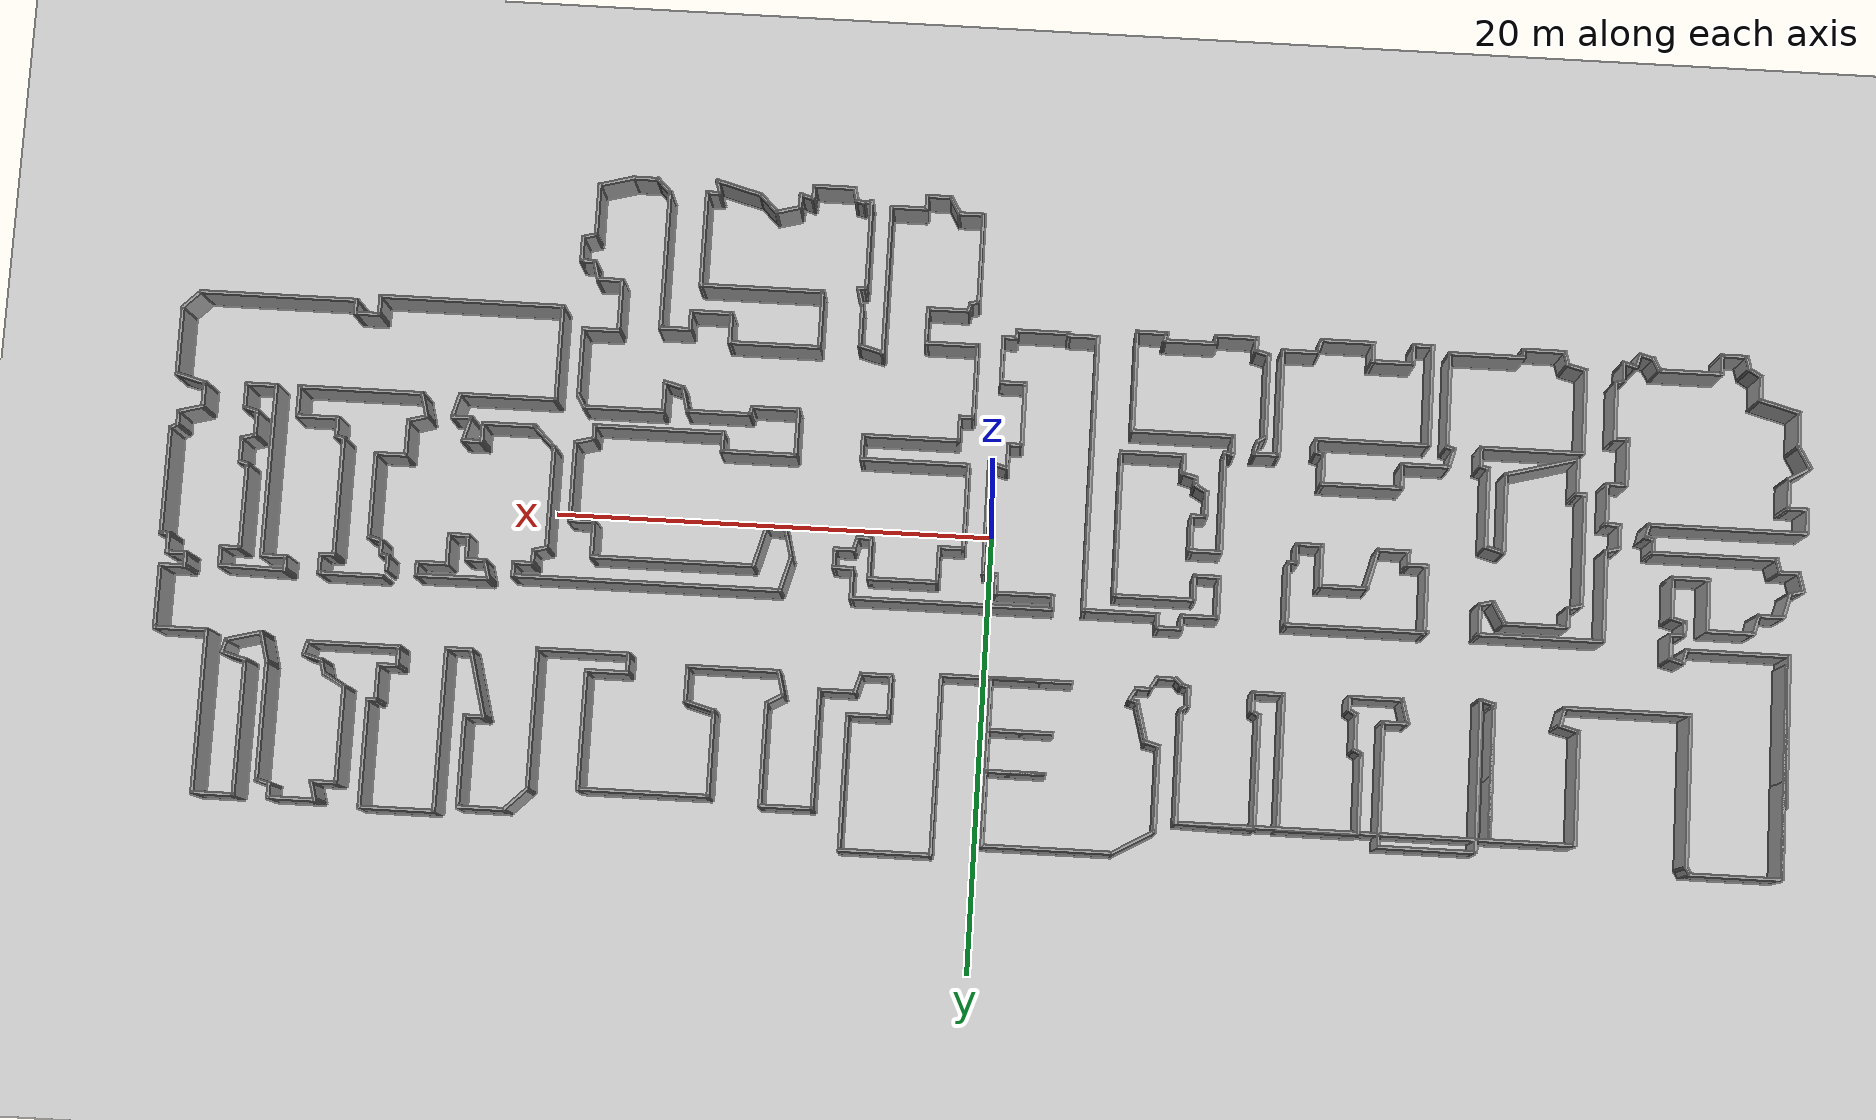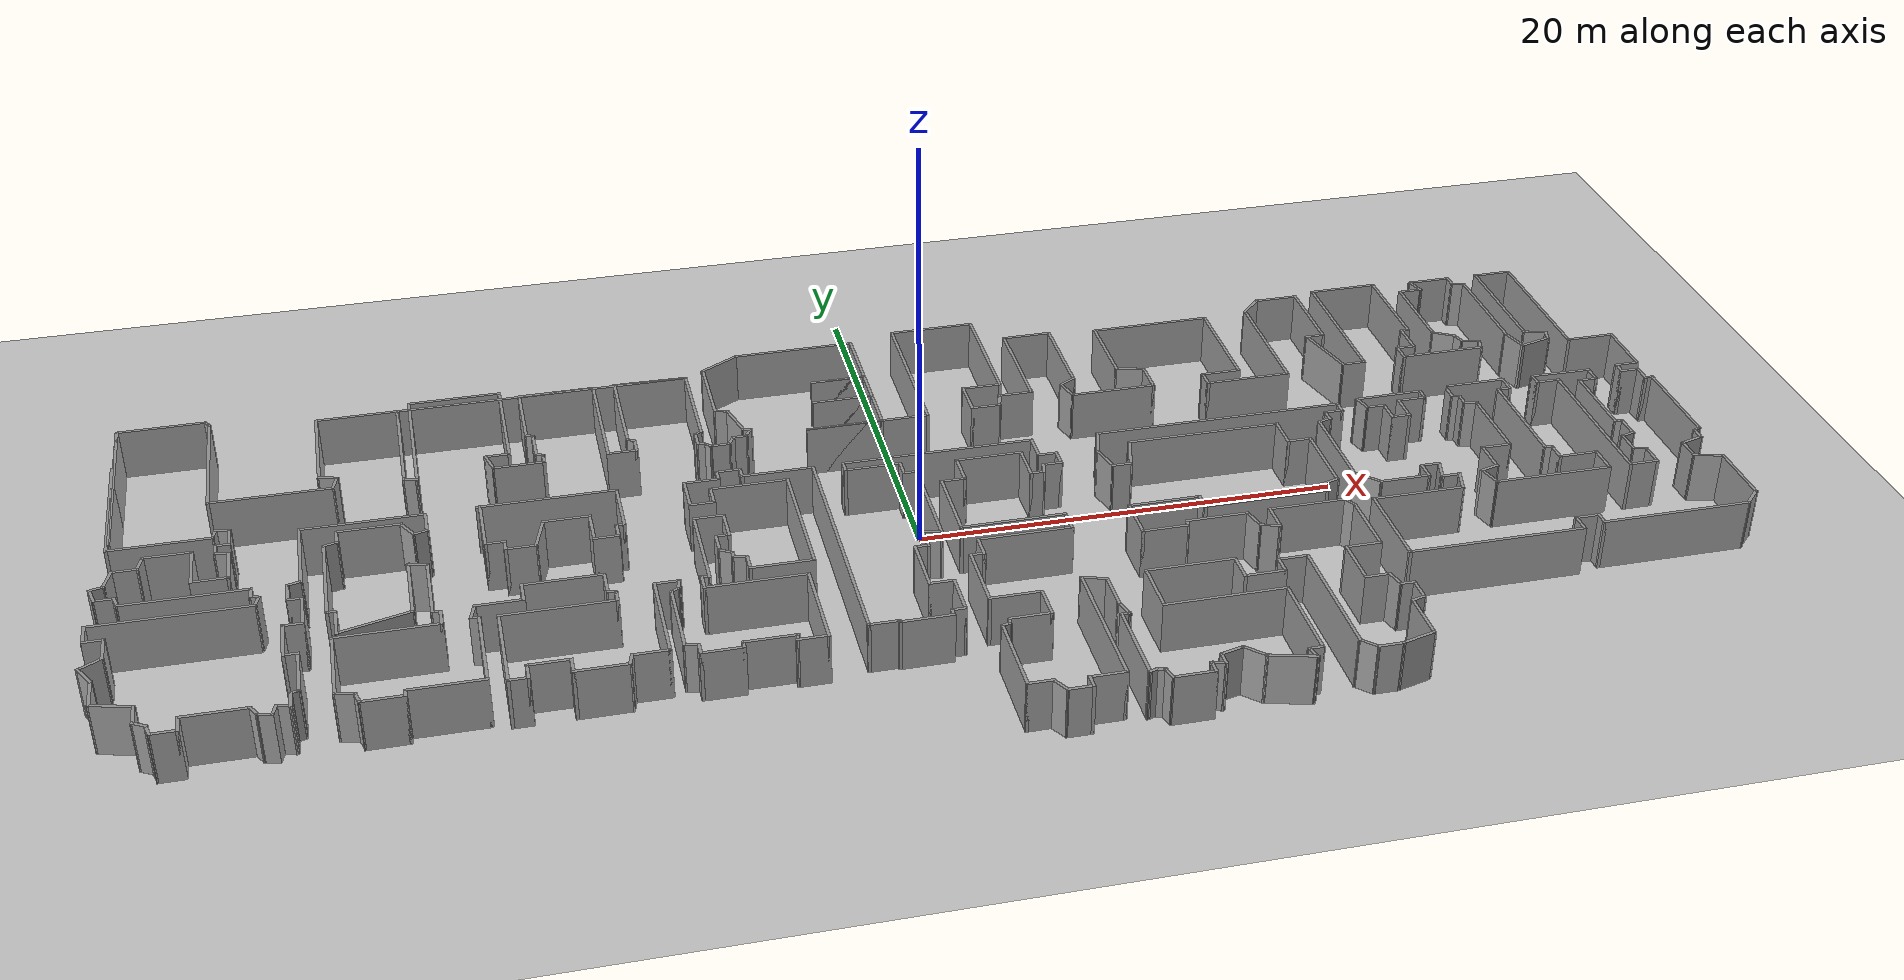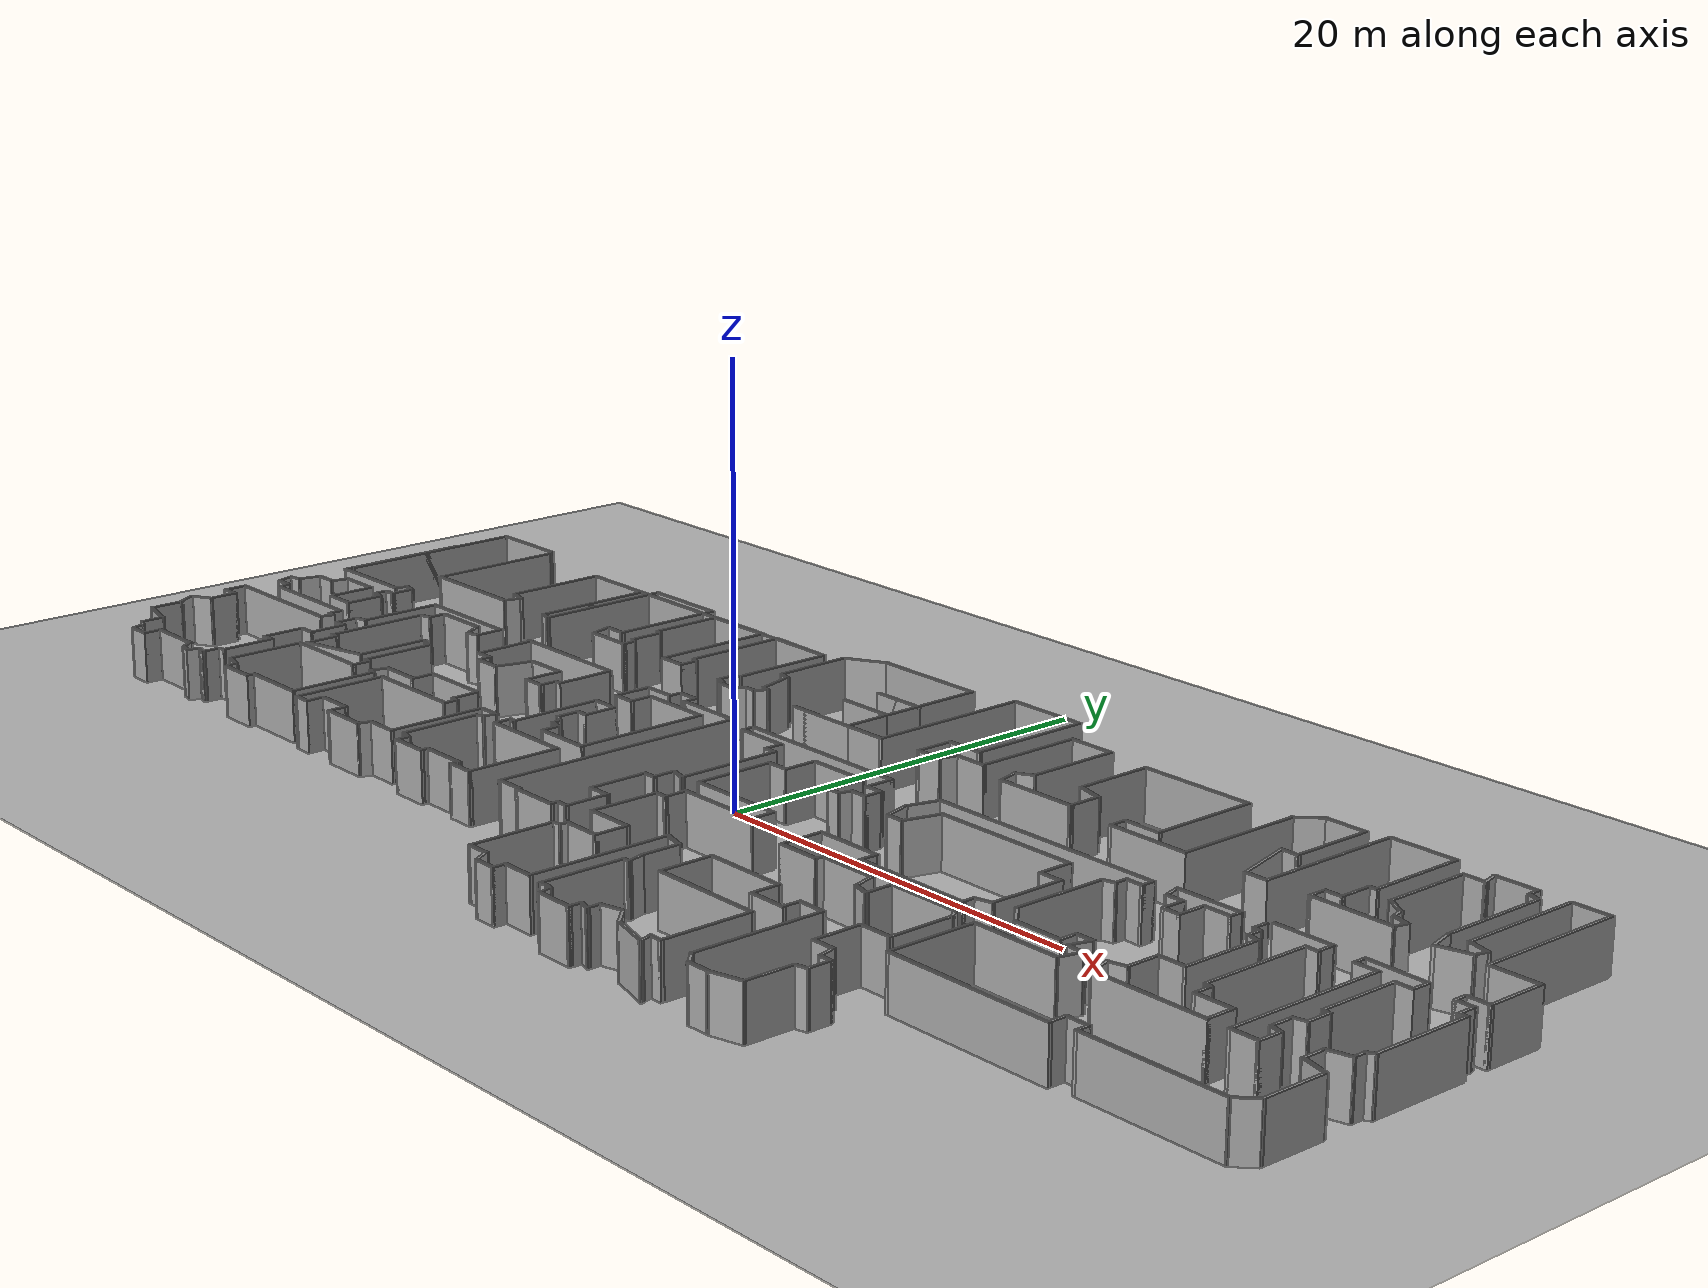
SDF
<sdf version="1.7">
 <world name="default">
  <light name="sun" type="directional">
   <pose>0 0 10 0 -0 0</pose>
   <diffuse>0.8 0.8 0.8 1</diffuse>
   <specular>0.2 0.2 0.2 1</specular>
   <attenuation>
    <range>1000</range>
    <constant>0.9</constant>
    <linear>0.01</linear>
    <quadratic>0.001</quadratic>
   </attenuation>
   <direction>-0.5 0.1 -0.9</direction>
   <spot><inner_angle>0</inner_angle><outer_angle>0</outer_angle><falloff>0</falloff></spot>
  </light>
  <model name="ground_plane">
   <static>1</static>
   <link name="link">
    <collision name="collision">
     <geometry><plane><normal>0 0 1</normal><size>100 100</size></plane></geometry>
     <surface>
      <contact><collide_bitmask>65535</collide_bitmask></contact>
      <friction><ode><mu>100</mu><mu2>50</mu2></ode></friction>
     </surface>
    </collision>
    <visual name="visual">
     <cast_shadows>0</cast_shadows>
     <geometry><plane><normal>0 0 1</normal><size>100 100</size></plane></geometry>
     <material>
      <script><uri>file://media/materials/scripts/gazebo.material</uri><name>Gazebo/Grey</name></script>
     </material>
    </visual>
   </link>
  </model>
  <gravity>0 0 -9.8</gravity>
  <magnetic_field>6e-06 2.3e-05 -4.2e-05</magnetic_field>
  <atmosphere type="adiabatic"/>
  <physics type="ode">
   <max_step_size>0.001</max_step_size>
   <real_time_factor>1</real_time_factor>
   <real_time_update_rate>1000</real_time_update_rate>
  </physics>
  <scene><ambient>0.4 0.4 0.4 1</ambient><background>0.7 0.7 0.7 1</background><shadows>1</shadows></scene>
  <spherical_coordinates>
   <surface_model>EARTH_WGS84</surface_model>
   <latitude_deg>0</latitude_deg>
   <longitude_deg>0</longitude_deg>
   <elevation>0</elevation>
   <heading_deg>0</heading_deg>
  </spherical_coordinates>
  <model name="Hospital">
   <pose>0.328682 -0.388502 0 0 -0 0</pose>
   <link name="Wall_10">
    <collision name="Wall_10_Collision">
     <geometry><box><size>9.75 0.15 2.5</size></box></geometry>
     <pose>0 0 1.25 0 -0 0</pose>
    </collision>
    <visual name="Wall_10_Visual">
     <pose>0 0 1.25 0 -0 0</pose>
     <geometry><box><size>9.75 0.15 2.5</size></box></geometry>
     <material>
      <script><uri>file://media/materials/scripts/gazebo.material</uri><name>Gazebo/Grey</name></script>
      <ambient>1 1 1 1</ambient>
     </material>
     <meta><layer>0</layer></meta>
    </visual>
    <pose>-36.3837 9.34312 0 0 -0 1.5708</pose>
   </link>
   <link name="Wall_100">
    <collision name="Wall_100_Collision">
     <geometry><box><size>7.5 0.15 2.5</size></box></geometry>
     <pose>0 0 1.25 0 -0 0</pose>
    </collision>
    <visual name="Wall_100_Visual">
     <pose>0 0 1.25 0 -0 0</pose>
     <geometry><box><size>7.5 0.15 2.5</size></box></geometry>
     <material>
      <script><uri>file://media/materials/scripts/gazebo.material</uri><name>Gazebo/Grey</name></script>
      <ambient>1 1 1 1</ambient>
     </material>
     <meta><layer>0</layer></meta>
    </visual>
    <pose>34.79 10.5774 0 0 -0 -1.5708</pose>
   </link>
   <link name="Wall_101">
    <collision name="Wall_101_Collision">
     <geometry><box><size>2.5 0.15 2.5</size></box></geometry>
     <pose>0 0 1.25 0 -0 0</pose>
    </collision>
    <visual name="Wall_101_Visual">
     <pose>0 0 1.25 0 -0 0</pose>
     <geometry><box><size>2.5 0.15 2.5</size></box></geometry>
     <material>
      <script><uri>file://media/materials/scripts/gazebo.material</uri><name>Gazebo/Grey</name></script>
      <ambient>1 1 1 1</ambient>
     </material>
     <meta><layer>0</layer></meta>
    </visual>
    <pose>35.965 6.90241 0 0 -0 0</pose>
   </link>
   <link name="Wall_102">
    <collision name="Wall_102_Collision">
     <geometry><box><size>3 0.15 2.5</size></box></geometry>
     <pose>0 0 1.25 0 -0 0</pose>
    </collision>
    <visual name="Wall_102_Visual">
     <pose>0 0 1.25 0 -0 0</pose>
     <geometry><box><size>3 0.15 2.5</size></box></geometry>
     <material>
      <script><uri>file://media/materials/scripts/gazebo.material</uri><name>Gazebo/Grey</name></script>
      <ambient>1 1 1 1</ambient>
     </material>
     <meta><layer>0</layer></meta>
    </visual>
    <pose>37.14 5.47741 0 0 -0 -1.5708</pose>
   </link>
   <link name="Wall_103">
    <collision name="Wall_103_Collision">
     <geometry><box><size>1.25 0.15 2.5</size></box></geometry>
     <pose>0 0 1.25 0 -0 0</pose>
    </collision>
    <visual name="Wall_103_Visual">
     <pose>0 0 1.25 0 -0 0</pose>
     <geometry><box><size>1.25 0.15 2.5</size></box></geometry>
     <material>
      <script><uri>file://media/materials/scripts/gazebo.material</uri><name>Gazebo/Grey</name></script>
      <ambient>1 1 1 1</ambient>
     </material>
     <meta><layer>0</layer></meta>
    </visual>
    <pose>36.59 4.05241 0 0 -0 3.14159</pose>
   </link>
   <link name="Wall_104">
    <collision name="Wall_104_Collision">
     <geometry><box><size>0.75 0.15 2.5</size></box></geometry>
     <pose>0 0 1.25 0 -0 0</pose>
    </collision>
    <visual name="Wall_104_Visual">
     <pose>0 0 1.25 0 -0 0</pose>
     <geometry><box><size>0.75 0.15 2.5</size></box></geometry>
     <material>
      <script><uri>file://media/materials/scripts/gazebo.material</uri><name>Gazebo/Grey</name></script>
      <ambient>1 1 1 1</ambient>
     </material>
     <meta><layer>0</layer></meta>
    </visual>
    <pose>36.04 3.75241 0 0 -0 -1.5708</pose>
   </link>
   <link name="Wall_105">
    <collision name="Wall_105_Collision">
     <geometry><box><size>1 0.15 2.5</size></box></geometry>
     <pose>0 0 1.25 0 -0 0</pose>
    </collision>
    <visual name="Wall_105_Visual">
     <pose>0 0 1.25 0 -0 0</pose>
     <geometry><box><size>1 0.15 2.5</size></box></geometry>
     <material>
      <script><uri>file://media/materials/scripts/gazebo.material</uri><name>Gazebo/Grey</name></script>
      <ambient>1 1 1 1</ambient>
     </material>
     <meta><layer>0</layer></meta>
    </visual>
    <pose>36.465 3.45241 0 0 -0 0</pose>
   </link>
   <link name="Wall_106">
    <collision name="Wall_106_Collision">
     <geometry><box><size>1 0.15 2.5</size></box></geometry>
     <pose>0 0 1.25 0 -0 0</pose>
    </collision>
    <visual name="Wall_106_Visual">
     <pose>0 0 1.25 0 -0 0</pose>
     <geometry><box><size>1 0.15 2.5</size></box></geometry>
     <material>
      <script><uri>file://media/materials/scripts/gazebo.material</uri><name>Gazebo/Grey</name></script>
      <ambient>1 1 1 1</ambient>
     </material>
     <meta><layer>0</layer></meta>
    </visual>
    <pose>36.89 3.02741 0 0 -0 -1.5708</pose>
   </link>
   <link name="Wall_107">
    <collision name="Wall_107_Collision">
     <geometry><box><size>0.5 0.15 2.5</size></box></geometry>
     <pose>0 0 1.25 0 -0 0</pose>
    </collision>
    <visual name="Wall_107_Visual">
     <pose>0 0 1.25 0 -0 0</pose>
     <geometry><box><size>0.5 0.15 2.5</size></box></geometry>
     <material>
      <script><uri>file://media/materials/scripts/gazebo.material</uri><name>Gazebo/Grey</name></script>
      <ambient>1 1 1 1</ambient>
     </material>
     <meta><layer>0</layer></meta>
    </visual>
    <pose>37.065 2.60241 0 0 -0 0</pose>
   </link>
   <link name="Wall_108">
    <collision name="Wall_108_Collision">
     <geometry><box><size>5 0.15 2.5</size></box></geometry>
     <pose>0 0 1.25 0 -0 0</pose>
    </collision>
    <visual name="Wall_108_Visual">
     <pose>0 0 1.25 0 -0 0</pose>
     <geometry><box><size>5 0.15 2.5</size></box></geometry>
     <material>
      <script><uri>file://media/materials/scripts/gazebo.material</uri><name>Gazebo/Grey</name></script>
      <ambient>1 1 1 1</ambient>
     </material>
     <meta><layer>0</layer></meta>
    </visual>
    <pose>37.24 0.177411 0 0 -0 -1.5708</pose>
   </link>
   <link name="Wall_109">
    <collision name="Wall_109_Collision">
     <geometry><box><size>0.5 0.15 2.5</size></box></geometry>
     <pose>0 0 1.25 0 -0 0</pose>
    </collision>
    <visual name="Wall_109_Visual">
     <pose>0 0 1.25 0 -0 0</pose>
     <geometry><box><size>0.5 0.15 2.5</size></box></geometry>
     <material>
      <script><uri>file://media/materials/scripts/gazebo.material</uri><name>Gazebo/Grey</name></script>
      <ambient>1 1 1 1</ambient>
     </material>
     <meta><layer>0</layer></meta>
    </visual>
    <pose>37.0885 -2.33509 0 0 -0 -2.61799</pose>
   </link>
   <link name="Wall_11">
    <collision name="Wall_11_Collision">
     <geometry><box><size>9.75 0.15 2.5</size></box></geometry>
     <pose>0 0 1.25 0 -0 0</pose>
    </collision>
    <visual name="Wall_11_Visual">
     <pose>0 0 1.25 0 -0 0</pose>
     <geometry><box><size>9.75 0.15 2.5</size></box></geometry>
     <material>
      <script><uri>file://media/materials/scripts/gazebo.material</uri><name>Gazebo/Grey</name></script>
      <ambient>1 1 1 1</ambient>
     </material>
     <meta><layer>0</layer></meta>
    </visual>
    <pose>-36.3837 9.34312 0 0 -0 -1.5708</pose>
   </link>
   <link name="Wall_110">
    <collision name="Wall_110_Collision">
     <geometry><box><size>0.75 0.15 2.5</size></box></geometry>
     <pose>0 0 1.25 0 -0 0</pose>
    </collision>
    <visual name="Wall_110_Visual">
     <pose>0 0 1.25 0 -0 0</pose>
     <geometry><box><size>0.75 0.15 2.5</size></box></geometry>
     <material>
      <script><uri>file://media/materials/scripts/gazebo.material</uri><name>Gazebo/Grey</name></script>
      <ambient>1 1 1 1</ambient>
     </material>
     <meta><layer>0</layer></meta>
    </visual>
    <pose>36.9369 -2.72259 0 0 -0 -1.5708</pose>
   </link>
   <link name="Wall_111">
    <collision name="Wall_111_Collision">
     <geometry><box><size>1.25 0.15 2.5</size></box></geometry>
     <pose>0 0 1.25 0 -0 0</pose>
    </collision>
    <visual name="Wall_111_Visual">
     <pose>0 0 1.25 0 -0 0</pose>
     <geometry><box><size>1.25 0.15 2.5</size></box></geometry>
     <material>
      <script><uri>file://media/materials/scripts/gazebo.material</uri><name>Gazebo/Grey</name></script>
      <ambient>1 1 1 1</ambient>
     </material>
     <meta><layer>0</layer></meta>
    </visual>
    <pose>36.4056 -3.16494 0 0 -0 -2.87979</pose>
   </link>
   <link name="Wall_112">
    <collision name="Wall_112_Collision">
     <geometry><box><size>1.25 0.15 2.5</size></box></geometry>
     <pose>0 0 1.25 0 -0 0</pose>
    </collision>
    <visual name="Wall_112_Visual">
     <pose>0 0 1.25 0 -0 0</pose>
     <geometry><box><size>1.25 0.15 2.5</size></box></geometry>
     <material>
      <script><uri>file://media/materials/scripts/gazebo.material</uri><name>Gazebo/Grey</name></script>
      <ambient>1 1 1 1</ambient>
     </material>
     <meta><layer>0</layer></meta>
    </visual>
    <pose>35.8744 -3.85729 0 0 -0 -1.5708</pose>
   </link>
   <link name="Wall_113">
    <collision name="Wall_113_Collision">
     <geometry><box><size>1.5 0.15 2.5</size></box></geometry>
     <pose>0 0 1.25 0 -0 0</pose>
    </collision>
    <visual name="Wall_113_Visual">
     <pose>0 0 1.25 0 -0 0</pose>
     <geometry><box><size>1.5 0.15 2.5</size></box></geometry>
     <material>
      <script><uri>file://media/materials/scripts/gazebo.material</uri><name>Gazebo/Grey</name></script>
      <ambient>1 1 1 1</ambient>
     </material>
     <meta><layer>0</layer></meta>
    </visual>
    <pose>36.5264 -4.58199 0 0 -0 -0.261799</pose>
   </link>
   <link name="Wall_114">
    <collision name="Wall_114_Collision">
     <geometry><box><size>3.25 0.15 2.5</size></box></geometry>
     <pose>0 0 1.25 0 -0 0</pose>
    </collision>
    <visual name="Wall_114_Visual">
     <pose>0 0 1.25 0 -0 0</pose>
     <geometry><box><size>3.25 0.15 2.5</size></box></geometry>
     <material>
      <script><uri>file://media/materials/scripts/gazebo.material</uri><name>Gazebo/Grey</name></script>
      <ambient>1 1 1 1</ambient>
     </material>
     <meta><layer>0</layer></meta>
    </visual>
    <pose>37.1784 -6.3067 0 0 -0 -1.5708</pose>
   </link>
   <link name="Wall_115">
    <collision name="Wall_115_Collision">
     <geometry><box><size>1.25 0.15 2.5</size></box></geometry>
     <pose>0 0 1.25 0 -0 0</pose>
    </collision>
    <visual name="Wall_115_Visual">
     <pose>0 0 1.25 0 -0 0</pose>
     <geometry><box><size>1.25 0.15 2.5</size></box></geometry>
     <material>
      <script><uri>file://media/materials/scripts/gazebo.material</uri><name>Gazebo/Grey</name></script>
      <ambient>1 1 1 1</ambient>
     </material>
     <meta><layer>0</layer></meta>
    </visual>
    <pose>36.7895 -8.2456 0 0 -0 -2.35619</pose>
   </link>
   <link name="Wall_116">
    <collision name="Wall_116_Collision">
     <geometry><box><size>7.25 0.15 2.5</size></box></geometry>
     <pose>0 0 1.25 0 -0 0</pose>
    </collision>
    <visual name="Wall_116_Visual">
     <pose>0 0 1.25 0 -0 0</pose>
     <geometry><box><size>7.25 0.15 2.5</size></box></geometry>
     <material>
      <script><uri>file://media/materials/scripts/gazebo.material</uri><name>Gazebo/Grey</name></script>
      <ambient>1 1 1 1</ambient>
     </material>
     <meta><layer>0</layer></meta>
    </visual>
    <pose>32.8506 -8.63451 0 0 -0 3.14159</pose>
   </link>
   <link name="Wall_117">
    <collision name="Wall_117_Collision">
     <geometry><box><size>0.75 0.15 2.5</size></box></geometry>
     <pose>0 0 1.25 0 -0 0</pose>
    </collision>
    <visual name="Wall_117_Visual">
     <pose>0 0 1.25 0 -0 0</pose>
     <geometry><box><size>0.75 0.15 2.5</size></box></geometry>
     <material>
      <script><uri>file://media/materials/scripts/gazebo.material</uri><name>Gazebo/Grey</name></script>
      <ambient>1 1 1 1</ambient>
     </material>
     <meta><layer>0</layer></meta>
    </visual>
    <pose>29.3006 -8.33451 0 0 -0 1.5708</pose>
   </link>
   <link name="Wall_118">
    <collision name="Wall_118_Collision">
     <geometry><box><size>1.25 0.15 2.5</size></box></geometry>
     <pose>0 0 1.25 0 -0 0</pose>
    </collision>
    <visual name="Wall_118_Visual">
     <pose>0 0 1.25 0 -0 0</pose>
     <geometry><box><size>1.25 0.15 2.5</size></box></geometry>
     <material>
      <script><uri>file://media/materials/scripts/gazebo.material</uri><name>Gazebo/Grey</name></script>
      <ambient>1 1 1 1</ambient>
     </material>
     <meta><layer>0</layer></meta>
    </visual>
    <pose>28.7506 -8.03451 0 0 -0 3.14159</pose>
   </link>
   <link name="Wall_119">
    <collision name="Wall_119_Collision">
     <geometry><box><size>1 0.15 2.5</size></box></geometry>
     <pose>0 0 1.25 0 -0 0</pose>
    </collision>
    <visual name="Wall_119_Visual">
     <pose>0 0 1.25 0 -0 0</pose>
     <geometry><box><size>1 0.15 2.5</size></box></geometry>
     <material>
      <script><uri>file://media/materials/scripts/gazebo.material</uri><name>Gazebo/Grey</name></script>
      <ambient>1 1 1 1</ambient>
     </material>
     <meta><layer>0</layer></meta>
    </visual>
    <pose>28.2006 -8.45951 0 0 -0 -1.5708</pose>
   </link>
   <link name="Wall_120">
    <collision name="Wall_120_Collision">
     <geometry><box><size>8.5 0.15 2.5</size></box></geometry>
     <pose>0 0 1.25 0 -0 0</pose>
    </collision>
    <visual name="Wall_120_Visual">
     <pose>0 0 1.25 0 -0 0</pose>
     <geometry><box><size>8.5 0.15 2.5</size></box></geometry>
     <material>
      <script><uri>file://media/materials/scripts/gazebo.material</uri><name>Gazebo/Grey</name></script>
      <ambient>1 1 1 1</ambient>
     </material>
     <meta><layer>0</layer></meta>
    </visual>
    <pose>24.0256 -8.88451 0 0 -0 3.14159</pose>
   </link>
   <link name="Wall_121">
    <collision name="Wall_121_Collision">
     <geometry><box><size>4.5 0.15 2.5</size></box></geometry>
     <pose>0 0 1.25 0 -0 0</pose>
    </collision>
    <visual name="Wall_121_Visual">
     <pose>0 0 1.25 0 -0 0</pose>
     <geometry><box><size>4.5 0.15 2.5</size></box></geometry>
     <material>
      <script><uri>file://media/materials/scripts/gazebo.material</uri><name>Gazebo/Grey</name></script>
      <ambient>1 1 1 1</ambient>
     </material>
     <meta><layer>0</layer></meta>
    </visual>
    <pose>19.8506 -6.70951 0 0 -0 1.5708</pose>
   </link>
   <link name="Wall_122">
    <collision name="Wall_122_Collision">
     <geometry><box><size>4.5 0.15 2.5</size></box></geometry>
     <pose>0 0 1.25 0 -0 0</pose>
    </collision>
    <visual name="Wall_122_Visual">
     <pose>0 0 1.25 0 -0 0</pose>
     <geometry><box><size>4.5 0.15 2.5</size></box></geometry>
     <material>
      <script><uri>file://media/materials/scripts/gazebo.material</uri><name>Gazebo/Grey</name></script>
      <ambient>1 1 1 1</ambient>
     </material>
     <meta><layer>0</layer></meta>
    </visual>
    <pose>22.0256 -4.53451 0 0 -0 0</pose>
   </link>
   <link name="Wall_123">
    <collision name="Wall_123_Collision">
     <geometry><box><size>1.25 0.15 2.5</size></box></geometry>
     <pose>0 0 1.25 0 -0 0</pose>
    </collision>
    <visual name="Wall_123_Visual">
     <pose>0 0 1.25 0 -0 0</pose>
     <geometry><box><size>1.25 0.15 2.5</size></box></geometry>
     <material>
      <script><uri>file://media/materials/scripts/gazebo.material</uri><name>Gazebo/Grey</name></script>
      <ambient>1 1 1 1</ambient>
     </material>
     <meta><layer>0</layer></meta>
    </visual>
    <pose>24.3429 -4.00325 0 0 -0 1.309</pose>
   </link>
   <link name="Wall_124">
    <collision name="Wall_124_Collision">
     <geometry><box><size>1 0.15 2.5</size></box></geometry>
     <pose>0 0 1.25 0 -0 0</pose>
    </collision>
    <visual name="Wall_124_Visual">
     <pose>0 0 1.25 0 -0 0</pose>
     <geometry><box><size>1 0.15 2.5</size></box></geometry>
     <material>
      <script><uri>file://media/materials/scripts/gazebo.material</uri><name>Gazebo/Grey</name></script>
      <ambient>1 1 1 1</ambient>
     </material>
     <meta><layer>0</layer></meta>
    </visual>
    <pose>24.0603 -3.472 0 0 -0 3.14159</pose>
   </link>
   <link name="Wall_125">
    <collision name="Wall_125_Collision">
     <geometry><box><size>1.25 0.15 2.5</size></box></geometry>
     <pose>0 0 1.25 0 -0 0</pose>
    </collision>
    <visual name="Wall_125_Visual">
     <pose>0 0 1.25 0 -0 0</pose>
     <geometry><box><size>1.25 0.15 2.5</size></box></geometry>
     <material>
      <script><uri>file://media/materials/scripts/gazebo.material</uri><name>Gazebo/Grey</name></script>
      <ambient>1 1 1 1</ambient>
     </material>
     <meta><layer>0</layer></meta>
    </visual>
    <pose>23.7776 -2.94074 0 0 -0 1.309</pose>
   </link>
   <link name="Wall_126">
    <collision name="Wall_126_Collision">
     <geometry><box><size>1 0.15 2.5</size></box></geometry>
     <pose>0 0 1.25 0 -0 0</pose>
    </collision>
    <visual name="Wall_126_Visual">
     <pose>0 0 1.25 0 -0 0</pose>
     <geometry><box><size>1 0.15 2.5</size></box></geometry>
     <material>
      <script><uri>file://media/materials/scripts/gazebo.material</uri><name>Gazebo/Grey</name></script>
      <ambient>1 1 1 1</ambient>
     </material>
     <meta><layer>0</layer></meta>
    </visual>
    <pose>23.495 -2.40948 0 0 -0 3.14159</pose>
   </link>
   <link name="Wall_127">
    <collision name="Wall_127_Collision">
     <geometry><box><size>1 0.15 2.5</size></box></geometry>
     <pose>0 0 1.25 0 -0 0</pose>
    </collision>
    <visual name="Wall_127_Visual">
     <pose>0 0 1.25 0 -0 0</pose>
     <geometry><box><size>1 0.15 2.5</size></box></geometry>
     <material>
      <script><uri>file://media/materials/scripts/gazebo.material</uri><name>Gazebo/Grey</name></script>
      <ambient>1 1 1 1</ambient>
     </material>
     <meta><layer>0</layer></meta>
    </visual>
    <pose>23.07 -2.83448 0 0 -0 -1.5708</pose>
   </link>
   <link name="Wall_128">
    <collision name="Wall_128_Collision">
     <geometry><box><size>2.5 0.15 2.5</size></box></geometry>
     <pose>0 0 1.25 0 -0 0</pose>
    </collision>
    <visual name="Wall_128_Visual">
     <pose>0 0 1.25 0 -0 0</pose>
     <geometry><box><size>2.5 0.15 2.5</size></box></geometry>
     <material>
      <script><uri>file://media/materials/scripts/gazebo.material</uri><name>Gazebo/Grey</name></script>
      <ambient>1 1 1 1</ambient>
     </material>
     <meta><layer>0</layer></meta>
    </visual>
    <pose>21.895 -3.25948 0 0 -0 3.14159</pose>
   </link>
   <link name="Wall_129">
    <collision name="Wall_129_Collision">
     <geometry><box><size>1.5 0.15 2.5</size></box></geometry>
     <pose>0 0 1.25 0 -0 0</pose>
    </collision>
    <visual name="Wall_129_Visual">
     <pose>0 0 1.25 0 -0 0</pose>
     <geometry><box><size>1.5 0.15 2.5</size></box></geometry>
     <material>
      <script><uri>file://media/materials/scripts/gazebo.material</uri><name>Gazebo/Grey</name></script>
      <ambient>1 1 1 1</ambient>
     </material>
     <meta><layer>0</layer></meta>
    </visual>
    <pose>20.2427 -2.78218 0 0 -0 2.35619</pose>
   </link>
   <link name="Wall_13">
    <collision name="Wall_13_Collision">
     <geometry><box><size>4.25 0.15 2.5</size></box></geometry>
     <pose>0 0 1.25 0 -0 0</pose>
    </collision>
    <visual name="Wall_13_Visual">
     <pose>0 0 1.25 0 -0 0</pose>
     <geometry><box><size>4.25 0.15 2.5</size></box></geometry>
     <material>
      <script><uri>file://media/materials/scripts/gazebo.material</uri><name>Gazebo/Grey</name></script>
      <ambient>1 1 1 1</ambient>
     </material>
     <meta><layer>0</layer></meta>
    </visual>
    <pose>-34.3337 14.1431 0 0 -0 0</pose>
   </link>
   <link name="Wall_130">
    <collision name="Wall_130_Collision">
     <geometry><box><size>4.75 0.15 2.5</size></box></geometry>
     <pose>0 0 1.25 0 -0 0</pose>
    </collision>
    <visual name="Wall_130_Visual">
     <pose>0 0 1.25 0 -0 0</pose>
     <geometry><box><size>4.75 0.15 2.5</size></box></geometry>
     <material>
      <script><uri>file://media/materials/scripts/gazebo.material</uri><name>Gazebo/Grey</name></script>
      <ambient>1 1 1 1</ambient>
     </material>
     <meta><layer>0</layer></meta>
    </visual>
    <pose>19.7654 -0.004882 0 0 -0 1.5708</pose>
   </link>
   <link name="Wall_131">
    <collision name="Wall_131_Collision">
     <geometry><box><size>0.75 0.15 2.5</size></box></geometry>
     <pose>0 0 1.25 0 -0 0</pose>
    </collision>
    <visual name="Wall_131_Visual">
     <pose>0 0 1.25 0 -0 0</pose>
     <geometry><box><size>0.75 0.15 2.5</size></box></geometry>
     <material>
      <script><uri>file://media/materials/scripts/gazebo.material</uri><name>Gazebo/Grey</name></script>
      <ambient>1 1 1 1</ambient>
     </material>
     <meta><layer>0</layer></meta>
    </visual>
    <pose>20.0552 2.37276 0 0 -0 0.261799</pose>
   </link>
   <link name="Wall_132">
    <collision name="Wall_132_Collision">
     <geometry><box><size>0.75 0.15 2.5</size></box></geometry>
     <pose>0 0 1.25 0 -0 0</pose>
    </collision>
    <visual name="Wall_132_Visual">
     <pose>0 0 1.25 0 -0 0</pose>
     <geometry><box><size>0.75 0.15 2.5</size></box></geometry>
     <material>
      <script><uri>file://media/materials/scripts/gazebo.material</uri><name>Gazebo/Grey</name></script>
      <ambient>1 1 1 1</ambient>
     </material>
     <meta><layer>0</layer></meta>
    </visual>
    <pose>20.3449 2.75041 0 0 -0 1.5708</pose>
   </link>
   <link name="Wall_133">
    <collision name="Wall_133_Collision">
     <geometry><box><size>1 0.15 2.5</size></box></geometry>
     <pose>0 0 1.25 0 -0 0</pose>
    </collision>
    <visual name="Wall_133_Visual">
     <pose>0 0 1.25 0 -0 0</pose>
     <geometry><box><size>1 0.15 2.5</size></box></geometry>
     <material>
      <script><uri>file://media/materials/scripts/gazebo.material</uri><name>Gazebo/Grey</name></script>
      <ambient>1 1 1 1</ambient>
     </material>
     <meta><layer>0</layer></meta>
    </visual>
    <pose>20.7699 3.05041 0 0 -0 0</pose>
   </link>
   <link name="Wall_134">
    <collision name="Wall_134_Collision">
     <geometry><box><size>0.75 0.15 2.5</size></box></geometry>
     <pose>0 0 1.25 0 -0 0</pose>
    </collision>
    <visual name="Wall_134_Visual">
     <pose>0 0 1.25 0 -0 0</pose>
     <geometry><box><size>0.75 0.15 2.5</size></box></geometry>
     <material>
      <script><uri>file://media/materials/scripts/gazebo.material</uri><name>Gazebo/Grey</name></script>
      <ambient>1 1 1 1</ambient>
     </material>
     <meta><layer>0</layer></meta>
    </visual>
    <pose>21.1949 3.35041 0 0 -0 1.5708</pose>
   </link>
   <link name="Wall_135">
    <collision name="Wall_135_Collision">
     <geometry><box><size>12.25 0.15 2.5</size></box></geometry>
     <pose>0 0 1.25 0 -0 0</pose>
    </collision>
    <visual name="Wall_135_Visual">
     <pose>0 0 1.25 0 -0 0</pose>
     <geometry><box><size>12.25 0.15 2.5</size></box></geometry>
     <material>
      <script><uri>file://media/materials/scripts/gazebo.material</uri><name>Gazebo/Grey</name></script>
      <ambient>1 1 1 1</ambient>
     </material>
     <meta><layer>0</layer></meta>
    </visual>
    <pose>15.1449 3.65041 0 0 -0 3.14159</pose>
   </link>
   <link name="Wall_136">
    <collision name="Wall_136_Collision">
     <geometry><box><size>1.75 0.15 2.5</size></box></geometry>
     <pose>0 0 1.25 0 -0 0</pose>
    </collision>
    <visual name="Wall_136_Visual">
     <pose>0 0 1.25 0 -0 0</pose>
     <geometry><box><size>1.75 0.15 2.5</size></box></geometry>
     <material>
      <script><uri>file://media/materials/scripts/gazebo.material</uri><name>Gazebo/Grey</name></script>
      <ambient>1 1 1 1</ambient>
     </material>
     <meta><layer>0</layer></meta>
    </visual>
    <pose>8.88788 2.87767 0 0 -0 -1.8326</pose>
   </link>
   <link name="Wall_137">
    <collision name="Wall_137_Collision">
     <geometry><box><size>1.5 0.15 2.5</size></box></geometry>
     <pose>0 0 1.25 0 -0 0</pose>
    </collision>
    <visual name="Wall_137_Visual">
     <pose>0 0 1.25 0 -0 0</pose>
     <geometry><box><size>1.5 0.15 2.5</size></box></geometry>
     <material>
      <script><uri>file://media/materials/scripts/gazebo.material</uri><name>Gazebo/Grey</name></script>
      <ambient>1 1 1 1</ambient>
     </material>
     <meta><layer>0</layer></meta>
    </visual>
    <pose>8.85553 1.45293 0 0 -0 -1.309</pose>
   </link>
   <link name="Wall_138">
    <collision name="Wall_138_Collision">
     <geometry><box><size>1 0.15 2.5</size></box></geometry>
     <pose>0 0 1.25 0 -0 0</pose>
    </collision>
    <visual name="Wall_138_Visual">
     <pose>0 0 1.25 0 -0 0</pose>
     <geometry><box><size>1 0.15 2.5</size></box></geometry>
     <material>
      <script><uri>file://media/materials/scripts/gazebo.material</uri><name>Gazebo/Grey</name></script>
      <ambient>1 1 1 1</ambient>
     </material>
     <meta><layer>0</layer></meta>
    </visual>
    <pose>9.45523 0.800928 0 0 -0 0</pose>
   </link>
   <link name="Wall_139">
    <collision name="Wall_139_Collision">
     <geometry><box><size>2 0.15 2.5</size></box></geometry>
     <pose>0 0 1.25 0 -0 0</pose>
    </collision>
    <visual name="Wall_139_Visual">
     <pose>0 0 1.25 0 -0 0</pose>
     <geometry><box><size>2 0.15 2.5</size></box></geometry>
     <material>
      <script><uri>file://media/materials/scripts/gazebo.material</uri><name>Gazebo/Grey</name></script>
      <ambient>1 1 1 1</ambient>
     </material>
     <meta><layer>0</layer></meta>
    </visual>
    <pose>10.1196 1.69441 0 0 -0 1.309</pose>
   </link>
   <link name="Wall_14">
    <collision name="Wall_14_Collision">
     <geometry><box><size>0.5 0.15 2.5</size></box></geometry>
     <pose>0 0 1.25 0 -0 0</pose>
    </collision>
    <visual name="Wall_14_Visual">
     <pose>0 0 1.25 0 -0 0</pose>
     <geometry><box><size>0.5 0.15 2.5</size></box></geometry>
     <material>
      <script><uri>file://media/materials/scripts/gazebo.material</uri><name>Gazebo/Grey</name></script>
      <ambient>1 1 1 1</ambient>
     </material>
     <meta><layer>0</layer></meta>
    </visual>
    <pose>-32.1962 13.9916 0 0 -0 -1.0472</pose>
   </link>
   <link name="Wall_140">
    <collision name="Wall_140_Collision">
     <geometry><box><size>7.5 0.15 2.5</size></box></geometry>
     <pose>0 0 1.25 0 -0 0</pose>
    </collision>
    <visual name="Wall_140_Visual">
     <pose>0 0 1.25 0 -0 0</pose>
     <geometry><box><size>7.5 0.15 2.5</size></box></geometry>
     <material>
      <script><uri>file://media/materials/scripts/gazebo.material</uri><name>Gazebo/Grey</name></script>
      <ambient>1 1 1 1</ambient>
     </material>
     <meta><layer>0</layer></meta>
    </visual>
    <pose>14.034 2.58789 0 0 -0 0</pose>
   </link>
   <link name="Wall_141">
    <collision name="Wall_141_Collision">
     <geometry><box><size>1.75 0.15 2.5</size></box></geometry>
     <pose>0 0 1.25 0 -0 0</pose>
    </collision>
    <visual name="Wall_141_Visual">
     <pose>0 0 1.25 0 -0 0</pose>
     <geometry><box><size>1.75 0.15 2.5</size></box></geometry>
     <material>
      <script><uri>file://media/materials/scripts/gazebo.material</uri><name>Gazebo/Grey</name></script>
      <ambient>1 1 1 1</ambient>
     </material>
     <meta><layer>0</layer></meta>
    </visual>
    <pose>17.709 1.78789 0 0 -0 -1.5708</pose>
   </link>
   <link name="Wall_142">
    <collision name="Wall_142_Collision">
     <geometry><box><size>1.25 0.15 2.5</size></box></geometry>
     <pose>0 0 1.25 0 -0 0</pose>
    </collision>
    <visual name="Wall_142_Visual">
     <pose>0 0 1.25 0 -0 0</pose>
     <geometry><box><size>1.25 0.15 2.5</size></box></geometry>
     <material>
      <script><uri>file://media/materials/scripts/gazebo.material</uri><name>Gazebo/Grey</name></script>
      <ambient>1 1 1 1</ambient>
     </material>
     <meta><layer>0</layer></meta>
    </visual>
    <pose>18.259 0.987891 0 0 -0 0</pose>
   </link>
   <link name="Wall_143">
    <collision name="Wall_143_Collision">
     <geometry><box><size>3.75 0.15 2.5</size></box></geometry>
     <pose>0 0 1.25 0 -0 0</pose>
    </collision>
    <visual name="Wall_143_Visual">
     <pose>0 0 1.25 0 -0 0</pose>
     <geometry><box><size>3.75 0.15 2.5</size></box></geometry>
     <material>
      <script><uri>file://media/materials/scripts/gazebo.material</uri><name>Gazebo/Grey</name></script>
      <ambient>1 1 1 1</ambient>
     </material>
     <meta><layer>0</layer></meta>
    </visual>
    <pose>18.809 -0.812109 0 0 -0 -1.5708</pose>
   </link>
   <link name="Wall_144">
    <collision name="Wall_144_Collision">
     <geometry><box><size>1 0.15 2.5</size></box></geometry>
     <pose>0 0 1.25 0 -0 0</pose>
    </collision>
    <visual name="Wall_144_Visual">
     <pose>0 0 1.25 0 -0 0</pose>
     <geometry><box><size>1 0.15 2.5</size></box></geometry>
     <material>
      <script><uri>file://media/materials/scripts/gazebo.material</uri><name>Gazebo/Grey</name></script>
      <ambient>1 1 1 1</ambient>
     </material>
     <meta><layer>0</layer></meta>
    </visual>
    <pose>18.3985 -2.72211 0 0 -0 -2.87979</pose>
   </link>
   <link name="Wall_145">
    <collision name="Wall_145_Collision">
     <geometry><box><size>0.75 0.15 2.5</size></box></geometry>
     <pose>0 0 1.25 0 -0 0</pose>
    </collision>
    <visual name="Wall_145_Visual">
     <pose>0 0 1.25 0 -0 0</pose>
     <geometry><box><size>0.75 0.15 2.5</size></box></geometry>
     <material>
      <script><uri>file://media/materials/scripts/gazebo.material</uri><name>Gazebo/Grey</name></script>
      <ambient>1 1 1 1</ambient>
     </material>
     <meta><layer>0</layer></meta>
    </visual>
    <pose>17.988 -3.13211 0 0 -0 -1.5708</pose>
   </link>
   <link name="Wall_146">
    <collision name="Wall_146_Collision">
     <geometry><box><size>6 0.15 2.5</size></box></geometry>
     <pose>0 0 1.25 0 -0 0</pose>
    </collision>
    <visual name="Wall_146_Visual">
     <pose>0 0 1.25 0 -0 0</pose>
     <geometry><box><size>6 0.15 2.5</size></box></geometry>
     <material>
      <script><uri>file://media/materials/scripts/gazebo.material</uri><name>Gazebo/Grey</name></script>
      <ambient>1 1 1 1</ambient>
     </material>
     <meta><layer>0</layer></meta>
    </visual>
    <pose>15.063 -3.4321 0 0 -0 3.14159</pose>
   </link>
   <link name="Wall_147">
    <collision name="Wall_147_Collision">
     <geometry><box><size>1 0.15 2.5</size></box></geometry>
     <pose>0 0 1.25 0 -0 0</pose>
    </collision>
    <visual name="Wall_147_Visual">
     <pose>0 0 1.25 0 -0 0</pose>
     <geometry><box><size>1 0.15 2.5</size></box></geometry>
     <material>
      <script><uri>file://media/materials/scripts/gazebo.material</uri><name>Gazebo/Grey</name></script>
      <ambient>1 1 1 1</ambient>
     </material>
     <meta><layer>0</layer></meta>
    </visual>
    <pose>12.138 -3.00711 0 0 -0 1.5708</pose>
   </link>
   <link name="Wall_148">
    <collision name="Wall_148_Collision">
     <geometry><box><size>3.5 0.15 2.5</size></box></geometry>
     <pose>0 0 1.25 0 -0 0</pose>
    </collision>
    <visual name="Wall_148_Visual">
     <pose>0 0 1.25 0 -0 0</pose>
     <geometry><box><size>3.5 0.15 2.5</size></box></geometry>
     <material>
      <script><uri>file://media/materials/scripts/gazebo.material</uri><name>Gazebo/Grey</name></script>
      <ambient>1 1 1 1</ambient>
     </material>
     <meta><layer>0</layer></meta>
    </visual>
    <pose>10.463 -2.5821 0 0 -0 3.14159</pose>
   </link>
   <link name="Wall_149">
    <collision name="Wall_149_Collision">
     <geometry><box><size>2.25 0.15 2.5</size></box></geometry>
     <pose>0 0 1.25 0 -0 0</pose>
    </collision>
    <visual name="Wall_149_Visual">
     <pose>0 0 1.25 0 -0 0</pose>
     <geometry><box><size>2.25 0.15 2.5</size></box></geometry>
     <material>
      <script><uri>file://media/materials/scripts/gazebo.material</uri><name>Gazebo/Grey</name></script>
      <ambient>1 1 1 1</ambient>
     </material>
     <meta><layer>0</layer></meta>
    </visual>
    <pose>8.78801 -3.63211 0 0 -0 -1.5708</pose>
   </link>
   <link name="Wall_15">
    <collision name="Wall_15_Collision">
     <geometry><box><size>7 0.15 2.5</size></box></geometry>
     <pose>0 0 1.25 0 -0 0</pose>
    </collision>
    <visual name="Wall_15_Visual">
     <pose>0 0 1.25 0 -0 0</pose>
     <geometry><box><size>7 0.15 2.5</size></box></geometry>
     <material>
      <script><uri>file://media/materials/scripts/gazebo.material</uri><name>Gazebo/Grey</name></script>
      <ambient>1 1 1 1</ambient>
     </material>
     <meta><layer>0</layer></meta>
    </visual>
    <pose>-32.1087 10.415 0 0 -0 -1.5708</pose>
   </link>
   <link name="Wall_150">
    <collision name="Wall_150_Collision">
     <geometry><box><size>2.25 0.15 2.5</size></box></geometry>
     <pose>0 0 1.25 0 -0 0</pose>
    </collision>
    <visual name="Wall_150_Visual">
     <pose>0 0 1.25 0 -0 0</pose>
     <geometry><box><size>2.25 0.15 2.5</size></box></geometry>
     <material>
      <script><uri>file://media/materials/scripts/gazebo.material</uri><name>Gazebo/Grey</name></script>
      <ambient>1 1 1 1</ambient>
     </material>
     <meta><layer>0</layer></meta>
    </visual>
    <pose>9.83801 -4.68211 0 0 -0 0</pose>
   </link>
   <link name="Wall_151">
    <collision name="Wall_151_Collision">
     <geometry><box><size>0.5 0.15 2.5</size></box></geometry>
     <pose>0 0 1.25 0 -0 0</pose>
    </collision>
    <visual name="Wall_151_Visual">
     <pose>0 0 1.25 0 -0 0</pose>
     <geometry><box><size>0.5 0.15 2.5</size></box></geometry>
     <material>
      <script><uri>file://media/materials/scripts/gazebo.material</uri><name>Gazebo/Grey</name></script>
      <ambient>1 1 1 1</ambient>
     </material>
     <meta><layer>0</layer></meta>
    </visual>
    <pose>10.9333 -4.51307 0 0 -0 1.309</pose>
   </link>
   <link name="Wall_152">
    <collision name="Wall_152_Collision">
     <geometry><box><size>3 0.15 2.5</size></box></geometry>
     <pose>0 0 1.25 0 -0 0</pose>
    </collision>
    <visual name="Wall_152_Visual">
     <pose>0 0 1.25 0 -0 0</pose>
     <geometry><box><size>3 0.15 2.5</size></box></geometry>
     <material>
      <script><uri>file://media/materials/scripts/gazebo.material</uri><name>Gazebo/Grey</name></script>
      <ambient>1 1 1 1</ambient>
     </material>
     <meta><layer>0</layer></meta>
    </visual>
    <pose>12.4036 -4.34403 0 0 -0 0</pose>
   </link>
   <link name="Wall_153">
    <collision name="Wall_153_Collision">
     <geometry><box><size>1.25 0.15 2.5</size></box></geometry>
     <pose>0 0 1.25 0 -0 0</pose>
    </collision>
    <visual name="Wall_153_Visual">
     <pose>0 0 1.25 0 -0 0</pose>
     <geometry><box><size>1.25 0.15 2.5</size></box></geometry>
     <material>
      <script><uri>file://media/materials/scripts/gazebo.material</uri><name>Gazebo/Grey</name></script>
      <ambient>1 1 1 1</ambient>
     </material>
     <meta><layer>0</layer></meta>
    </visual>
    <pose>13.9709 -4.87529 0 0 -0 -1.309</pose>
   </link>
   <link name="Wall_154">
    <collision name="Wall_154_Collision">
     <geometry><box><size>1 0.15 2.5</size></box></geometry>
     <pose>0 0 1.25 0 -0 0</pose>
    </collision>
    <visual name="Wall_154_Visual">
     <pose>0 0 1.25 0 -0 0</pose>
     <geometry><box><size>1 0.15 2.5</size></box></geometry>
     <material>
      <script><uri>file://media/materials/scripts/gazebo.material</uri><name>Gazebo/Grey</name></script>
      <ambient>1 1 1 1</ambient>
     </material>
     <meta><layer>0</layer></meta>
    </visual>
    <pose>14.5238 -5.51655 0 0 -0 -0.261799</pose>
   </link>
   <link name="Wall_155">
    <collision name="Wall_155_Collision">
     <geometry><box><size>1.5 0.15 2.5</size></box></geometry>
     <pose>0 0 1.25 0 -0 0</pose>
    </collision>
    <visual name="Wall_155_Visual">
     <pose>0 0 1.25 0 -0 0</pose>
     <geometry><box><size>1.5 0.15 2.5</size></box></geometry>
     <material>
      <script><uri>file://media/materials/scripts/gazebo.material</uri><name>Gazebo/Grey</name></script>
      <ambient>1 1 1 1</ambient>
     </material>
     <meta><layer>0</layer></meta>
    </visual>
    <pose>14.9343 -4.95155 0 0 -0 1.5708</pose>
   </link>
   <link name="Wall_156">
    <collision name="Wall_156_Collision">
     <geometry><box><size>3.75 0.15 2.5</size></box></geometry>
     <pose>0 0 1.25 0 -0 0</pose>
    </collision>
    <visual name="Wall_156_Visual">
     <pose>0 0 1.25 0 -0 0</pose>
     <geometry><box><size>3.75 0.15 2.5</size></box></geometry>
     <material>
      <script><uri>file://media/materials/scripts/gazebo.material</uri><name>Gazebo/Grey</name></script>
      <ambient>1 1 1 1</ambient>
     </material>
     <meta><layer>0</layer></meta>
    </visual>
    <pose>16.7343 -4.27655 0 0 -0 0</pose>
   </link>
   <link name="Wall_157">
    <collision name="Wall_157_Collision">
     <geometry><box><size>0.75 0.15 2.5</size></box></geometry>
     <pose>0 0 1.25 0 -0 0</pose>
    </collision>
    <visual name="Wall_157_Visual">
     <pose>0 0 1.25 0 -0 0</pose>
     <geometry><box><size>0.75 0.15 2.5</size></box></geometry>
     <material>
      <script><uri>file://media/materials/scripts/gazebo.material</uri><name>Gazebo/Grey</name></script>
      <ambient>1 1 1 1</ambient>
     </material>
     <meta><layer>0</layer></meta>
    </visual>
    <pose>18.6843 -4.53635 0 0 -0 -1.0472</pose>
   </link>
   <link name="Wall_158">
    <collision name="Wall_158_Collision">
     <geometry><box><size>3.25 0.15 2.5</size></box></geometry>
     <pose>0 0 1.25 0 -0 0</pose>
    </collision>
    <visual name="Wall_158_Visual">
     <pose>0 0 1.25 0 -0 0</pose>
     <geometry><box><size>3.25 0.15 2.5</size></box></geometry>
     <material>
      <script><uri>file://media/materials/scripts/gazebo.material</uri><name>Gazebo/Grey</name></script>
      <ambient>1 1 1 1</ambient>
     </material>
     <meta><layer>0</layer></meta>
    </visual>
    <pose>18.8343 -6.34616 0 0 -0 -1.5708</pose>
   </link>
   <link name="Wall_159">
    <collision name="Wall_159_Collision">
     <geometry><box><size>1.75 0.15 2.5</size></box></geometry>
     <pose>0 0 1.25 0 -0 0</pose>
    </collision>
    <visual name="Wall_159_Visual">
     <pose>0 0 1.25 0 -0 0</pose>
     <geometry><box><size>1.75 0.15 2.5</size></box></geometry>
     <material>
      <script><uri>file://media/materials/scripts/gazebo.material</uri><name>Gazebo/Grey</name></script>
      <ambient>1 1 1 1</ambient>
     </material>
     <meta><layer>0</layer></meta>
    </visual>
    <pose>18.0343 -7.89616 0 0 -0 3.14159</pose>
   </link>
   <link name="Wall_16">
    <collision name="Wall_16_Collision">
     <geometry><box><size>5.75 0.15 2.5</size></box></geometry>
     <pose>0 0 1.25 0 -0 0</pose>
    </collision>
    <visual name="Wall_16_Visual">
     <pose>0 0 1.25 0 -0 0</pose>
     <geometry><box><size>5.75 0.15 2.5</size></box></geometry>
     <material>
      <script><uri>file://media/materials/scripts/gazebo.material</uri><name>Gazebo/Grey</name></script>
      <ambient>1 1 1 1</ambient>
     </material>
     <meta><layer>0</layer></meta>
    </visual>
    <pose>-29.3087 6.99001 0 0 -0 0</pose>
   </link>
   <link name="Wall_160">
    <collision name="Wall_160_Collision">
     <geometry><box><size>2.5 0.15 2.5</size></box></geometry>
     <pose>0 0 1.25 0 -0 0</pose>
    </collision>
    <visual name="Wall_160_Visual">
     <pose>0 0 1.25 0 -0 0</pose>
     <geometry><box><size>2.5 0.15 2.5</size></box></geometry>
     <material>
      <script><uri>file://media/materials/scripts/gazebo.material</uri><name>Gazebo/Grey</name></script>
      <ambient>1 1 1 1</ambient>
     </material>
     <meta><layer>0</layer></meta>
    </visual>
    <pose>17.2343 -9.07116 0 0 -0 -1.5708</pose>
   </link>
   <link name="Wall_161">
    <collision name="Wall_161_Collision">
     <geometry><box><size>1.25 0.15 2.5</size></box></geometry>
     <pose>0 0 1.25 0 -0 0</pose>
    </collision>
    <visual name="Wall_161_Visual">
     <pose>0 0 1.25 0 -0 0</pose>
     <geometry><box><size>1.25 0.15 2.5</size></box></geometry>
     <material>
      <script><uri>file://media/materials/scripts/gazebo.material</uri><name>Gazebo/Grey</name></script>
      <ambient>1 1 1 1</ambient>
     </material>
     <meta><layer>0</layer></meta>
    </visual>
    <pose>17.7843 -10.2462 0 0 -0 0</pose>
   </link>
   <link name="Wall_162">
    <collision name="Wall_162_Collision">
     <geometry><box><size>1 0.15 2.5</size></box></geometry>
     <pose>0 0 1.25 0 -0 0</pose>
    </collision>
    <visual name="Wall_162_Visual">
     <pose>0 0 1.25 0 -0 0</pose>
     <geometry><box><size>1 0.15 2.5</size></box></geometry>
     <material>
      <script><uri>file://media/materials/scripts/gazebo.material</uri><name>Gazebo/Grey</name></script>
      <ambient>1 1 1 1</ambient>
     </material>
     <meta><layer>0</layer></meta>
    </visual>
    <pose>18.4443 -10.6567 0 0 -0 -1.309</pose>
   </link>
   <link name="Wall_163">
    <collision name="Wall_163_Collision">
     <geometry><box><size>0.75 0.15 2.5</size></box></geometry>
     <pose>0 0 1.25 0 -0 0</pose>
    </collision>
    <visual name="Wall_163_Visual">
     <pose>0 0 1.25 0 -0 0</pose>
     <geometry><box><size>0.75 0.15 2.5</size></box></geometry>
     <material>
      <script><uri>file://media/materials/scripts/gazebo.material</uri><name>Gazebo/Grey</name></script>
      <ambient>1 1 1 1</ambient>
     </material>
     <meta><layer>0</layer></meta>
    </visual>
    <pose>18.8543 -11.0672 0 0 -0 0</pose>
   </link>
   <link name="Wall_164">
    <collision name="Wall_164_Collision">
     <geometry><box><size>1.25 0.15 2.5</size></box></geometry>
     <pose>0 0 1.25 0 -0 0</pose>
    </collision>
    <visual name="Wall_164_Visual">
     <pose>0 0 1.25 0 -0 0</pose>
     <geometry><box><size>1.25 0.15 2.5</size></box></geometry>
     <material>
      <script><uri>file://media/materials/scripts/gazebo.material</uri><name>Gazebo/Grey</name></script>
      <ambient>1 1 1 1</ambient>
     </material>
     <meta><layer>0</layer></meta>
    </visual>
    <pose>19.1543 -11.6172 0 0 -0 -1.5708</pose>
   </link>
   <link name="Wall_165">
    <collision name="Wall_165_Collision">
     <geometry><box><size>0.75 0.15 2.5</size></box></geometry>
     <pose>0 0 1.25 0 -0 0</pose>
    </collision>
    <visual name="Wall_165_Visual">
     <pose>0 0 1.25 0 -0 0</pose>
     <geometry><box><size>0.75 0.15 2.5</size></box></geometry>
     <material>
      <script><uri>file://media/materials/scripts/gazebo.material</uri><name>Gazebo/Grey</name></script>
      <ambient>1 1 1 1</ambient>
     </material>
     <meta><layer>0</layer></meta>
    </visual>
    <pose>18.8646 -12.2448 0 0 -0 -2.87979</pose>
   </link>
   <link name="Wall_166">
    <collision name="Wall_166_Collision">
     <geometry><box><size>2.5 0.15 2.5</size></box></geometry>
     <pose>0 0 1.25 0 -0 0</pose>
    </collision>
    <visual name="Wall_166_Visual">
     <pose>0 0 1.25 0 -0 0</pose>
     <geometry><box><size>2.5 0.15 2.5</size></box></geometry>
     <material>
      <script><uri>file://media/materials/scripts/gazebo.material</uri><name>Gazebo/Grey</name></script>
      <ambient>1 1 1 1</ambient>
     </material>
     <meta><layer>0</layer></meta>
    </visual>
    <pose>18.5748 -13.4975 0 0 -0 -1.5708</pose>
   </link>
   <link name="Wall_167">
    <collision name="Wall_167_Collision">
     <geometry><box><size>1.75 0.15 2.5</size></box></geometry>
     <pose>0 0 1.25 0 -0 0</pose>
    </collision>
    <visual name="Wall_167_Visual">
     <pose>0 0 1.25 0 -0 0</pose>
     <geometry><box><size>1.75 0.15 2.5</size></box></geometry>
     <material>
      <script><uri>file://media/materials/scripts/gazebo.material</uri><name>Gazebo/Grey</name></script>
      <ambient>1 1 1 1</ambient>
     </material>
     <meta><layer>0</layer></meta>
    </visual>
    <pose>17.802 -14.8795 0 0 -0 -2.87979</pose>
   </link>
   <link name="Wall_168">
    <collision name="Wall_168_Collision">
     <geometry><box><size>1.25 0.15 2.5</size></box></geometry>
     <pose>0 0 1.25 0 -0 0</pose>
    </collision>
    <visual name="Wall_168_Visual">
     <pose>0 0 1.25 0 -0 0</pose>
     <geometry><box><size>1.25 0.15 2.5</size></box></geometry>
     <material>
      <script><uri>file://media/materials/scripts/gazebo.material</uri><name>Gazebo/Grey</name></script>
      <ambient>1 1 1 1</ambient>
     </material>
     <meta><layer>0</layer></meta>
    </visual>
    <pose>16.4793 -15.0866 0 0 -0 3.14159</pose>
   </link>
   <link name="Wall_169">
    <collision name="Wall_169_Collision">
     <geometry><box><size>1 0.15 2.5</size></box></geometry>
     <pose>0 0 1.25 0 -0 0</pose>
    </collision>
    <visual name="Wall_169_Visual">
     <pose>0 0 1.25 0 -0 0</pose>
     <geometry><box><size>1 0.15 2.5</size></box></geometry>
     <material>
      <script><uri>file://media/materials/scripts/gazebo.material</uri><name>Gazebo/Grey</name></script>
      <ambient>1 1 1 1</ambient>
     </material>
     <meta><layer>0</layer></meta>
    </visual>
    <pose>15.6288 -14.7861 0 0 -0 2.35619</pose>
   </link>
   <link name="Wall_17">
    <collision name="Wall_17_Collision">
     <geometry><box><size>1 0.15 2.5</size></box></geometry>
     <pose>0 0 1.25 0 -0 0</pose>
    </collision>
    <visual name="Wall_17_Visual">
     <pose>0 0 1.25 0 -0 0</pose>
     <geometry><box><size>1 0.15 2.5</size></box></geometry>
     <material>
      <script><uri>file://media/materials/scripts/gazebo.material</uri><name>Gazebo/Grey</name></script>
      <ambient>1 1 1 1</ambient>
     </material>
     <meta><layer>0</layer></meta>
    </visual>
    <pose>-26.3987 7.40053 0 0 -0 1.309</pose>
   </link>
   <link name="Wall_170">
    <collision name="Wall_170_Collision">
     <geometry><box><size>6.5 0.15 2.5</size></box></geometry>
     <pose>0 0 1.25 0 -0 0</pose>
    </collision>
    <visual name="Wall_170_Visual">
     <pose>0 0 1.25 0 -0 0</pose>
     <geometry><box><size>6.5 0.15 2.5</size></box></geometry>
     <material>
      <script><uri>file://media/materials/scripts/gazebo.material</uri><name>Gazebo/Grey</name></script>
      <ambient>1 1 1 1</ambient>
     </material>
     <meta><layer>0</layer></meta>
    </visual>
    <pose>15.3283 -11.3106 0 0 -0 1.5708</pose>
   </link>
   <link name="Wall_171">
    <collision name="Wall_171_Collision">
     <geometry><box><size>1.5 0.15 2.5</size></box></geometry>
     <pose>0 0 1.25 0 -0 0</pose>
    </collision>
    <visual name="Wall_171_Visual">
     <pose>0 0 1.25 0 -0 0</pose>
     <geometry><box><size>1.5 0.15 2.5</size></box></geometry>
     <material>
      <script><uri>file://media/materials/scripts/gazebo.material</uri><name>Gazebo/Grey</name></script>
      <ambient>1 1 1 1</ambient>
     </material>
     <meta><layer>0</layer></meta>
    </visual>
    <pose>14.6533 -8.13556 0 0 -0 3.14159</pose>
   </link>
   <link name="Wall_172">
    <collision name="Wall_172_Collision">
     <geometry><box><size>1 0.15 2.5</size></box></geometry>
     <pose>0 0 1.25 0 -0 0</pose>
    </collision>
    <visual name="Wall_172_Visual">
     <pose>0 0 1.25 0 -0 0</pose>
     <geometry><box><size>1 0.15 2.5</size></box></geometry>
     <material>
      <script><uri>file://media/materials/scripts/gazebo.material</uri><name>Gazebo/Grey</name></script>
      <ambient>1 1 1 1</ambient>
     </material>
     <meta><layer>0</layer></meta>
    </visual>
    <pose>13.9783 -8.56056 0 0 -0 -1.5708</pose>
   </link>
   <link name="Wall_173">
    <collision name="Wall_173_Collision">
     <geometry><box><size>2 0.15 2.5</size></box></geometry>
     <pose>0 0 1.25 0 -0 0</pose>
    </collision>
    <visual name="Wall_173_Visual">
     <pose>0 0 1.25 0 -0 0</pose>
     <geometry><box><size>2 0.15 2.5</size></box></geometry>
     <material>
      <script><uri>file://media/materials/scripts/gazebo.material</uri><name>Gazebo/Grey</name></script>
      <ambient>1 1 1 1</ambient>
     </material>
     <meta><layer>0</layer></meta>
    </visual>
    <pose>13.0533 -8.98556 0 0 -0 3.14159</pose>
   </link>
   <link name="Wall_174">
    <collision name="Wall_174_Collision">
     <geometry><box><size>1.5 0.15 2.5</size></box></geometry>
     <pose>0 0 1.25 0 -0 0</pose>
    </collision>
    <visual name="Wall_174_Visual">
     <pose>0 0 1.25 0 -0 0</pose>
     <geometry><box><size>1.5 0.15 2.5</size></box></geometry>
     <material>
      <script><uri>file://media/materials/scripts/gazebo.material</uri><name>Gazebo/Grey</name></script>
      <ambient>1 1 1 1</ambient>
     </material>
     <meta><layer>0</layer></meta>
    </visual>
    <pose>12.1282 -8.31056 0 0 -0 1.5708</pose>
   </link>
   <link name="Wall_175">
    <collision name="Wall_175_Collision">
     <geometry><box><size>4.25 0.15 2.5</size></box></geometry>
     <pose>0 0 1.25 0 -0 0</pose>
    </collision>
    <visual name="Wall_175_Visual">
     <pose>0 0 1.25 0 -0 0</pose>
     <geometry><box><size>4.25 0.15 2.5</size></box></geometry>
     <material>
      <script><uri>file://media/materials/scripts/gazebo.material</uri><name>Gazebo/Grey</name></script>
      <ambient>1 1 1 1</ambient>
     </material>
     <meta><layer>0</layer></meta>
    </visual>
    <pose>10.0783 -7.63556 0 0 -0 3.14159</pose>
   </link>
   <link name="Wall_176">
    <collision name="Wall_176_Collision">
     <geometry><box><size>2.75 0.15 2.5</size></box></geometry>
     <pose>0 0 1.25 0 -0 0</pose>
    </collision>
    <visual name="Wall_176_Visual">
     <pose>0 0 1.25 0 -0 0</pose>
     <geometry><box><size>2.75 0.15 2.5</size></box></geometry>
     <material>
      <script><uri>file://media/materials/scripts/gazebo.material</uri><name>Gazebo/Grey</name></script>
      <ambient>1 1 1 1</ambient>
     </material>
     <meta><layer>0</layer></meta>
    </visual>
    <pose>8.02825 -8.93556 0 0 -0 -1.5708</pose>
   </link>
   <link name="Wall_177">
    <collision name="Wall_177_Collision">
     <geometry><box><size>5.75 0.15 2.5</size></box></geometry>
     <pose>0 0 1.25 0 -0 0</pose>
    </collision>
    <visual name="Wall_177_Visual">
     <pose>0 0 1.25 0 -0 0</pose>
     <geometry><box><size>5.75 0.15 2.5</size></box></geometry>
     <material>
      <script><uri>file://media/materials/scripts/gazebo.material</uri><name>Gazebo/Grey</name></script>
      <ambient>1 1 1 1</ambient>
     </material>
     <meta><layer>0</layer></meta>
    </visual>
    <pose>10.8283 -10.2356 0 0 -0 0</pose>
   </link>
   <link name="Wall_178">
    <collision name="Wall_178_Collision">
     <geometry><box><size>4.5 0.15 2.5</size></box></geometry>
     <pose>0 0 1.25 0 -0 0</pose>
    </collision>
    <visual name="Wall_178_Visual">
     <pose>0 0 1.25 0 -0 0</pose>
     <geometry><box><size>4.5 0.15 2.5</size></box></geometry>
     <material>
      <script><uri>file://media/materials/scripts/gazebo.material</uri><name>Gazebo/Grey</name></script>
      <ambient>1 1 1 1</ambient>
     </material>
     <meta><layer>0</layer></meta>
    </visual>
    <pose>13.6282 -12.4106 0 0 -0 -1.5708</pose>
   </link>
   <link name="Wall_179">
    <collision name="Wall_179_Collision">
     <geometry><box><size>0.75 0.15 2.5</size></box></geometry>
     <pose>0 0 1.25 0 -0 0</pose>
    </collision>
    <visual name="Wall_179_Visual">
     <pose>0 0 1.25 0 -0 0</pose>
     <geometry><box><size>0.75 0.15 2.5</size></box></geometry>
     <material>
      <script><uri>file://media/materials/scripts/gazebo.material</uri><name>Gazebo/Grey</name></script>
      <ambient>1 1 1 1</ambient>
     </material>
     <meta><layer>0</layer></meta>
    </visual>
    <pose>13.3283 -14.5856 0 0 -0 3.14159</pose>
   </link>
   <link name="Wall_18">
    <collision name="Wall_18_Collision">
     <geometry><box><size>1 0.15 2.5</size></box></geometry>
     <pose>0 0 1.25 0 -0 0</pose>
    </collision>
    <visual name="Wall_18_Visual">
     <pose>0 0 1.25 0 -0 0</pose>
     <geometry><box><size>1 0.15 2.5</size></box></geometry>
     <material>
      <script><uri>file://media/materials/scripts/gazebo.material</uri><name>Gazebo/Grey</name></script>
      <ambient>1 1 1 1</ambient>
     </material>
     <meta><layer>0</layer></meta>
    </visual>
    <pose>-26.6992 7.92105 0 0 -0 2.87979</pose>
   </link>
   <link name="Wall_180">
    <collision name="Wall_180_Collision">
     <geometry><box><size>0.75 0.15 2.5</size></box></geometry>
     <pose>0 0 1.25 0 -0 0</pose>
    </collision>
    <visual name="Wall_180_Visual">
     <pose>0 0 1.25 0 -0 0</pose>
     <geometry><box><size>0.75 0.15 2.5</size></box></geometry>
     <material>
      <script><uri>file://media/materials/scripts/gazebo.material</uri><name>Gazebo/Grey</name></script>
      <ambient>1 1 1 1</ambient>
     </material>
     <meta><layer>0</layer></meta>
    </visual>
    <pose>13.1059 -14.8753 0 0 -0 -1.309</pose>
   </link>
   <link name="Wall_181">
    <collision name="Wall_181_Collision">
     <geometry><box><size>2.25 0.15 2.5</size></box></geometry>
     <pose>0 0 1.25 0 -0 0</pose>
    </collision>
    <visual name="Wall_181_Visual">
     <pose>0 0 1.25 0 -0 0</pose>
     <geometry><box><size>2.25 0.15 2.5</size></box></geometry>
     <material>
      <script><uri>file://media/materials/scripts/gazebo.material</uri><name>Gazebo/Grey</name></script>
      <ambient>1 1 1 1</ambient>
     </material>
     <meta><layer>0</layer></meta>
    </visual>
    <pose>12.1693 -14.8934 0 0 -0 2.87979</pose>
   </link>
   <link name="Wall_182">
    <collision name="Wall_182_Collision">
     <geometry><box><size>1.25 0.15 2.5</size></box></geometry>
     <pose>0 0 1.25 0 -0 0</pose>
    </collision>
    <visual name="Wall_182_Visual">
     <pose>0 0 1.25 0 -0 0</pose>
     <geometry><box><size>1.25 0.15 2.5</size></box></geometry>
     <material>
      <script><uri>file://media/materials/scripts/gazebo.material</uri><name>Gazebo/Grey</name></script>
      <ambient>1 1 1 1</ambient>
     </material>
     <meta><layer>0</layer></meta>
    </visual>
    <pose>10.7662 -14.2327 0 0 -0 2.35619</pose>
   </link>
   <link name="Wall_183">
    <collision name="Wall_183_Collision">
     <geometry><box><size>1.25 0.15 2.5</size></box></geometry>
     <pose>0 0 1.25 0 -0 0</pose>
    </collision>
    <visual name="Wall_183_Visual">
     <pose>0 0 1.25 0 -0 0</pose>
     <geometry><box><size>1.25 0.15 2.5</size></box></geometry>
     <material>
      <script><uri>file://media/materials/scripts/gazebo.material</uri><name>Gazebo/Grey</name></script>
      <ambient>1 1 1 1</ambient>
     </material>
     <meta><layer>0</layer></meta>
    </visual>
    <pose>9.84602 -13.9861 0 0 -0 -2.87979</pose>
   </link>
   <link name="Wall_184">
    <collision name="Wall_184_Collision">
     <geometry><box><size>0.75 0.15 2.5</size></box></geometry>
     <pose>0 0 1.25 0 -0 0</pose>
    </collision>
    <visual name="Wall_184_Visual">
     <pose>0 0 1.25 0 -0 0</pose>
     <geometry><box><size>0.75 0.15 2.5</size></box></geometry>
     <material>
      <script><uri>file://media/materials/scripts/gazebo.material</uri><name>Gazebo/Grey</name></script>
      <ambient>1 1 1 1</ambient>
     </material>
     <meta><layer>0</layer></meta>
    </visual>
    <pose>9.31476 -14.4285 0 0 -0 -1.5708</pose>
   </link>
   <link name="Wall_185">
    <collision name="Wall_185_Collision">
     <geometry><box><size>0.75 0.15 2.5</size></box></geometry>
     <pose>0 0 1.25 0 -0 0</pose>
    </collision>
    <visual name="Wall_185_Visual">
     <pose>0 0 1.25 0 -0 0</pose>
     <geometry><box><size>0.75 0.15 2.5</size></box></geometry>
     <material>
      <script><uri>file://media/materials/scripts/gazebo.material</uri><name>Gazebo/Grey</name></script>
      <ambient>1 1 1 1</ambient>
     </material>
     <meta><layer>0</layer></meta>
    </visual>
    <pose>9.02498 -14.6508 0 0 -0 2.87979</pose>
   </link>
   <link name="Wall_186">
    <collision name="Wall_186_Collision">
     <geometry><box><size>0.75 0.15 2.5</size></box></geometry>
     <pose>0 0 1.25 0 -0 0</pose>
    </collision>
    <visual name="Wall_186_Visual">
     <pose>0 0 1.25 0 -0 0</pose>
     <geometry><box><size>0.75 0.15 2.5</size></box></geometry>
     <material>
      <script><uri>file://media/materials/scripts/gazebo.material</uri><name>Gazebo/Grey</name></script>
      <ambient>1 1 1 1</ambient>
     </material>
     <meta><layer>0</layer></meta>
    </visual>
    <pose>8.73521 -14.8732 0 0 -0 -1.5708</pose>
   </link>
   <link name="Wall_187">
    <collision name="Wall_187_Collision">
     <geometry><box><size>2 0.15 2.5</size></box></geometry>
     <pose>0 0 1.25 0 -0 0</pose>
    </collision>
    <visual name="Wall_187_Visual">
     <pose>0 0 1.25 0 -0 0</pose>
     <geometry><box><size>2 0.15 2.5</size></box></geometry>
     <material>
      <script><uri>file://media/materials/scripts/gazebo.material</uri><name>Gazebo/Grey</name></script>
      <ambient>1 1 1 1</ambient>
     </material>
     <meta><layer>0</layer></meta>
    </visual>
    <pose>7.81021 -15.1732 0 0 -0 3.14159</pose>
   </link>
   <link name="Wall_188">
    <collision name="Wall_188_Collision">
     <geometry><box><size>0.75 0.15 2.5</size></box></geometry>
     <pose>0 0 1.25 0 -0 0</pose>
    </collision>
    <visual name="Wall_188_Visual">
     <pose>0 0 1.25 0 -0 0</pose>
     <geometry><box><size>0.75 0.15 2.5</size></box></geometry>
     <material>
      <script><uri>file://media/materials/scripts/gazebo.material</uri><name>Gazebo/Grey</name></script>
      <ambient>1 1 1 1</ambient>
     </material>
     <meta><layer>0</layer></meta>
    </visual>
    <pose>6.80756 -14.8834 0 0 -0 1.8326</pose>
   </link>
   <link name="Wall_189">
    <collision name="Wall_189_Collision">
     <geometry><box><size>0.5 0.15 2.5</size></box></geometry>
     <pose>0 0 1.25 0 -0 0</pose>
    </collision>
    <visual name="Wall_189_Visual">
     <pose>0 0 1.25 0 -0 0</pose>
     <geometry><box><size>0.5 0.15 2.5</size></box></geometry>
     <material>
      <script><uri>file://media/materials/scripts/gazebo.material</uri><name>Gazebo/Grey</name></script>
      <ambient>1 1 1 1</ambient>
     </material>
     <meta><layer>0</layer></meta>
    </visual>
    <pose>6.56088 -14.5483 0 0 -0 2.87979</pose>
   </link>
   <link name="Wall_19">
    <collision name="Wall_19_Collision">
     <geometry><box><size>5.25 0.15 2.5</size></box></geometry>
     <pose>0 0 1.25 0 -0 0</pose>
    </collision>
    <visual name="Wall_19_Visual">
     <pose>0 0 1.25 0 -0 0</pose>
     <geometry><box><size>5.25 0.15 2.5</size></box></geometry>
     <material>
      <script><uri>file://media/materials/scripts/gazebo.material</uri><name>Gazebo/Grey</name></script>
      <ambient>1 1 1 1</ambient>
     </material>
     <meta><layer>0</layer></meta>
    </visual>
    <pose>-27.1097 10.581 0 0 -0 1.5708</pose>
   </link>
   <link name="Wall_190">
    <collision name="Wall_190_Collision">
     <geometry><box><size>0.5 0.15 2.5</size></box></geometry>
     <pose>0 0 1.25 0 -0 0</pose>
    </collision>
    <visual name="Wall_190_Visual">
     <pose>0 0 1.25 0 -0 0</pose>
     <geometry><box><size>0.5 0.15 2.5</size></box></geometry>
     <material>
      <script><uri>file://media/materials/scripts/gazebo.material</uri><name>Gazebo/Grey</name></script>
      <ambient>1 1 1 1</ambient>
     </material>
     <meta><layer>0</layer></meta>
    </visual>
    <pose>6.2228 -14.5483 0 0 -0 -2.87979</pose>
   </link>
   <link name="Wall_191">
    <collision name="Wall_191_Collision">
     <geometry><box><size>4.25 0.15 2.5</size></box></geometry>
     <pose>0 0 1.25 0 -0 0</pose>
    </collision>
    <visual name="Wall_191_Visual">
     <pose>0 0 1.25 0 -0 0</pose>
     <geometry><box><size>4.25 0.15 2.5</size></box></geometry>
     <material>
      <script><uri>file://media/materials/scripts/gazebo.material</uri><name>Gazebo/Grey</name></script>
      <ambient>1 1 1 1</ambient>
     </material>
     <meta><layer>0</layer></meta>
    </visual>
    <pose>6.05377 -12.5436 0 0 -0 1.5708</pose>
   </link>
   <link name="Wall_192">
    <collision name="Wall_192_Collision">
     <geometry><box><size>0.5 0.15 2.5</size></box></geometry>
     <pose>0 0 1.25 0 -0 0</pose>
    </collision>
    <visual name="Wall_192_Visual">
     <pose>0 0 1.25 0 -0 0</pose>
     <geometry><box><size>0.5 0.15 2.5</size></box></geometry>
     <material>
      <script><uri>file://media/materials/scripts/gazebo.material</uri><name>Gazebo/Grey</name></script>
      <ambient>1 1 1 1</ambient>
     </material>
     <meta><layer>0</layer></meta>
    </visual>
    <pose>6.22877 -10.4936 0 0 -0 0</pose>
   </link>
   <link name="Wall_193">
    <collision name="Wall_193_Collision">
     <geometry><box><size>1 0.15 2.5</size></box></geometry>
     <pose>0 0 1.25 0 -0 0</pose>
    </collision>
    <visual name="Wall_193_Visual">
     <pose>0 0 1.25 0 -0 0</pose>
     <geometry><box><size>1 0.15 2.5</size></box></geometry>
     <material>
      <script><uri>file://media/materials/scripts/gazebo.material</uri><name>Gazebo/Grey</name></script>
      <ambient>1 1 1 1</ambient>
     </material>
     <meta><layer>0</layer></meta>
    </visual>
    <pose>6.29377 -10.0831 0 0 -0 1.8326</pose>
   </link>
   <link name="Wall_194">
    <collision name="Wall_194_Collision">
     <geometry><box><size>2 0.15 2.5</size></box></geometry>
     <pose>0 0 1.25 0 -0 0</pose>
    </collision>
    <visual name="Wall_194_Visual">
     <pose>0 0 1.25 0 -0 0</pose>
     <geometry><box><size>2 0.15 2.5</size></box></geometry>
     <material>
      <script><uri>file://media/materials/scripts/gazebo.material</uri><name>Gazebo/Grey</name></script>
      <ambient>1 1 1 1</ambient>
     </material>
     <meta><layer>0</layer></meta>
    </visual>
    <pose>6.18377 -8.74759 0 0 -0 1.5708</pose>
   </link>
   <link name="Wall_195">
    <collision name="Wall_195_Collision">
     <geometry><box><size>1.25 0.15 2.5</size></box></geometry>
     <pose>0 0 1.25 0 -0 0</pose>
    </collision>
    <visual name="Wall_195_Visual">
     <pose>0 0 1.25 0 -0 0</pose>
     <geometry><box><size>1.25 0.15 2.5</size></box></geometry>
     <material>
      <script><uri>file://media/materials/scripts/gazebo.material</uri><name>Gazebo/Grey</name></script>
      <ambient>1 1 1 1</ambient>
     </material>
     <meta><layer>0</layer></meta>
    </visual>
    <pose>5.65251 -7.68024 0 0 -0 2.87979</pose>
   </link>
   <link name="Wall_196">
    <collision name="Wall_196_Collision">
     <geometry><box><size>7 0.15 2.5</size></box></geometry>
     <pose>0 0 1.25 0 -0 0</pose>
    </collision>
    <visual name="Wall_196_Visual">
     <pose>0 0 1.25 0 -0 0</pose>
     <geometry><box><size>7 0.15 2.5</size></box></geometry>
     <material>
      <script><uri>file://media/materials/scripts/gazebo.material</uri><name>Gazebo/Grey</name></script>
      <ambient>1 1 1 1</ambient>
     </material>
     <meta><layer>0</layer></meta>
    </visual>
    <pose>5.12125 -10.9629 0 0 -0 -1.5708</pose>
   </link>
   <link name="Wall_197">
    <collision name="Wall_197_Collision">
     <geometry><box><size>1.75 0.15 2.5</size></box></geometry>
     <pose>0 0 1.25 0 -0 0</pose>
    </collision>
    <visual name="Wall_197_Visual">
     <pose>0 0 1.25 0 -0 0</pose>
     <geometry><box><size>1.75 0.15 2.5</size></box></geometry>
     <material>
      <script><uri>file://media/materials/scripts/gazebo.material</uri><name>Gazebo/Grey</name></script>
      <ambient>1 1 1 1</ambient>
     </material>
     <meta><layer>0</layer></meta>
    </visual>
    <pose>4.32125 -14.3879 0 0 -0 3.14159</pose>
   </link>
   <link name="Wall_198">
    <collision name="Wall_198_Collision">
     <geometry><box><size>0.75 0.15 2.5</size></box></geometry>
     <pose>0 0 1.25 0 -0 0</pose>
    </collision>
    <visual name="Wall_198_Visual">
     <pose>0 0 1.25 0 -0 0</pose>
     <geometry><box><size>0.75 0.15 2.5</size></box></geometry>
     <material>
      <script><uri>file://media/materials/scripts/gazebo.material</uri><name>Gazebo/Grey</name></script>
      <ambient>1 1 1 1</ambient>
     </material>
     <meta><layer>0</layer></meta>
    </visual>
    <pose>3.52125 -14.6879 0 0 -0 -1.5708</pose>
   </link>
   <link name="Wall_199">
    <collision name="Wall_199_Collision">
     <geometry><box><size>1.25 0.15 2.5</size></box></geometry>
     <pose>0 0 1.25 0 -0 0</pose>
    </collision>
    <visual name="Wall_199_Visual">
     <pose>0 0 1.25 0 -0 0</pose>
     <geometry><box><size>1.25 0.15 2.5</size></box></geometry>
     <material>
      <script><uri>file://media/materials/scripts/gazebo.material</uri><name>Gazebo/Grey</name></script>
      <ambient>1 1 1 1</ambient>
     </material>
     <meta><layer>0</layer></meta>
    </visual>
    <pose>2.97125 -14.9879 0 0 -0 3.14159</pose>
   </link>
   <link name="Wall_20">
    <collision name="Wall_20_Collision">
     <geometry><box><size>18 0.15 2.5</size></box></geometry>
     <pose>0 0 1.25 0 -0 0</pose>
    </collision>
    <visual name="Wall_20_Visual">
     <pose>0 0 1.25 0 -0 0</pose>
     <geometry><box><size>18 0.15 2.5</size></box></geometry>
     <material>
      <script><uri>file://media/materials/scripts/gazebo.material</uri><name>Gazebo/Grey</name></script>
      <ambient>1 1 1 1</ambient>
     </material>
     <meta><layer>0</layer></meta>
    </visual>
    <pose>-18.1847 13.131 0 0 -0 0</pose>
   </link>
   <link name="Wall_200">
    <collision name="Wall_200_Collision">
     <geometry><box><size>1 0.15 2.5</size></box></geometry>
     <pose>0 0 1.25 0 -0 0</pose>
    </collision>
    <visual name="Wall_200_Visual">
     <pose>0 0 1.25 0 -0 0</pose>
     <geometry><box><size>1 0.15 2.5</size></box></geometry>
     <material>
      <script><uri>file://media/materials/scripts/gazebo.material</uri><name>Gazebo/Grey</name></script>
      <ambient>1 1 1 1</ambient>
     </material>
     <meta><layer>0</layer></meta>
    </visual>
    <pose>2.20875 -14.6198 0 0 -0 2.0944</pose>
   </link>
   <link name="Wall_201">
    <collision name="Wall_201_Collision">
     <geometry><box><size>1.25 0.15 2.5</size></box></geometry>
     <pose>0 0 1.25 0 -0 0</pose>
    </collision>
    <visual name="Wall_201_Visual">
     <pose>0 0 1.25 0 -0 0</pose>
     <geometry><box><size>1.25 0.15 2.5</size></box></geometry>
     <material>
      <script><uri>file://media/materials/scripts/gazebo.material</uri><name>Gazebo/Grey</name></script>
      <ambient>1 1 1 1</ambient>
     </material>
     <meta><layer>0</layer></meta>
    </visual>
    <pose>1.44625 -14.2518 0 0 -0 3.14159</pose>
   </link>
   <link name="Wall_202">
    <collision name="Wall_202_Collision">
     <geometry><box><size>4.25 0.15 2.5</size></box></geometry>
     <pose>0 0 1.25 0 -0 0</pose>
    </collision>
    <visual name="Wall_202_Visual">
     <pose>0 0 1.25 0 -0 0</pose>
     <geometry><box><size>4.25 0.15 2.5</size></box></geometry>
     <material>
      <script><uri>file://media/materials/scripts/gazebo.material</uri><name>Gazebo/Grey</name></script>
      <ambient>1 1 1 1</ambient>
     </material>
     <meta><layer>0</layer></meta>
    </visual>
    <pose>0.896252 -12.2018 0 0 -0 1.5708</pose>
   </link>
   <link name="Wall_203">
    <collision name="Wall_203_Collision">
     <geometry><box><size>0.5 0.15 2.5</size></box></geometry>
     <pose>0 0 1.25 0 -0 0</pose>
    </collision>
    <visual name="Wall_203_Visual">
     <pose>0 0 1.25 0 -0 0</pose>
     <geometry><box><size>0.5 0.15 2.5</size></box></geometry>
     <material>
      <script><uri>file://media/materials/scripts/gazebo.material</uri><name>Gazebo/Grey</name></script>
      <ambient>1 1 1 1</ambient>
     </material>
     <meta><layer>0</layer></meta>
    </visual>
    <pose>1.06529 -10.1065 0 0 -0 0.261799</pose>
   </link>
   <link name="Wall_204">
    <collision name="Wall_204_Collision">
     <geometry><box><size>0.5 0.15 2.5</size></box></geometry>
     <pose>0 0 1.25 0 -0 0</pose>
    </collision>
    <visual name="Wall_204_Visual">
     <pose>0 0 1.25 0 -0 0</pose>
     <geometry><box><size>0.5 0.15 2.5</size></box></geometry>
     <material>
      <script><uri>file://media/materials/scripts/gazebo.material</uri><name>Gazebo/Grey</name></script>
      <ambient>1 1 1 1</ambient>
     </material>
     <meta><layer>0</layer></meta>
    </visual>
    <pose>1.27962 -9.89215 0 0 -0 1.309</pose>
   </link>
   <link name="Wall_205">
    <collision name="Wall_205_Collision">
     <geometry><box><size>2 0.15 2.5</size></box></geometry>
     <pose>0 0 1.25 0 -0 0</pose>
    </collision>
    <visual name="Wall_205_Visual">
     <pose>0 0 1.25 0 -0 0</pose>
     <geometry><box><size>2 0.15 2.5</size></box></geometry>
     <material>
      <script><uri>file://media/materials/scripts/gazebo.material</uri><name>Gazebo/Grey</name></script>
      <ambient>1 1 1 1</ambient>
     </material>
     <meta><layer>0</layer></meta>
    </visual>
    <pose>2.24991 -9.72311 0 0 -0 0</pose>
   </link>
   <link name="Wall_206">
    <collision name="Wall_206_Collision">
     <geometry><box><size>1.75 0.15 2.5</size></box></geometry>
     <pose>0 0 1.25 0 -0 0</pose>
    </collision>
    <visual name="Wall_206_Visual">
     <pose>0 0 1.25 0 -0 0</pose>
     <geometry><box><size>1.75 0.15 2.5</size></box></geometry>
     <material>
      <script><uri>file://media/materials/scripts/gazebo.material</uri><name>Gazebo/Grey</name></script>
      <ambient>1 1 1 1</ambient>
     </material>
     <meta><layer>0</layer></meta>
    </visual>
    <pose>3.17491 -8.92311 0 0 -0 1.5708</pose>
   </link>
   <link name="Wall_207">
    <collision name="Wall_207_Collision">
     <geometry><box><size>2.5 0.15 2.5</size></box></geometry>
     <pose>0 0 1.25 0 -0 0</pose>
    </collision>
    <visual name="Wall_207_Visual">
     <pose>0 0 1.25 0 -0 0</pose>
     <geometry><box><size>2.5 0.15 2.5</size></box></geometry>
     <material>
      <script><uri>file://media/materials/scripts/gazebo.material</uri><name>Gazebo/Grey</name></script>
      <ambient>1 1 1 1</ambient>
     </material>
     <meta><layer>0</layer></meta>
    </visual>
    <pose>1.99991 -8.12311 0 0 -0 3.14159</pose>
   </link>
   <link name="Wall_208">
    <collision name="Wall_208_Collision">
     <geometry><box><size>3.5 0.15 2.5</size></box></geometry>
     <pose>0 0 1.25 0 -0 0</pose>
    </collision>
    <visual name="Wall_208_Visual">
     <pose>0 0 1.25 0 -0 0</pose>
     <geometry><box><size>3.5 0.15 2.5</size></box></geometry>
     <material>
      <script><uri>file://media/materials/scripts/gazebo.material</uri><name>Gazebo/Grey</name></script>
      <ambient>1 1 1 1</ambient>
     </material>
     <meta><layer>0</layer></meta>
    </visual>
    <pose>0.824913 -6.44811 0 0 -0 1.5708</pose>
   </link>
   <link name="Wall_209">
    <collision name="Wall_209_Collision">
     <geometry><box><size>0.75 0.15 2.5</size></box></geometry>
     <pose>0 0 1.25 0 -0 0</pose>
    </collision>
    <visual name="Wall_209_Visual">
     <pose>0 0 1.25 0 -0 0</pose>
     <geometry><box><size>0.75 0.15 2.5</size></box></geometry>
     <material>
      <script><uri>file://media/materials/scripts/gazebo.material</uri><name>Gazebo/Grey</name></script>
      <ambient>1 1 1 1</ambient>
     </material>
     <meta><layer>0</layer></meta>
    </visual>
    <pose>1.12491 -4.77311 0 0 -0 0</pose>
   </link>
   <link name="Wall_21">
    <collision name="Wall_21_Collision">
     <geometry><box><size>5.25 0.15 2.5</size></box></geometry>
     <pose>0 0 1.25 0 -0 0</pose>
    </collision>
    <visual name="Wall_21_Visual">
     <pose>0 0 1.25 0 -0 0</pose>
     <geometry><box><size>5.25 0.15 2.5</size></box></geometry>
     <material>
      <script><uri>file://media/materials/scripts/gazebo.material</uri><name>Gazebo/Grey</name></script>
      <ambient>1 1 1 1</ambient>
     </material>
     <meta><layer>0</layer></meta>
    </visual>
    <pose>-9.25971 10.581 0 0 -0 -1.5708</pose>
   </link>
   <link name="Wall_210">
    <collision name="Wall_210_Collision">
     <geometry><box><size>1.25 0.15 2.5</size></box></geometry>
     <pose>0 0 1.25 0 -0 0</pose>
    </collision>
    <visual name="Wall_210_Visual">
     <pose>0 0 1.25 0 -0 0</pose>
     <geometry><box><size>1.25 0.15 2.5</size></box></geometry>
     <material>
      <script><uri>file://media/materials/scripts/gazebo.material</uri><name>Gazebo/Grey</name></script>
      <ambient>1 1 1 1</ambient>
     </material>
     <meta><layer>0</layer></meta>
    </visual>
    <pose>1.42491 -4.22311 0 0 -0 1.5708</pose>
   </link>
   <link name="Wall_211">
    <collision name="Wall_211_Collision">
     <geometry><box><size>4.5 0.15 2.5</size></box></geometry>
     <pose>0 0 1.25 0 -0 0</pose>
    </collision>
    <visual name="Wall_211_Visual">
     <pose>0 0 1.25 0 -0 0</pose>
     <geometry><box><size>4.5 0.15 2.5</size></box></geometry>
     <material>
      <script><uri>file://media/materials/scripts/gazebo.material</uri><name>Gazebo/Grey</name></script>
      <ambient>1 1 1 1</ambient>
     </material>
     <meta><layer>0</layer></meta>
    </visual>
    <pose>3.59991 -3.67311 0 0 -0 0</pose>
   </link>
   <link name="Wall_212">
    <collision name="Wall_212_Collision">
     <geometry><box><size>1.25 0.15 2.5</size></box></geometry>
     <pose>0 0 1.25 0 -0 0</pose>
    </collision>
    <visual name="Wall_212_Visual">
     <pose>0 0 1.25 0 -0 0</pose>
     <geometry><box><size>1.25 0.15 2.5</size></box></geometry>
     <material>
      <script><uri>file://media/materials/scripts/gazebo.material</uri><name>Gazebo/Grey</name></script>
      <ambient>1 1 1 1</ambient>
     </material>
     <meta><layer>0</layer></meta>
    </visual>
    <pose>5.77491 -3.12311 0 0 -0 1.5708</pose>
   </link>
   <link name="Wall_213">
    <collision name="Wall_213_Collision">
     <geometry><box><size>5 0.15 2.5</size></box></geometry>
     <pose>0 0 1.25 0 -0 0</pose>
    </collision>
    <visual name="Wall_213_Visual">
     <pose>0 0 1.25 0 -0 0</pose>
     <geometry><box><size>5 0.15 2.5</size></box></geometry>
     <material>
      <script><uri>file://media/materials/scripts/gazebo.material</uri><name>Gazebo/Grey</name></script>
      <ambient>1 1 1 1</ambient>
     </material>
     <meta><layer>0</layer></meta>
    </visual>
    <pose>3.34991 -2.57311 0 0 -0 3.14159</pose>
   </link>
   <link name="Wall_214">
    <collision name="Wall_214_Collision">
     <geometry><box><size>4 0.15 2.5</size></box></geometry>
     <pose>0 0 1.25 0 -0 0</pose>
    </collision>
    <visual name="Wall_214_Visual">
     <pose>0 0 1.25 0 -0 0</pose>
     <geometry><box><size>4 0.15 2.5</size></box></geometry>
     <material>
      <script><uri>file://media/materials/scripts/gazebo.material</uri><name>Gazebo/Grey</name></script>
      <ambient>1 1 1 1</ambient>
     </material>
     <meta><layer>0</layer></meta>
    </visual>
    <pose>0.924913 -0.648111 0 0 -0 1.5708</pose>
   </link>
   <link name="Wall_215">
    <collision name="Wall_215_Collision">
     <geometry><box><size>1.25 0.15 2.5</size></box></geometry>
     <pose>0 0 1.25 0 -0 0</pose>
    </collision>
    <visual name="Wall_215_Visual">
     <pose>0 0 1.25 0 -0 0</pose>
     <geometry><box><size>1.25 0.15 2.5</size></box></geometry>
     <material>
      <script><uri>file://media/materials/scripts/gazebo.material</uri><name>Gazebo/Grey</name></script>
      <ambient>1 1 1 1</ambient>
     </material>
     <meta><layer>0</layer></meta>
    </visual>
    <pose>1.47491 1.27689 0 0 -0 0</pose>
   </link>
   <link name="Wall_216">
    <collision name="Wall_216_Collision">
     <geometry><box><size>1.75 0.15 2.5</size></box></geometry>
     <pose>0 0 1.25 0 -0 0</pose>
    </collision>
    <visual name="Wall_216_Visual">
     <pose>0 0 1.25 0 -0 0</pose>
     <geometry><box><size>1.75 0.15 2.5</size></box></geometry>
     <material>
      <script><uri>file://media/materials/scripts/gazebo.material</uri><name>Gazebo/Grey</name></script>
      <ambient>1 1 1 1</ambient>
     </material>
     <meta><layer>0</layer></meta>
    </visual>
    <pose>2.02491 2.07689 0 0 -0 1.5708</pose>
   </link>
   <link name="Wall_217">
    <collision name="Wall_217_Collision">
     <geometry><box><size>3.25 0.15 2.5</size></box></geometry>
     <pose>0 0 1.25 0 -0 0</pose>
    </collision>
    <visual name="Wall_217_Visual">
     <pose>0 0 1.25 0 -0 0</pose>
     <geometry><box><size>3.25 0.15 2.5</size></box></geometry>
     <material>
      <script><uri>file://media/materials/scripts/gazebo.material</uri><name>Gazebo/Grey</name></script>
      <ambient>1 1 1 1</ambient>
     </material>
     <meta><layer>0</layer></meta>
    </visual>
    <pose>3.57491 2.87689 0 0 -0 0</pose>
   </link>
   <link name="Wall_218">
    <collision name="Wall_218_Collision">
     <geometry><box><size>2 0.15 2.5</size></box></geometry>
     <pose>0 0 1.25 0 -0 0</pose>
    </collision>
    <visual name="Wall_218_Visual">
     <pose>0 0 1.25 0 -0 0</pose>
     <geometry><box><size>2 0.15 2.5</size></box></geometry>
     <material>
      <script><uri>file://media/materials/scripts/gazebo.material</uri><name>Gazebo/Grey</name></script>
      <ambient>1 1 1 1</ambient>
     </material>
     <meta><layer>0</layer></meta>
    </visual>
    <pose>5.12491 1.95189 0 0 -0 -1.5708</pose>
   </link>
   <link name="Wall_219">
    <collision name="Wall_219_Collision">
     <geometry><box><size>0.75 0.15 2.5</size></box></geometry>
     <pose>0 0 1.25 0 -0 0</pose>
    </collision>
    <visual name="Wall_219_Visual">
     <pose>0 0 1.25 0 -0 0</pose>
     <geometry><box><size>0.75 0.15 2.5</size></box></geometry>
     <material>
      <script><uri>file://media/materials/scripts/gazebo.material</uri><name>Gazebo/Grey</name></script>
      <ambient>1 1 1 1</ambient>
     </material>
     <meta><layer>0</layer></meta>
    </visual>
    <pose>5.42491 1.02689 0 0 -0 0</pose>
   </link>
   <link name="Wall_22">
    <collision name="Wall_22_Collision">
     <geometry><box><size>0.5 0.15 2.5</size></box></geometry>
     <pose>0 0 1.25 0 -0 0</pose>
    </collision>
    <visual name="Wall_22_Visual">
     <pose>0 0 1.25 0 -0 0</pose>
     <geometry><box><size>0.5 0.15 2.5</size></box></geometry>
     <material>
      <script><uri>file://media/materials/scripts/gazebo.material</uri><name>Gazebo/Grey</name></script>
      <ambient>1 1 1 1</ambient>
     </material>
     <meta><layer>0</layer></meta>
    </visual>
    <pose>-9.41126 7.94355 0 0 -0 -2.61799</pose>
   </link>
   <link name="Wall_220">
    <collision name="Wall_220_Collision">
     <geometry><box><size>0.75 0.15 2.5</size></box></geometry>
     <pose>0 0 1.25 0 -0 0</pose>
    </collision>
    <visual name="Wall_220_Visual">
     <pose>0 0 1.25 0 -0 0</pose>
     <geometry><box><size>0.75 0.15 2.5</size></box></geometry>
     <material>
      <script><uri>file://media/materials/scripts/gazebo.material</uri><name>Gazebo/Grey</name></script>
      <ambient>1 1 1 1</ambient>
     </material>
     <meta><layer>0</layer></meta>
    </visual>
    <pose>5.80256 1.31667 0 0 -0 1.309</pose>
   </link>
   <link name="Wall_221">
    <collision name="Wall_221_Collision">
     <geometry><box><size>1 0.15 2.5</size></box></geometry>
     <pose>0 0 1.25 0 -0 0</pose>
    </collision>
    <visual name="Wall_221_Visual">
     <pose>0 0 1.25 0 -0 0</pose>
     <geometry><box><size>1 0.15 2.5</size></box></geometry>
     <material>
      <script><uri>file://media/materials/scripts/gazebo.material</uri><name>Gazebo/Grey</name></script>
      <ambient>1 1 1 1</ambient>
     </material>
     <meta><layer>0</layer></meta>
    </visual>
    <pose>6.3052 1.60644 0 0 -0 0</pose>
   </link>
   <link name="Wall_222">
    <collision name="Wall_222_Collision">
     <geometry><box><size>1 0.15 2.5</size></box></geometry>
     <pose>0 0 1.25 0 -0 0</pose>
    </collision>
    <visual name="Wall_222_Visual">
     <pose>0 0 1.25 0 -0 0</pose>
     <geometry><box><size>1 0.15 2.5</size></box></geometry>
     <material>
      <script><uri>file://media/materials/scripts/gazebo.material</uri><name>Gazebo/Grey</name></script>
      <ambient>1 1 1 1</ambient>
     </material>
     <meta><layer>0</layer></meta>
    </visual>
    <pose>6.7302 2.03144 0 0 -0 1.5708</pose>
   </link>
   <link name="Wall_223">
    <collision name="Wall_223_Collision">
     <geometry><box><size>1 0.15 2.5</size></box></geometry>
     <pose>0 0 1.25 0 -0 0</pose>
    </collision>
    <visual name="Wall_223_Visual">
     <pose>0 0 1.25 0 -0 0</pose>
     <geometry><box><size>1 0.15 2.5</size></box></geometry>
     <material>
      <script><uri>file://media/materials/scripts/gazebo.material</uri><name>Gazebo/Grey</name></script>
      <ambient>1 1 1 1</ambient>
     </material>
     <meta><layer>0</layer></meta>
    </visual>
    <pose>6.3052 2.45644 0 0 -0 3.14159</pose>
   </link>
   <link name="Wall_224">
    <collision name="Wall_224_Collision">
     <geometry><box><size>1.5 0.15 2.5</size></box></geometry>
     <pose>0 0 1.25 0 -0 0</pose>
    </collision>
    <visual name="Wall_224_Visual">
     <pose>0 0 1.25 0 -0 0</pose>
     <geometry><box><size>1.5 0.15 2.5</size></box></geometry>
     <material>
      <script><uri>file://media/materials/scripts/gazebo.material</uri><name>Gazebo/Grey</name></script>
      <ambient>1 1 1 1</ambient>
     </material>
     <meta><layer>0</layer></meta>
    </visual>
    <pose>5.88021 3.13144 0 0 -0 1.5708</pose>
   </link>
   <link name="Wall_225">
    <collision name="Wall_225_Collision">
     <geometry><box><size>9.25 0.15 2.5</size></box></geometry>
     <pose>0 0 1.25 0 -0 0</pose>
    </collision>
    <visual name="Wall_225_Visual">
     <pose>0 0 1.25 0 -0 0</pose>
     <geometry><box><size>9.25 0.15 2.5</size></box></geometry>
     <material>
      <script><uri>file://media/materials/scripts/gazebo.material</uri><name>Gazebo/Grey</name></script>
      <ambient>1 1 1 1</ambient>
     </material>
     <meta><layer>0</layer></meta>
    </visual>
    <pose>1.3302 3.80644 0 0 -0 3.14159</pose>
   </link>
   <link name="Wall_226">
    <collision name="Wall_226_Collision">
     <geometry><box><size>0.75 0.15 2.5</size></box></geometry>
     <pose>0 0 1.25 0 -0 0</pose>
    </collision>
    <visual name="Wall_226_Visual">
     <pose>0 0 1.25 0 -0 0</pose>
     <geometry><box><size>0.75 0.15 2.5</size></box></geometry>
     <material>
      <script><uri>file://media/materials/scripts/gazebo.material</uri><name>Gazebo/Grey</name></script>
      <ambient>1 1 1 1</ambient>
     </material>
     <meta><layer>0</layer></meta>
    </visual>
    <pose>-3.21979 3.50644 0 0 -0 -1.5708</pose>
   </link>
   <link name="Wall_227">
    <collision name="Wall_227_Collision">
     <geometry><box><size>2.75 0.15 2.5</size></box></geometry>
     <pose>0 0 1.25 0 -0 0</pose>
    </collision>
    <visual name="Wall_227_Visual">
     <pose>0 0 1.25 0 -0 0</pose>
     <geometry><box><size>2.75 0.15 2.5</size></box></geometry>
     <material>
      <script><uri>file://media/materials/scripts/gazebo.material</uri><name>Gazebo/Grey</name></script>
      <ambient>1 1 1 1</ambient>
     </material>
     <meta><layer>0</layer></meta>
    </visual>
    <pose>-1.9198 3.20644 0 0 -0 0</pose>
   </link>
   <link name="Wall_228">
    <collision name="Wall_228_Collision">
     <geometry><box><size>1 0.15 2.5</size></box></geometry>
     <pose>0 0 1.25 0 -0 0</pose>
    </collision>
    <visual name="Wall_228_Visual">
     <pose>0 0 1.25 0 -0 0</pose>
     <geometry><box><size>1 0.15 2.5</size></box></geometry>
     <material>
      <script><uri>file://media/materials/scripts/gazebo.material</uri><name>Gazebo/Grey</name></script>
      <ambient>1 1 1 1</ambient>
     </material>
     <meta><layer>0</layer></meta>
    </visual>
    <pose>-0.619796 2.78144 0 0 -0 -1.5708</pose>
   </link>
   <link name="Wall_229">
    <collision name="Wall_229_Collision">
     <geometry><box><size>0.75 0.15 2.5</size></box></geometry>
     <pose>0 0 1.25 0 -0 0</pose>
    </collision>
    <visual name="Wall_229_Visual">
     <pose>0 0 1.25 0 -0 0</pose>
     <geometry><box><size>0.75 0.15 2.5</size></box></geometry>
     <material>
      <script><uri>file://media/materials/scripts/gazebo.material</uri><name>Gazebo/Grey</name></script>
      <ambient>1 1 1 1</ambient>
     </material>
     <meta><layer>0</layer></meta>
    </visual>
    <pose>-0.319796 2.35644 0 0 -0 0</pose>
   </link>
   <link name="Wall_23">
    <collision name="Wall_23_Collision">
     <geometry><box><size>1 0.15 2.5</size></box></geometry>
     <pose>0 0 1.25 0 -0 0</pose>
    </collision>
    <visual name="Wall_23_Visual">
     <pose>0 0 1.25 0 -0 0</pose>
     <geometry><box><size>1 0.15 2.5</size></box></geometry>
     <material>
      <script><uri>file://media/materials/scripts/gazebo.material</uri><name>Gazebo/Grey</name></script>
      <ambient>1 1 1 1</ambient>
     </material>
     <meta><layer>0</layer></meta>
    </visual>
    <pose>-9.56282 7.43105 0 0 -0 -1.5708</pose>
   </link>
   <link name="Wall_230">
    <collision name="Wall_230_Collision">
     <geometry><box><size>5.25 0.15 2.5</size></box></geometry>
     <pose>0 0 1.25 0 -0 0</pose>
    </collision>
    <visual name="Wall_230_Visual">
     <pose>0 0 1.25 0 -0 0</pose>
     <geometry><box><size>5.25 0.15 2.5</size></box></geometry>
     <material>
      <script><uri>file://media/materials/scripts/gazebo.material</uri><name>Gazebo/Grey</name></script>
      <ambient>1 1 1 1</ambient>
     </material>
     <meta><layer>0</layer></meta>
    </visual>
    <pose>-0.019796 -0.193556 0 0 -0 -1.5708</pose>
   </link>
   <link name="Wall_231">
    <collision name="Wall_231_Collision">
     <geometry><box><size>1 0.15 2.5</size></box></geometry>
     <pose>0 0 1.25 0 -0 0</pose>
    </collision>
    <visual name="Wall_231_Visual">
     <pose>0 0 1.25 0 -0 0</pose>
     <geometry><box><size>1 0.15 2.5</size></box></geometry>
     <material>
      <script><uri>file://media/materials/scripts/gazebo.material</uri><name>Gazebo/Grey</name></script>
      <ambient>1 1 1 1</ambient>
     </material>
     <meta><layer>0</layer></meta>
    </visual>
    <pose>-0.430314 -2.63356 0 0 -0 2.87979</pose>
   </link>
   <link name="Wall_232">
    <collision name="Wall_232_Collision">
     <geometry><box><size>1.25 0.15 2.5</size></box></geometry>
     <pose>0 0 1.25 0 -0 0</pose>
    </collision>
    <visual name="Wall_232_Visual">
     <pose>0 0 1.25 0 -0 0</pose>
     <geometry><box><size>1.25 0.15 2.5</size></box></geometry>
     <material>
      <script><uri>file://media/materials/scripts/gazebo.material</uri><name>Gazebo/Grey</name></script>
      <ambient>1 1 1 1</ambient>
     </material>
     <meta><layer>0</layer></meta>
    </visual>
    <pose>-0.840833 -3.07356 0 0 -0 -1.5708</pose>
   </link>
   <link name="Wall_233">
    <collision name="Wall_233_Collision">
     <geometry><box><size>0.75 0.15 2.5</size></box></geometry>
     <pose>0 0 1.25 0 -0 0</pose>
    </collision>
    <visual name="Wall_233_Visual">
     <pose>0 0 1.25 0 -0 0</pose>
     <geometry><box><size>0.75 0.15 2.5</size></box></geometry>
     <material>
      <script><uri>file://media/materials/scripts/gazebo.material</uri><name>Gazebo/Grey</name></script>
      <ambient>1 1 1 1</ambient>
     </material>
     <meta><layer>0</layer></meta>
    </visual>
    <pose>-1.14083 -3.62356 0 0 -0 3.14159</pose>
   </link>
   <link name="Wall_234">
    <collision name="Wall_234_Collision">
     <geometry><box><size>3 0.15 2.5</size></box></geometry>
     <pose>0 0 1.25 0 -0 0</pose>
    </collision>
    <visual name="Wall_234_Visual">
     <pose>0 0 1.25 0 -0 0</pose>
     <geometry><box><size>3 0.15 2.5</size></box></geometry>
     <material>
      <script><uri>file://media/materials/scripts/gazebo.material</uri><name>Gazebo/Grey</name></script>
      <ambient>1 1 1 1</ambient>
     </material>
     <meta><layer>0</layer></meta>
    </visual>
    <pose>-1.44083 -5.04856 0 0 -0 -1.5708</pose>
   </link>
   <link name="Wall_235">
    <collision name="Wall_235_Collision">
     <geometry><box><size>1.25 0.15 2.5</size></box></geometry>
     <pose>0 0 1.25 0 -0 0</pose>
    </collision>
    <visual name="Wall_235_Visual">
     <pose>0 0 1.25 0 -0 0</pose>
     <geometry><box><size>1.25 0.15 2.5</size></box></geometry>
     <material>
      <script><uri>file://media/materials/scripts/gazebo.material</uri><name>Gazebo/Grey</name></script>
      <ambient>1 1 1 1</ambient>
     </material>
     <meta><layer>0</layer></meta>
    </visual>
    <pose>-0.890832 -6.47356 0 0 -0 0</pose>
   </link>
   <link name="Wall_236">
    <collision name="Wall_236_Collision">
     <geometry><box><size>2.25 0.15 2.5</size></box></geometry>
     <pose>0 0 1.25 0 -0 0</pose>
    </collision>
    <visual name="Wall_236_Visual">
     <pose>0 0 1.25 0 -0 0</pose>
     <geometry><box><size>2.25 0.15 2.5</size></box></geometry>
     <material>
      <script><uri>file://media/materials/scripts/gazebo.material</uri><name>Gazebo/Grey</name></script>
      <ambient>1 1 1 1</ambient>
     </material>
     <meta><layer>0</layer></meta>
    </visual>
    <pose>-0.340833 -7.52356 0 0 -0 -1.5708</pose>
   </link>
   <link name="Wall_237">
    <collision name="Wall_237_Collision">
     <geometry><box><size>0.75 0.15 2.5</size></box></geometry>
     <pose>0 0 1.25 0 -0 0</pose>
    </collision>
    <visual name="Wall_237_Visual">
     <pose>0 0 1.25 0 -0 0</pose>
     <geometry><box><size>0.75 0.15 2.5</size></box></geometry>
     <material>
      <script><uri>file://media/materials/scripts/gazebo.material</uri><name>Gazebo/Grey</name></script>
      <ambient>1 1 1 1</ambient>
     </material>
     <meta><layer>0</layer></meta>
    </visual>
    <pose>-0.640833 -8.57356 0 0 -0 3.14159</pose>
   </link>
   <link name="Wall_238">
    <collision name="Wall_238_Collision">
     <geometry><box><size>0.5 0.15 2.5</size></box></geometry>
     <pose>0 0 1.25 0 -0 0</pose>
    </collision>
    <visual name="Wall_238_Visual">
     <pose>0 0 1.25 0 -0 0</pose>
     <geometry><box><size>0.5 0.15 2.5</size></box></geometry>
     <material>
      <script><uri>file://media/materials/scripts/gazebo.material</uri><name>Gazebo/Grey</name></script>
      <ambient>1 1 1 1</ambient>
     </material>
     <meta><layer>0</layer></meta>
    </visual>
    <pose>-0.940832 -8.74856 0 0 -0 -1.5708</pose>
   </link>
   <link name="Wall_239">
    <collision name="Wall_239_Collision">
     <geometry><box><size>2.5 0.15 2.5</size></box></geometry>
     <pose>0 0 1.25 0 -0 0</pose>
    </collision>
    <visual name="Wall_239_Visual">
     <pose>0 0 1.25 0 -0 0</pose>
     <geometry><box><size>2.5 0.15 2.5</size></box></geometry>
     <material>
      <script><uri>file://media/materials/scripts/gazebo.material</uri><name>Gazebo/Grey</name></script>
      <ambient>1 1 1 1</ambient>
     </material>
     <meta><layer>0</layer></meta>
    </visual>
    <pose>-2.11583 -8.92356 0 0 -0 3.14159</pose>
   </link>
   <link name="Wall_24">
    <collision name="Wall_24_Collision">
     <geometry><box><size>0.5 0.15 2.5</size></box></geometry>
     <pose>0 0 1.25 0 -0 0</pose>
    </collision>
    <visual name="Wall_24_Visual">
     <pose>0 0 1.25 0 -0 0</pose>
     <geometry><box><size>0.5 0.15 2.5</size></box></geometry>
     <material>
      <script><uri>file://media/materials/scripts/gazebo.material</uri><name>Gazebo/Grey</name></script>
      <ambient>1 1 1 1</ambient>
     </material>
     <meta><layer>0</layer></meta>
    </visual>
    <pose>-9.39378 6.96075 0 0 -0 -0.261799</pose>
   </link>
   <link name="Wall_240">
    <collision name="Wall_240_Collision">
     <geometry><box><size>0.25 0.15 2.5</size></box></geometry>
     <pose>0 0 1.25 0 -0 0</pose>
    </collision>
    <visual name="Wall_240_Visual">
     <pose>0 0 1.25 0 -0 0</pose>
     <geometry><box><size>0.25 0.15 2.5</size></box></geometry>
     <material>
      <script><uri>file://media/materials/scripts/gazebo.material</uri><name>Gazebo/Grey</name></script>
      <ambient>1 1 1 1</ambient>
     </material>
     <meta><layer>0</layer></meta>
    </visual>
    <pose>-3.29083 -8.87356 0 0 -0 1.5708</pose>
   </link>
   <link name="Wall_241">
    <collision name="Wall_241_Collision">
     <geometry><box><size>1.5 0.15 2.5</size></box></geometry>
     <pose>0 0 1.25 0 -0 0</pose>
    </collision>
    <visual name="Wall_241_Visual">
     <pose>0 0 1.25 0 -0 0</pose>
     <geometry><box><size>1.5 0.15 2.5</size></box></geometry>
     <material>
      <script><uri>file://media/materials/scripts/gazebo.material</uri><name>Gazebo/Grey</name></script>
      <ambient>1 1 1 1</ambient>
     </material>
     <meta><layer>0</layer></meta>
    </visual>
    <pose>-3.96583 -8.82356 0 0 -0 3.14159</pose>
   </link>
   <link name="Wall_242">
    <collision name="Wall_242_Collision">
     <geometry><box><size>12.75 0.15 2.5</size></box></geometry>
     <pose>0 0 1.25 0 -0 0</pose>
    </collision>
    <visual name="Wall_242_Visual">
     <pose>0 0 1.25 0 -0 0</pose>
     <geometry><box><size>12.75 0.15 2.5</size></box></geometry>
     <material>
      <script><uri>file://media/materials/scripts/gazebo.material</uri><name>Gazebo/Grey</name></script>
      <ambient>1 1 1 1</ambient>
     </material>
     <meta><layer>0</layer></meta>
    </visual>
    <pose>-4.64083 -2.52356 0 0 -0 1.5708</pose>
   </link>
   <link name="Wall_243">
    <collision name="Wall_243_Collision">
     <geometry><box><size>3.5 0.15 2.5</size></box></geometry>
     <pose>0 0 1.25 0 -0 0</pose>
    </collision>
    <visual name="Wall_243_Visual">
     <pose>0 0 1.25 0 -0 0</pose>
     <geometry><box><size>3.5 0.15 2.5</size></box></geometry>
     <material>
      <script><uri>file://media/materials/scripts/gazebo.material</uri><name>Gazebo/Grey</name></script>
      <ambient>1 1 1 1</ambient>
     </material>
     <meta><layer>0</layer></meta>
    </visual>
    <pose>-6.31583 3.77644 0 0 -0 3.14159</pose>
   </link>
   <link name="Wall_244">
    <collision name="Wall_244_Collision">
     <geometry><box><size>0.75 0.15 2.5</size></box></geometry>
     <pose>0 0 1.25 0 -0 0</pose>
    </collision>
    <visual name="Wall_244_Visual">
     <pose>0 0 1.25 0 -0 0</pose>
     <geometry><box><size>0.75 0.15 2.5</size></box></geometry>
     <material>
      <script><uri>file://media/materials/scripts/gazebo.material</uri><name>Gazebo/Grey</name></script>
      <ambient>1 1 1 1</ambient>
     </material>
     <meta><layer>0</layer></meta>
    </visual>
    <pose>-7.99083 4.07644 0 0 -0 1.5708</pose>
   </link>
   <link name="Wall_245">
    <collision name="Wall_245_Collision">
     <geometry><box><size>1.25 0.15 2.5</size></box></geometry>
     <pose>0 0 1.25 0 -0 0</pose>
    </collision>
    <visual name="Wall_245_Visual">
     <pose>0 0 1.25 0 -0 0</pose>
     <geometry><box><size>1.25 0.15 2.5</size></box></geometry>
     <material>
      <script><uri>file://media/materials/scripts/gazebo.material</uri><name>Gazebo/Grey</name></script>
      <ambient>1 1 1 1</ambient>
     </material>
     <meta><layer>0</layer></meta>
    </visual>
    <pose>-8.54083 4.37644 0 0 -0 3.14159</pose>
   </link>
   <link name="Wall_246">
    <collision name="Wall_246_Collision">
     <geometry><box><size>0.75 0.15 2.5</size></box></geometry>
     <pose>0 0 1.25 0 -0 0</pose>
    </collision>
    <visual name="Wall_246_Visual">
     <pose>0 0 1.25 0 -0 0</pose>
     <geometry><box><size>0.75 0.15 2.5</size></box></geometry>
     <material>
      <script><uri>file://media/materials/scripts/gazebo.material</uri><name>Gazebo/Grey</name></script>
      <ambient>1 1 1 1</ambient>
     </material>
     <meta><layer>0</layer></meta>
    </visual>
    <pose>-9.09083 4.07644 0 0 -0 -1.5708</pose>
   </link>
   <link name="Wall_247">
    <collision name="Wall_247_Collision">
     <geometry><box><size>1.75 0.15 2.5</size></box></geometry>
     <pose>0 0 1.25 0 -0 0</pose>
    </collision>
    <visual name="Wall_247_Visual">
     <pose>0 0 1.25 0 -0 0</pose>
     <geometry><box><size>1.75 0.15 2.5</size></box></geometry>
     <material>
      <script><uri>file://media/materials/scripts/gazebo.material</uri><name>Gazebo/Grey</name></script>
      <ambient>1 1 1 1</ambient>
     </material>
     <meta><layer>0</layer></meta>
    </visual>
    <pose>-9.89083 3.77644 0 0 -0 3.14159</pose>
   </link>
   <link name="Wall_248">
    <collision name="Wall_248_Collision">
     <geometry><box><size>2 0.15 2.5</size></box></geometry>
     <pose>0 0 1.25 0 -0 0</pose>
    </collision>
    <visual name="Wall_248_Visual">
     <pose>0 0 1.25 0 -0 0</pose>
     <geometry><box><size>2 0.15 2.5</size></box></geometry>
     <material>
      <script><uri>file://media/materials/scripts/gazebo.material</uri><name>Gazebo/Grey</name></script>
      <ambient>1 1 1 1</ambient>
     </material>
     <meta><layer>0</layer></meta>
    </visual>
    <pose>-10.6908 2.85144 0 0 -0 -1.5708</pose>
   </link>
   <link name="Wall_249">
    <collision name="Wall_249_Collision">
     <geometry><box><size>1.25 0.15 2.5</size></box></geometry>
     <pose>0 0 1.25 0 -0 0</pose>
    </collision>
    <visual name="Wall_249_Visual">
     <pose>0 0 1.25 0 -0 0</pose>
     <geometry><box><size>1.25 0.15 2.5</size></box></geometry>
     <material>
      <script><uri>file://media/materials/scripts/gazebo.material</uri><name>Gazebo/Grey</name></script>
      <ambient>1 1 1 1</ambient>
     </material>
     <meta><layer>0</layer></meta>
    </visual>
    <pose>-10.1408 1.92644 0 0 -0 0</pose>
   </link>
   <link name="Wall_25">
    <collision name="Wall_25_Collision">
     <geometry><box><size>0.5 0.15 2.5</size></box></geometry>
     <pose>0 0 1.25 0 -0 0</pose>
    </collision>
    <visual name="Wall_25_Visual">
     <pose>0 0 1.25 0 -0 0</pose>
     <geometry><box><size>0.5 0.15 2.5</size></box></geometry>
     <material>
      <script><uri>file://media/materials/scripts/gazebo.material</uri><name>Gazebo/Grey</name></script>
      <ambient>1 1 1 1</ambient>
     </material>
     <meta><layer>0</layer></meta>
    </visual>
    <pose>-9.101 6.79171 0 0 -0 -0.785398</pose>
   </link>
   <link name="Wall_250">
    <collision name="Wall_250_Collision">
     <geometry><box><size>1.25 0.15 2.5</size></box></geometry>
     <pose>0 0 1.25 0 -0 0</pose>
    </collision>
    <visual name="Wall_250_Visual">
     <pose>0 0 1.25 0 -0 0</pose>
     <geometry><box><size>1.25 0.15 2.5</size></box></geometry>
     <material>
      <script><uri>file://media/materials/scripts/gazebo.material</uri><name>Gazebo/Grey</name></script>
      <ambient>1 1 1 1</ambient>
     </material>
     <meta><layer>0</layer></meta>
    </visual>
    <pose>-9.59083 2.47644 0 0 -0 1.5708</pose>
   </link>
   <link name="Wall_251">
    <collision name="Wall_251_Collision">
     <geometry><box><size>3.75 0.15 2.5</size></box></geometry>
     <pose>0 0 1.25 0 -0 0</pose>
    </collision>
    <visual name="Wall_251_Visual">
     <pose>0 0 1.25 0 -0 0</pose>
     <geometry><box><size>3.75 0.15 2.5</size></box></geometry>
     <material>
      <script><uri>file://media/materials/scripts/gazebo.material</uri><name>Gazebo/Grey</name></script>
      <ambient>1 1 1 1</ambient>
     </material>
     <meta><layer>0</layer></meta>
    </visual>
    <pose>-7.79083 3.02644 0 0 -0 0</pose>
   </link>
   <link name="Wall_252">
    <collision name="Wall_252_Collision">
     <geometry><box><size>6.75 0.15 2.5</size></box></geometry>
     <pose>0 0 1.25 0 -0 0</pose>
    </collision>
    <visual name="Wall_252_Visual">
     <pose>0 0 1.25 0 -0 0</pose>
     <geometry><box><size>6.75 0.15 2.5</size></box></geometry>
     <material>
      <script><uri>file://media/materials/scripts/gazebo.material</uri><name>Gazebo/Grey</name></script>
      <ambient>1 1 1 1</ambient>
     </material>
     <meta><layer>0</layer></meta>
    </visual>
    <pose>-5.99083 -0.273559 0 0 -0 -1.5708</pose>
   </link>
   <link name="Wall_253">
    <collision name="Wall_253_Collision">
     <geometry><box><size>3 0.15 2.5</size></box></geometry>
     <pose>0 0 1.25 0 -0 0</pose>
    </collision>
    <visual name="Wall_253_Visual">
     <pose>0 0 1.25 0 -0 0</pose>
     <geometry><box><size>3 0.15 2.5</size></box></geometry>
     <material>
      <script><uri>file://media/materials/scripts/gazebo.material</uri><name>Gazebo/Grey</name></script>
      <ambient>1 1 1 1</ambient>
     </material>
     <meta><layer>0</layer></meta>
    </visual>
    <pose>-7.41583 -3.57356 0 0 -0 3.14159</pose>
   </link>
   <link name="Wall_254">
    <collision name="Wall_254_Collision">
     <geometry><box><size>1 0.15 2.5</size></box></geometry>
     <pose>0 0 1.25 0 -0 0</pose>
    </collision>
    <visual name="Wall_254_Visual">
     <pose>0 0 1.25 0 -0 0</pose>
     <geometry><box><size>1 0.15 2.5</size></box></geometry>
     <material>
      <script><uri>file://media/materials/scripts/gazebo.material</uri><name>Gazebo/Grey</name></script>
      <ambient>1 1 1 1</ambient>
     </material>
     <meta><layer>0</layer></meta>
    </visual>
    <pose>-8.84083 -3.14856 0 0 -0 1.5708</pose>
   </link>
   <link name="Wall_255">
    <collision name="Wall_255_Collision">
     <geometry><box><size>0.75 0.15 2.5</size></box></geometry>
     <pose>0 0 1.25 0 -0 0</pose>
    </collision>
    <visual name="Wall_255_Visual">
     <pose>0 0 1.25 0 -0 0</pose>
     <geometry><box><size>0.75 0.15 2.5</size></box></geometry>
     <material>
      <script><uri>file://media/materials/scripts/gazebo.material</uri><name>Gazebo/Grey</name></script>
      <ambient>1 1 1 1</ambient>
     </material>
     <meta><layer>0</layer></meta>
    </visual>
    <pose>-9.13061 -2.64591 0 0 -0 2.87979</pose>
   </link>
   <link name="Wall_256">
    <collision name="Wall_256_Collision">
     <geometry><box><size>0.5 0.15 2.5</size></box></geometry>
     <pose>0 0 1.25 0 -0 0</pose>
    </collision>
    <visual name="Wall_256_Visual">
     <pose>0 0 1.25 0 -0 0</pose>
     <geometry><box><size>0.5 0.15 2.5</size></box></geometry>
     <material>
      <script><uri>file://media/materials/scripts/gazebo.material</uri><name>Gazebo/Grey</name></script>
      <ambient>1 1 1 1</ambient>
     </material>
     <meta><layer>0</layer></meta>
    </visual>
    <pose>-9.42039 -2.39327 0 0 -0 1.5708</pose>
   </link>
   <link name="Wall_257">
    <collision name="Wall_257_Collision">
     <geometry><box><size>0.75 0.15 2.5</size></box></geometry>
     <pose>0 0 1.25 0 -0 0</pose>
    </collision>
    <visual name="Wall_257_Visual">
     <pose>0 0 1.25 0 -0 0</pose>
     <geometry><box><size>0.75 0.15 2.5</size></box></geometry>
     <material>
      <script><uri>file://media/materials/scripts/gazebo.material</uri><name>Gazebo/Grey</name></script>
      <ambient>1 1 1 1</ambient>
     </material>
     <meta><layer>0</layer></meta>
    </visual>
    <pose>-9.6802 -2.06827 0 0 -0 2.61799</pose>
   </link>
   <link name="Wall_258">
    <collision name="Wall_258_Collision">
     <geometry><box><size>1.25 0.15 2.5</size></box></geometry>
     <pose>0 0 1.25 0 -0 0</pose>
    </collision>
    <visual name="Wall_258_Visual">
     <pose>0 0 1.25 0 -0 0</pose>
     <geometry><box><size>1.25 0.15 2.5</size></box></geometry>
     <material>
      <script><uri>file://media/materials/scripts/gazebo.material</uri><name>Gazebo/Grey</name></script>
      <ambient>1 1 1 1</ambient>
     </material>
     <meta><layer>0</layer></meta>
    </visual>
    <pose>-9.94 -1.36827 0 0 -0 1.5708</pose>
   </link>
   <link name="Wall_259">
    <collision name="Wall_259_Collision">
     <geometry><box><size>0.75 0.15 2.5</size></box></geometry>
     <pose>0 0 1.25 0 -0 0</pose>
    </collision>
    <visual name="Wall_259_Visual">
     <pose>0 0 1.25 0 -0 0</pose>
     <geometry><box><size>0.75 0.15 2.5</size></box></geometry>
     <material>
      <script><uri>file://media/materials/scripts/gazebo.material</uri><name>Gazebo/Grey</name></script>
      <ambient>1 1 1 1</ambient>
     </material>
     <meta><layer>0</layer></meta>
    </visual>
    <pose>-9.64 -0.818268 0 0 -0 0</pose>
   </link>
   <link name="Wall_26">
    <collision name="Wall_26_Collision">
     <geometry><box><size>1 0.15 2.5</size></box></geometry>
     <pose>0 0 1.25 0 -0 0</pose>
    </collision>
    <visual name="Wall_26_Visual">
     <pose>0 0 1.25 0 -0 0</pose>
     <geometry><box><size>1 0.15 2.5</size></box></geometry>
     <material>
      <script><uri>file://media/materials/scripts/gazebo.material</uri><name>Gazebo/Grey</name></script>
      <ambient>1 1 1 1</ambient>
     </material>
     <meta><layer>0</layer></meta>
    </visual>
    <pose>-8.55226 6.66797 0 0 -0 0</pose>
   </link>
   <link name="Wall_260">
    <collision name="Wall_260_Collision">
     <geometry><box><size>1.75 0.15 2.5</size></box></geometry>
     <pose>0 0 1.25 0 -0 0</pose>
    </collision>
    <visual name="Wall_260_Visual">
     <pose>0 0 1.25 0 -0 0</pose>
     <geometry><box><size>1.75 0.15 2.5</size></box></geometry>
     <material>
      <script><uri>file://media/materials/scripts/gazebo.material</uri><name>Gazebo/Grey</name></script>
      <ambient>1 1 1 1</ambient>
     </material>
     <meta><layer>0</layer></meta>
    </visual>
    <pose>-9.34 -0.018268 0 0 -0 1.5708</pose>
   </link>
   <link name="Wall_261">
    <collision name="Wall_261_Collision">
     <geometry><box><size>1.5 0.15 2.5</size></box></geometry>
     <pose>0 0 1.25 0 -0 0</pose>
    </collision>
    <visual name="Wall_261_Visual">
     <pose>0 0 1.25 0 -0 0</pose>
     <geometry><box><size>1.5 0.15 2.5</size></box></geometry>
     <material>
      <script><uri>file://media/materials/scripts/gazebo.material</uri><name>Gazebo/Grey</name></script>
      <ambient>1 1 1 1</ambient>
     </material>
     <meta><layer>0</layer></meta>
    </visual>
    <pose>-10.015 0.781732 0 0 -0 3.14159</pose>
   </link>
   <link name="Wall_262">
    <collision name="Wall_262_Collision">
     <geometry><box><size>4.75 0.15 2.5</size></box></geometry>
     <pose>0 0 1.25 0 -0 0</pose>
    </collision>
    <visual name="Wall_262_Visual">
     <pose>0 0 1.25 0 -0 0</pose>
     <geometry><box><size>4.75 0.15 2.5</size></box></geometry>
     <material>
      <script><uri>file://media/materials/scripts/gazebo.material</uri><name>Gazebo/Grey</name></script>
      <ambient>1 1 1 1</ambient>
     </material>
     <meta><layer>0</layer></meta>
    </visual>
    <pose>-10.69 -1.51827 0 0 -0 -1.5708</pose>
   </link>
   <link name="Wall_263">
    <collision name="Wall_263_Collision">
     <geometry><box><size>0.5 0.15 2.5</size></box></geometry>
     <pose>0 0 1.25 0 -0 0</pose>
    </collision>
    <visual name="Wall_263_Visual">
     <pose>0 0 1.25 0 -0 0</pose>
     <geometry><box><size>0.5 0.15 2.5</size></box></geometry>
     <material>
      <script><uri>file://media/materials/scripts/gazebo.material</uri><name>Gazebo/Grey</name></script>
      <ambient>1 1 1 1</ambient>
     </material>
     <meta><layer>0</layer></meta>
    </visual>
    <pose>-10.859 -3.77297 0 0 -0 2.87979</pose>
   </link>
   <link name="Wall_264">
    <collision name="Wall_264_Collision">
     <geometry><box><size>1 0.15 2.5</size></box></geometry>
     <pose>0 0 1.25 0 -0 0</pose>
    </collision>
    <visual name="Wall_264_Visual">
     <pose>0 0 1.25 0 -0 0</pose>
     <geometry><box><size>1 0.15 2.5</size></box></geometry>
     <material>
      <script><uri>file://media/materials/scripts/gazebo.material</uri><name>Gazebo/Grey</name></script>
      <ambient>1 1 1 1</ambient>
     </material>
     <meta><layer>0</layer></meta>
    </visual>
    <pose>-11.0281 -4.15268 0 0 -0 -1.5708</pose>
   </link>
   <link name="Wall_265">
    <collision name="Wall_265_Collision">
     <geometry><box><size>4.75 0.15 2.5</size></box></geometry>
     <pose>0 0 1.25 0 -0 0</pose>
    </collision>
    <visual name="Wall_265_Visual">
     <pose>0 0 1.25 0 -0 0</pose>
     <geometry><box><size>4.75 0.15 2.5</size></box></geometry>
     <material>
      <script><uri>file://media/materials/scripts/gazebo.material</uri><name>Gazebo/Grey</name></script>
      <ambient>1 1 1 1</ambient>
     </material>
     <meta><layer>0</layer></meta>
    </visual>
    <pose>-8.72808 -4.57768 0 0 -0 0</pose>
   </link>
   <link name="Wall_266">
    <collision name="Wall_266_Collision">
     <geometry><box><size>4.75 0.15 2.5</size></box></geometry>
     <pose>0 0 1.25 0 -0 0</pose>
    </collision>
    <visual name="Wall_266_Visual">
     <pose>0 0 1.25 0 -0 0</pose>
     <geometry><box><size>4.75 0.15 2.5</size></box></geometry>
     <material>
      <script><uri>file://media/materials/scripts/gazebo.material</uri><name>Gazebo/Grey</name></script>
      <ambient>1 1 1 1</ambient>
     </material>
     <meta><layer>0</layer></meta>
    </visual>
    <pose>-6.42808 -6.87768 0 0 -0 -1.5708</pose>
   </link>
   <link name="Wall_267">
    <collision name="Wall_267_Collision">
     <geometry><box><size>1.5 0.15 2.5</size></box></geometry>
     <pose>0 0 1.25 0 -0 0</pose>
    </collision>
    <visual name="Wall_267_Visual">
     <pose>0 0 1.25 0 -0 0</pose>
     <geometry><box><size>1.5 0.15 2.5</size></box></geometry>
     <material>
      <script><uri>file://media/materials/scripts/gazebo.material</uri><name>Gazebo/Grey</name></script>
      <ambient>1 1 1 1</ambient>
     </material>
     <meta><layer>0</layer></meta>
    </visual>
    <pose>-7.10308 -9.17768 0 0 -0 3.14159</pose>
   </link>
   <link name="Wall_268">
    <collision name="Wall_268_Collision">
     <geometry><box><size>0.5 0.15 2.5</size></box></geometry>
     <pose>0 0 1.25 0 -0 0</pose>
    </collision>
    <visual name="Wall_268_Visual">
     <pose>0 0 1.25 0 -0 0</pose>
     <geometry><box><size>0.5 0.15 2.5</size></box></geometry>
     <material>
      <script><uri>file://media/materials/scripts/gazebo.material</uri><name>Gazebo/Grey</name></script>
      <ambient>1 1 1 1</ambient>
     </material>
     <meta><layer>0</layer></meta>
    </visual>
    <pose>-7.73278 -9.00864 0 0 -0 1.309</pose>
   </link>
   <link name="Wall_269">
    <collision name="Wall_269_Collision">
     <geometry><box><size>2.5 0.15 2.5</size></box></geometry>
     <pose>0 0 1.25 0 -0 0</pose>
    </collision>
    <visual name="Wall_269_Visual">
     <pose>0 0 1.25 0 -0 0</pose>
     <geometry><box><size>2.5 0.15 2.5</size></box></geometry>
     <material>
      <script><uri>file://media/materials/scripts/gazebo.material</uri><name>Gazebo/Grey</name></script>
      <ambient>1 1 1 1</ambient>
     </material>
     <meta><layer>0</layer></meta>
    </visual>
    <pose>-8.86249 -8.83961 0 0 -0 3.14159</pose>
   </link>
   <link name="Wall_27">
    <collision name="Wall_27_Collision">
     <geometry><box><size>0.75 0.15 2.5</size></box></geometry>
     <pose>0 0 1.25 0 -0 0</pose>
    </collision>
    <visual name="Wall_27_Visual">
     <pose>0 0 1.25 0 -0 0</pose>
     <geometry><box><size>0.75 0.15 2.5</size></box></geometry>
     <material>
      <script><uri>file://media/materials/scripts/gazebo.material</uri><name>Gazebo/Grey</name></script>
      <ambient>1 1 1 1</ambient>
     </material>
     <meta><layer>0</layer></meta>
    </visual>
    <pose>-7.97726 6.92778 0 0 -0 1.0472</pose>
   </link>
   <link name="Wall_270">
    <collision name="Wall_270_Collision">
     <geometry><box><size>0.5 0.15 2.5</size></box></geometry>
     <pose>0 0 1.25 0 -0 0</pose>
    </collision>
    <visual name="Wall_270_Visual">
     <pose>0 0 1.25 0 -0 0</pose>
     <geometry><box><size>0.5 0.15 2.5</size></box></geometry>
     <material>
      <script><uri>file://media/materials/scripts/gazebo.material</uri><name>Gazebo/Grey</name></script>
      <ambient>1 1 1 1</ambient>
     </material>
     <meta><layer>0</layer></meta>
    </visual>
    <pose>-10.0375 -9.01461 0 0 -0 -1.5708</pose>
   </link>
   <link name="Wall_271">
    <collision name="Wall_271_Collision">
     <geometry><box><size>2 0.15 2.5</size></box></geometry>
     <pose>0 0 1.25 0 -0 0</pose>
    </collision>
    <visual name="Wall_271_Visual">
     <pose>0 0 1.25 0 -0 0</pose>
     <geometry><box><size>2 0.15 2.5</size></box></geometry>
     <material>
      <script><uri>file://media/materials/scripts/gazebo.material</uri><name>Gazebo/Grey</name></script>
      <ambient>1 1 1 1</ambient>
     </material>
     <meta><layer>0</layer></meta>
    </visual>
    <pose>-10.9625 -9.18961 0 0 -0 3.14159</pose>
   </link>
   <link name="Wall_272">
    <collision name="Wall_272_Collision">
     <geometry><box><size>0.75 0.15 2.5</size></box></geometry>
     <pose>0 0 1.25 0 -0 0</pose>
    </collision>
    <visual name="Wall_272_Visual">
     <pose>0 0 1.25 0 -0 0</pose>
     <geometry><box><size>0.75 0.15 2.5</size></box></geometry>
     <material>
      <script><uri>file://media/materials/scripts/gazebo.material</uri><name>Gazebo/Grey</name></script>
      <ambient>1 1 1 1</ambient>
     </material>
     <meta><layer>0</layer></meta>
    </visual>
    <pose>-11.8875 -8.88961 0 0 -0 1.5708</pose>
   </link>
   <link name="Wall_273">
    <collision name="Wall_273_Collision">
     <geometry><box><size>0.75 0.15 2.5</size></box></geometry>
     <pose>0 0 1.25 0 -0 0</pose>
    </collision>
    <visual name="Wall_273_Visual">
     <pose>0 0 1.25 0 -0 0</pose>
     <geometry><box><size>0.75 0.15 2.5</size></box></geometry>
     <material>
      <script><uri>file://media/materials/scripts/gazebo.material</uri><name>Gazebo/Grey</name></script>
      <ambient>1 1 1 1</ambient>
     </material>
     <meta><layer>0</layer></meta>
    </visual>
    <pose>-12.1773 -8.51196 0 0 -0 2.87979</pose>
   </link>
   <link name="Wall_274">
    <collision name="Wall_274_Collision">
     <geometry><box><size>4 0.15 2.5</size></box></geometry>
     <pose>0 0 1.25 0 -0 0</pose>
    </collision>
    <visual name="Wall_274_Visual">
     <pose>0 0 1.25 0 -0 0</pose>
     <geometry><box><size>4 0.15 2.5</size></box></geometry>
     <material>
      <script><uri>file://media/materials/scripts/gazebo.material</uri><name>Gazebo/Grey</name></script>
      <ambient>1 1 1 1</ambient>
     </material>
     <meta><layer>0</layer></meta>
    </visual>
    <pose>-12.467 -6.50932 0 0 -0 1.5708</pose>
   </link>
   <link name="Wall_275">
    <collision name="Wall_275_Collision">
     <geometry><box><size>0.5 0.15 2.5</size></box></geometry>
     <pose>0 0 1.25 0 -0 0</pose>
    </collision>
    <visual name="Wall_275_Visual">
     <pose>0 0 1.25 0 -0 0</pose>
     <geometry><box><size>0.5 0.15 2.5</size></box></geometry>
     <material>
      <script><uri>file://media/materials/scripts/gazebo.material</uri><name>Gazebo/Grey</name></script>
      <ambient>1 1 1 1</ambient>
     </material>
     <meta><layer>0</layer></meta>
    </visual>
    <pose>-12.3155 -4.49682 0 0 -0 0.523599</pose>
   </link>
   <link name="Wall_276">
    <collision name="Wall_276_Collision">
     <geometry><box><size>0.75 0.15 2.5</size></box></geometry>
     <pose>0 0 1.25 0 -0 0</pose>
    </collision>
    <visual name="Wall_276_Visual">
     <pose>0 0 1.25 0 -0 0</pose>
     <geometry><box><size>0.75 0.15 2.5</size></box></geometry>
     <material>
      <script><uri>file://media/materials/scripts/gazebo.material</uri><name>Gazebo/Grey</name></script>
      <ambient>1 1 1 1</ambient>
     </material>
     <meta><layer>0</layer></meta>
    </visual>
    <pose>-12.0863 -4.11954 0 0 -0 1.309</pose>
   </link>
   <link name="Wall_277">
    <collision name="Wall_277_Collision">
     <geometry><box><size>1.25 0.15 2.5</size></box></geometry>
     <pose>0 0 1.25 0 -0 0</pose>
    </collision>
    <visual name="Wall_277_Visual">
     <pose>0 0 1.25 0 -0 0</pose>
     <geometry><box><size>1.25 0.15 2.5</size></box></geometry>
     <material>
      <script><uri>file://media/materials/scripts/gazebo.material</uri><name>Gazebo/Grey</name></script>
      <ambient>1 1 1 1</ambient>
     </material>
     <meta><layer>0</layer></meta>
    </visual>
    <pose>-12.5586 -3.82976 0 0 -0 3.14159</pose>
   </link>
   <link name="Wall_278">
    <collision name="Wall_278_Collision">
     <geometry><box><size>5 0.15 2.5</size></box></geometry>
     <pose>0 0 1.25 0 -0 0</pose>
    </collision>
    <visual name="Wall_278_Visual">
     <pose>0 0 1.25 0 -0 0</pose>
     <geometry><box><size>5 0.15 2.5</size></box></geometry>
     <material>
      <script><uri>file://media/materials/scripts/gazebo.material</uri><name>Gazebo/Grey</name></script>
      <ambient>1 1 1 1</ambient>
     </material>
     <meta><layer>0</layer></meta>
    </visual>
    <pose>-13.1086 -6.25476 0 0 -0 -1.5708</pose>
   </link>
   <link name="Wall_279">
    <collision name="Wall_279_Collision">
     <geometry><box><size>1.75 0.15 2.5</size></box></geometry>
     <pose>0 0 1.25 0 -0 0</pose>
    </collision>
    <visual name="Wall_279_Visual">
     <pose>0 0 1.25 0 -0 0</pose>
     <geometry><box><size>1.75 0.15 2.5</size></box></geometry>
     <material>
      <script><uri>file://media/materials/scripts/gazebo.material</uri><name>Gazebo/Grey</name></script>
      <ambient>1 1 1 1</ambient>
     </material>
     <meta><layer>0</layer></meta>
    </visual>
    <pose>-13.9086 -8.67976 0 0 -0 3.14159</pose>
   </link>
   <link name="Wall_28">
    <collision name="Wall_28_Collision">
     <geometry><box><size>0.75 0.15 2.5</size></box></geometry>
     <pose>0 0 1.25 0 -0 0</pose>
    </collision>
    <visual name="Wall_28_Visual">
     <pose>0 0 1.25 0 -0 0</pose>
     <geometry><box><size>0.75 0.15 2.5</size></box></geometry>
     <material>
      <script><uri>file://media/materials/scripts/gazebo.material</uri><name>Gazebo/Grey</name></script>
      <ambient>1 1 1 1</ambient>
     </material>
     <meta><layer>0</layer></meta>
    </visual>
    <pose>-7.52726 7.18759 0 0 -0 0</pose>
   </link>
   <link name="Wall_280">
    <collision name="Wall_280_Collision">
     <geometry><box><size>0.75 0.15 2.5</size></box></geometry>
     <pose>0 0 1.25 0 -0 0</pose>
    </collision>
    <visual name="Wall_280_Visual">
     <pose>0 0 1.25 0 -0 0</pose>
     <geometry><box><size>0.75 0.15 2.5</size></box></geometry>
     <material>
      <script><uri>file://media/materials/scripts/gazebo.material</uri><name>Gazebo/Grey</name></script>
      <ambient>1 1 1 1</ambient>
     </material>
     <meta><layer>0</layer></meta>
    </visual>
    <pose>-14.7863 -8.96954 0 0 -0 -1.8326</pose>
   </link>
   <link name="Wall_281">
    <collision name="Wall_281_Collision">
     <geometry><box><size>2.5 0.15 2.5</size></box></geometry>
     <pose>0 0 1.25 0 -0 0</pose>
    </collision>
    <visual name="Wall_281_Visual">
     <pose>0 0 1.25 0 -0 0</pose>
     <geometry><box><size>2.5 0.15 2.5</size></box></geometry>
     <material>
      <script><uri>file://media/materials/scripts/gazebo.material</uri><name>Gazebo/Grey</name></script>
      <ambient>1 1 1 1</ambient>
     </material>
     <meta><layer>0</layer></meta>
    </visual>
    <pose>-16.0389 -9.25932 0 0 -0 3.14159</pose>
   </link>
   <link name="Wall_282">
    <collision name="Wall_282_Collision">
     <geometry><box><size>1 0.15 2.5</size></box></geometry>
     <pose>0 0 1.25 0 -0 0</pose>
    </collision>
    <visual name="Wall_282_Visual">
     <pose>0 0 1.25 0 -0 0</pose>
     <geometry><box><size>1 0.15 2.5</size></box></geometry>
     <material>
      <script><uri>file://media/materials/scripts/gazebo.material</uri><name>Gazebo/Grey</name></script>
      <ambient>1 1 1 1</ambient>
     </material>
     <meta><layer>0</layer></meta>
    </visual>
    <pose>-17.2139 -8.83432 0 0 -0 1.5708</pose>
   </link>
   <link name="Wall_283">
    <collision name="Wall_283_Collision">
     <geometry><box><size>2 0.15 2.5</size></box></geometry>
     <pose>0 0 1.25 0 -0 0</pose>
    </collision>
    <visual name="Wall_283_Visual">
     <pose>0 0 1.25 0 -0 0</pose>
     <geometry><box><size>2 0.15 2.5</size></box></geometry>
     <material>
      <script><uri>file://media/materials/scripts/gazebo.material</uri><name>Gazebo/Grey</name></script>
      <ambient>1 1 1 1</ambient>
     </material>
     <meta><layer>0</layer></meta>
    </visual>
    <pose>-18.1389 -8.40932 0 0 -0 3.14159</pose>
   </link>
   <link name="Wall_284">
    <collision name="Wall_284_Collision">
     <geometry><box><size>1 0.15 2.5</size></box></geometry>
     <pose>0 0 1.25 0 -0 0</pose>
    </collision>
    <visual name="Wall_284_Visual">
     <pose>0 0 1.25 0 -0 0</pose>
     <geometry><box><size>1 0.15 2.5</size></box></geometry>
     <material>
      <script><uri>file://media/materials/scripts/gazebo.material</uri><name>Gazebo/Grey</name></script>
      <ambient>1 1 1 1</ambient>
     </material>
     <meta><layer>0</layer></meta>
    </visual>
    <pose>-19.0639 -8.83432 0 0 -0 -1.5708</pose>
   </link>
   <link name="Wall_285">
    <collision name="Wall_285_Collision">
     <geometry><box><size>1 0.15 2.5</size></box></geometry>
     <pose>0 0 1.25 0 -0 0</pose>
    </collision>
    <visual name="Wall_285_Visual">
     <pose>0 0 1.25 0 -0 0</pose>
     <geometry><box><size>1 0.15 2.5</size></box></geometry>
     <material>
      <script><uri>file://media/materials/scripts/gazebo.material</uri><name>Gazebo/Grey</name></script>
      <ambient>1 1 1 1</ambient>
     </material>
     <meta><layer>0</layer></meta>
    </visual>
    <pose>-19.4889 -9.25932 0 0 -0 3.14159</pose>
   </link>
   <link name="Wall_286">
    <collision name="Wall_286_Collision">
     <geometry><box><size>4.75 0.15 2.5</size></box></geometry>
     <pose>0 0 1.25 0 -0 0</pose>
    </collision>
    <visual name="Wall_286_Visual">
     <pose>0 0 1.25 0 -0 0</pose>
     <geometry><box><size>4.75 0.15 2.5</size></box></geometry>
     <material>
      <script><uri>file://media/materials/scripts/gazebo.material</uri><name>Gazebo/Grey</name></script>
      <ambient>1 1 1 1</ambient>
     </material>
     <meta><layer>0</layer></meta>
    </visual>
    <pose>-19.9139 -6.95932 0 0 -0 1.5708</pose>
   </link>
   <link name="Wall_287">
    <collision name="Wall_287_Collision">
     <geometry><box><size>5.25 0.15 2.5</size></box></geometry>
     <pose>0 0 1.25 0 -0 0</pose>
    </collision>
    <visual name="Wall_287_Visual">
     <pose>0 0 1.25 0 -0 0</pose>
     <geometry><box><size>5.25 0.15 2.5</size></box></geometry>
     <material>
      <script><uri>file://media/materials/scripts/gazebo.material</uri><name>Gazebo/Grey</name></script>
      <ambient>1 1 1 1</ambient>
     </material>
     <meta><layer>0</layer></meta>
    </visual>
    <pose>-17.3639 -4.65932 0 0 -0 0</pose>
   </link>
   <link name="Wall_288">
    <collision name="Wall_288_Collision">
     <geometry><box><size>0.75 0.15 2.5</size></box></geometry>
     <pose>0 0 1.25 0 -0 0</pose>
    </collision>
    <visual name="Wall_288_Visual">
     <pose>0 0 1.25 0 -0 0</pose>
     <geometry><box><size>0.75 0.15 2.5</size></box></geometry>
     <material>
      <script><uri>file://media/materials/scripts/gazebo.material</uri><name>Gazebo/Grey</name></script>
      <ambient>1 1 1 1</ambient>
     </material>
     <meta><layer>0</layer></meta>
    </visual>
    <pose>-14.8139 -4.35932 0 0 -0 1.5708</pose>
   </link>
   <link name="Wall_289">
    <collision name="Wall_289_Collision">
     <geometry><box><size>0.5 0.15 2.5</size></box></geometry>
     <pose>0 0 1.25 0 -0 0</pose>
    </collision>
    <visual name="Wall_289_Visual">
     <pose>0 0 1.25 0 -0 0</pose>
     <geometry><box><size>0.5 0.15 2.5</size></box></geometry>
     <material>
      <script><uri>file://media/materials/scripts/gazebo.material</uri><name>Gazebo/Grey</name></script>
      <ambient>1 1 1 1</ambient>
     </material>
     <meta><layer>0</layer></meta>
    </visual>
    <pose>-14.983 -4.01402 0 0 -0 2.87979</pose>
   </link>
   <link name="Wall_29">
    <collision name="Wall_29_Collision">
     <geometry><box><size>0.75 0.15 2.5</size></box></geometry>
     <pose>0 0 1.25 0 -0 0</pose>
    </collision>
    <visual name="Wall_29_Visual">
     <pose>0 0 1.25 0 -0 0</pose>
     <geometry><box><size>0.75 0.15 2.5</size></box></geometry>
     <material>
      <script><uri>file://media/materials/scripts/gazebo.material</uri><name>Gazebo/Grey</name></script>
      <ambient>1 1 1 1</ambient>
     </material>
     <meta><layer>0</layer></meta>
    </visual>
    <pose>-7.07726 7.44739 0 0 -0 1.0472</pose>
   </link>
   <link name="Wall_290">
    <collision name="Wall_290_Collision">
     <geometry><box><size>1.5 0.15 2.5</size></box></geometry>
     <pose>0 0 1.25 0 -0 0</pose>
    </collision>
    <visual name="Wall_290_Visual">
     <pose>0 0 1.25 0 -0 0</pose>
     <geometry><box><size>1.5 0.15 2.5</size></box></geometry>
     <material>
      <script><uri>file://media/materials/scripts/gazebo.material</uri><name>Gazebo/Grey</name></script>
      <ambient>1 1 1 1</ambient>
     </material>
     <meta><layer>0</layer></meta>
    </visual>
    <pose>-15.152 -3.29373 0 0 -0 1.5708</pose>
   </link>
   <link name="Wall_291">
    <collision name="Wall_291_Collision">
     <geometry><box><size>3.75 0.15 2.5</size></box></geometry>
     <pose>0 0 1.25 0 -0 0</pose>
    </collision>
    <visual name="Wall_291_Visual">
     <pose>0 0 1.25 0 -0 0</pose>
     <geometry><box><size>3.75 0.15 2.5</size></box></geometry>
     <material>
      <script><uri>file://media/materials/scripts/gazebo.material</uri><name>Gazebo/Grey</name></script>
      <ambient>1 1 1 1</ambient>
     </material>
     <meta><layer>0</layer></meta>
    </visual>
    <pose>-16.952 -2.61873 0 0 -0 3.14159</pose>
   </link>
   <link name="Wall_292">
    <collision name="Wall_292_Collision">
     <geometry><box><size>1.25 0.15 2.5</size></box></geometry>
     <pose>0 0 1.25 0 -0 0</pose>
    </collision>
    <visual name="Wall_292_Visual">
     <pose>0 0 1.25 0 -0 0</pose>
     <geometry><box><size>1.25 0.15 2.5</size></box></geometry>
     <material>
      <script><uri>file://media/materials/scripts/gazebo.material</uri><name>Gazebo/Grey</name></script>
      <ambient>1 1 1 1</ambient>
     </material>
     <meta><layer>0</layer></meta>
    </visual>
    <pose>-18.752 -3.16873 0 0 -0 -1.5708</pose>
   </link>
   <link name="Wall_293">
    <collision name="Wall_293_Collision">
     <geometry><box><size>2.25 0.15 2.5</size></box></geometry>
     <pose>0 0 1.25 0 -0 0</pose>
    </collision>
    <visual name="Wall_293_Visual">
     <pose>0 0 1.25 0 -0 0</pose>
     <geometry><box><size>2.25 0.15 2.5</size></box></geometry>
     <material>
      <script><uri>file://media/materials/scripts/gazebo.material</uri><name>Gazebo/Grey</name></script>
      <ambient>1 1 1 1</ambient>
     </material>
     <meta><layer>0</layer></meta>
    </visual>
    <pose>-19.802 -3.71873 0 0 -0 3.14159</pose>
   </link>
   <link name="Wall_294">
    <collision name="Wall_294_Collision">
     <geometry><box><size>1 0.15 2.5</size></box></geometry>
     <pose>0 0 1.25 0 -0 0</pose>
    </collision>
    <visual name="Wall_294_Visual">
     <pose>0 0 1.25 0 -0 0</pose>
     <geometry><box><size>1 0.15 2.5</size></box></geometry>
     <material>
      <script><uri>file://media/materials/scripts/gazebo.material</uri><name>Gazebo/Grey</name></script>
      <ambient>1 1 1 1</ambient>
     </material>
     <meta><layer>0</layer></meta>
    </visual>
    <pose>-20.962 -4.12925 0 0 -0 -1.8326</pose>
   </link>
   <link name="Wall_295">
    <collision name="Wall_295_Collision">
     <geometry><box><size>0.5 0.15 2.5</size></box></geometry>
     <pose>0 0 1.25 0 -0 0</pose>
    </collision>
    <visual name="Wall_295_Visual">
     <pose>0 0 1.25 0 -0 0</pose>
     <geometry><box><size>0.5 0.15 2.5</size></box></geometry>
     <material>
      <script><uri>file://media/materials/scripts/gazebo.material</uri><name>Gazebo/Grey</name></script>
      <ambient>1 1 1 1</ambient>
     </material>
     <meta><layer>0</layer></meta>
    </visual>
    <pose>-20.903 -4.58506 0 0 -0 -0.261799</pose>
   </link>
   <link name="Wall_296">
    <collision name="Wall_296_Collision">
     <geometry><box><size>4.5 0.15 2.5</size></box></geometry>
     <pose>0 0 1.25 0 -0 0</pose>
    </collision>
    <visual name="Wall_296_Visual">
     <pose>0 0 1.25 0 -0 0</pose>
     <geometry><box><size>4.5 0.15 2.5</size></box></geometry>
     <material>
      <script><uri>file://media/materials/scripts/gazebo.material</uri><name>Gazebo/Grey</name></script>
      <ambient>1 1 1 1</ambient>
     </material>
     <meta><layer>0</layer></meta>
    </visual>
    <pose>-20.7339 -6.80535 0 0 -0 -1.5708</pose>
   </link>
   <link name="Wall_297">
    <collision name="Wall_297_Collision">
     <geometry><box><size>3.5 0.15 2.5</size></box></geometry>
     <pose>0 0 1.25 0 -0 0</pose>
    </collision>
    <visual name="Wall_297_Visual">
     <pose>0 0 1.25 0 -0 0</pose>
     <geometry><box><size>3.5 0.15 2.5</size></box></geometry>
     <material>
      <script><uri>file://media/materials/scripts/gazebo.material</uri><name>Gazebo/Grey</name></script>
      <ambient>1 1 1 1</ambient>
     </material>
     <meta><layer>0</layer></meta>
    </visual>
    <pose>-22.4089 -8.98035 0 0 -0 3.14159</pose>
   </link>
   <link name="Wall_298">
    <collision name="Wall_298_Collision">
     <geometry><box><size>0.5 0.15 2.5</size></box></geometry>
     <pose>0 0 1.25 0 -0 0</pose>
    </collision>
    <visual name="Wall_298_Visual">
     <pose>0 0 1.25 0 -0 0</pose>
     <geometry><box><size>0.5 0.15 2.5</size></box></geometry>
     <material>
      <script><uri>file://media/materials/scripts/gazebo.material</uri><name>Gazebo/Grey</name></script>
      <ambient>1 1 1 1</ambient>
     </material>
     <meta><layer>0</layer></meta>
    </visual>
    <pose>-24.0839 -9.15535 0 0 -0 -1.5708</pose>
   </link>
   <link name="Wall_299">
    <collision name="Wall_299_Collision">
     <geometry><box><size>2 0.15 2.5</size></box></geometry>
     <pose>0 0 1.25 0 -0 0</pose>
    </collision>
    <visual name="Wall_299_Visual">
     <pose>0 0 1.25 0 -0 0</pose>
     <geometry><box><size>2 0.15 2.5</size></box></geometry>
     <material>
      <script><uri>file://media/materials/scripts/gazebo.material</uri><name>Gazebo/Grey</name></script>
      <ambient>1 1 1 1</ambient>
     </material>
     <meta><layer>0</layer></meta>
    </visual>
    <pose>-25.0089 -9.33035 0 0 -0 3.14159</pose>
   </link>
   <link name="Wall_30">
    <collision name="Wall_30_Collision">
     <geometry><box><size>0.5 0.15 2.5</size></box></geometry>
     <pose>0 0 1.25 0 -0 0</pose>
    </collision>
    <visual name="Wall_30_Visual">
     <pose>0 0 1.25 0 -0 0</pose>
     <geometry><box><size>0.5 0.15 2.5</size></box></geometry>
     <material>
      <script><uri>file://media/materials/scripts/gazebo.material</uri><name>Gazebo/Grey</name></script>
      <ambient>1 1 1 1</ambient>
     </material>
     <meta><layer>0</layer></meta>
    </visual>
    <pose>-7.09629 7.75249 0 0 -0 2.87979</pose>
   </link>
   <link name="Wall_300">
    <collision name="Wall_300_Collision">
     <geometry><box><size>0.75 0.15 2.5</size></box></geometry>
     <pose>0 0 1.25 0 -0 0</pose>
    </collision>
    <visual name="Wall_300_Visual">
     <pose>0 0 1.25 0 -0 0</pose>
     <geometry><box><size>0.75 0.15 2.5</size></box></geometry>
     <material>
      <script><uri>file://media/materials/scripts/gazebo.material</uri><name>Gazebo/Grey</name></script>
      <ambient>1 1 1 1</ambient>
     </material>
     <meta><layer>0</layer></meta>
    </visual>
    <pose>-26.0116 -9.04058 0 0 -0 1.8326</pose>
   </link>
   <link name="Wall_301">
    <collision name="Wall_301_Collision">
     <geometry><box><size>1 0.15 2.5</size></box></geometry>
     <pose>0 0 1.25 0 -0 0</pose>
    </collision>
    <visual name="Wall_301_Visual">
     <pose>0 0 1.25 0 -0 0</pose>
     <geometry><box><size>1 0.15 2.5</size></box></geometry>
     <material>
      <script><uri>file://media/materials/scripts/gazebo.material</uri><name>Gazebo/Grey</name></script>
      <ambient>1 1 1 1</ambient>
     </material>
     <meta><layer>0</layer></meta>
    </visual>
    <pose>-26.4997 -8.6408 0 0 -0 2.87979</pose>
   </link>
   <link name="Wall_302">
    <collision name="Wall_302_Collision">
     <geometry><box><size>4 0.15 2.5</size></box></geometry>
     <pose>0 0 1.25 0 -0 0</pose>
    </collision>
    <visual name="Wall_302_Visual">
     <pose>0 0 1.25 0 -0 0</pose>
     <geometry><box><size>4 0.15 2.5</size></box></geometry>
     <material>
      <script><uri>file://media/materials/scripts/gazebo.material</uri><name>Gazebo/Grey</name></script>
      <ambient>1 1 1 1</ambient>
     </material>
     <meta><layer>0</layer></meta>
    </visual>
    <pose>-26.9103 -6.6058 0 0 -0 1.5708</pose>
   </link>
   <link name="Wall_303">
    <collision name="Wall_303_Collision">
     <geometry><box><size>4.75 0.15 2.5</size></box></geometry>
     <pose>0 0 1.25 0 -0 0</pose>
    </collision>
    <visual name="Wall_303_Visual">
     <pose>0 0 1.25 0 -0 0</pose>
     <geometry><box><size>4.75 0.15 2.5</size></box></geometry>
     <material>
      <script><uri>file://media/materials/scripts/gazebo.material</uri><name>Gazebo/Grey</name></script>
      <ambient>1 1 1 1</ambient>
     </material>
     <meta><layer>0</layer></meta>
    </visual>
    <pose>-24.6103 -4.6808 0 0 -0 0</pose>
   </link>
   <link name="Wall_304">
    <collision name="Wall_304_Collision">
     <geometry><box><size>1 0.15 2.5</size></box></geometry>
     <pose>0 0 1.25 0 -0 0</pose>
    </collision>
    <visual name="Wall_304_Visual">
     <pose>0 0 1.25 0 -0 0</pose>
     <geometry><box><size>1 0.15 2.5</size></box></geometry>
     <material>
      <script><uri>file://media/materials/scripts/gazebo.material</uri><name>Gazebo/Grey</name></script>
      <ambient>1 1 1 1</ambient>
     </material>
     <meta><layer>0</layer></meta>
    </visual>
    <pose>-22.3103 -4.2558 0 0 -0 1.5708</pose>
   </link>
   <link name="Wall_305">
    <collision name="Wall_305_Collision">
     <geometry><box><size>0.5 0.15 2.5</size></box></geometry>
     <pose>0 0 1.25 0 -0 0</pose>
    </collision>
    <visual name="Wall_305_Visual">
     <pose>0 0 1.25 0 -0 0</pose>
     <geometry><box><size>0.5 0.15 2.5</size></box></geometry>
     <material>
      <script><uri>file://media/materials/scripts/gazebo.material</uri><name>Gazebo/Grey</name></script>
      <ambient>1 1 1 1</ambient>
     </material>
     <meta><layer>0</layer></meta>
    </visual>
    <pose>-22.4793 -3.78551 0 0 -0 2.87979</pose>
   </link>
   <link name="Wall_306">
    <collision name="Wall_306_Collision">
     <geometry><box><size>3.75 0.15 2.5</size></box></geometry>
     <pose>0 0 1.25 0 -0 0</pose>
    </collision>
    <visual name="Wall_306_Visual">
     <pose>0 0 1.25 0 -0 0</pose>
     <geometry><box><size>3.75 0.15 2.5</size></box></geometry>
     <material>
      <script><uri>file://media/materials/scripts/gazebo.material</uri><name>Gazebo/Grey</name></script>
      <ambient>1 1 1 1</ambient>
     </material>
     <meta><layer>0</layer></meta>
    </visual>
    <pose>-22.6483 -1.94021 0 0 -0 1.5708</pose>
   </link>
   <link name="Wall_307">
    <collision name="Wall_307_Collision">
     <geometry><box><size>1 0.15 2.5</size></box></geometry>
     <pose>0 0 1.25 0 -0 0</pose>
    </collision>
    <visual name="Wall_307_Visual">
     <pose>0 0 1.25 0 -0 0</pose>
     <geometry><box><size>1 0.15 2.5</size></box></geometry>
     <material>
      <script><uri>file://media/materials/scripts/gazebo.material</uri><name>Gazebo/Grey</name></script>
      <ambient>1 1 1 1</ambient>
     </material>
     <meta><layer>0</layer></meta>
    </visual>
    <pose>-23.0589 -0.030216 0 0 -0 2.87979</pose>
   </link>
   <link name="Wall_308">
    <collision name="Wall_308_Collision">
     <geometry><box><size>3.75 0.15 2.5</size></box></geometry>
     <pose>0 0 1.25 0 -0 0</pose>
    </collision>
    <visual name="Wall_308_Visual">
     <pose>0 0 1.25 0 -0 0</pose>
     <geometry><box><size>3.75 0.15 2.5</size></box></geometry>
     <material>
      <script><uri>file://media/materials/scripts/gazebo.material</uri><name>Gazebo/Grey</name></script>
      <ambient>1 1 1 1</ambient>
     </material>
     <meta><layer>0</layer></meta>
    </visual>
    <pose>-23.4694 -1.72022 0 0 -0 -1.5708</pose>
   </link>
   <link name="Wall_309">
    <collision name="Wall_309_Collision">
     <geometry><box><size>3.5 0.15 2.5</size></box></geometry>
     <pose>0 0 1.25 0 -0 0</pose>
    </collision>
    <visual name="Wall_309_Visual">
     <pose>0 0 1.25 0 -0 0</pose>
     <geometry><box><size>3.5 0.15 2.5</size></box></geometry>
     <material>
      <script><uri>file://media/materials/scripts/gazebo.material</uri><name>Gazebo/Grey</name></script>
      <ambient>1 1 1 1</ambient>
     </material>
     <meta><layer>0</layer></meta>
    </visual>
    <pose>-25.0873 -3.95374 0 0 -0 -2.87979</pose>
   </link>
   <link name="Wall_31">
    <collision name="Wall_31_Collision">
     <geometry><box><size>2 0.15 2.5</size></box></geometry>
     <pose>0 0 1.25 0 -0 0</pose>
    </collision>
    <visual name="Wall_31_Visual">
     <pose>0 0 1.25 0 -0 0</pose>
     <geometry><box><size>2 0.15 2.5</size></box></geometry>
     <material>
      <script><uri>file://media/materials/scripts/gazebo.material</uri><name>Gazebo/Grey</name></script>
      <ambient>1 1 1 1</ambient>
     </material>
     <meta><layer>0</layer></meta>
    </visual>
    <pose>-7.50474 8.69127 0 0 -0 1.8326</pose>
   </link>
   <link name="Wall_310">
    <collision name="Wall_310_Collision">
     <geometry><box><size>1.75 0.15 2.5</size></box></geometry>
     <pose>0 0 1.25 0 -0 0</pose>
    </collision>
    <visual name="Wall_310_Visual">
     <pose>0 0 1.25 0 -0 0</pose>
     <geometry><box><size>1.75 0.15 2.5</size></box></geometry>
     <material>
      <script><uri>file://media/materials/scripts/gazebo.material</uri><name>Gazebo/Grey</name></script>
      <ambient>1 1 1 1</ambient>
     </material>
     <meta><layer>0</layer></meta>
    </visual>
    <pose>-26.7052 -3.58726 0 0 -0 1.5708</pose>
   </link>
   <link name="Wall_311">
    <collision name="Wall_311_Collision">
     <geometry><box><size>0.5 0.15 2.5</size></box></geometry>
     <pose>0 0 1.25 0 -0 0</pose>
    </collision>
    <visual name="Wall_311_Visual">
     <pose>0 0 1.25 0 -0 0</pose>
     <geometry><box><size>0.5 0.15 2.5</size></box></geometry>
     <material>
      <script><uri>file://media/materials/scripts/gazebo.material</uri><name>Gazebo/Grey</name></script>
      <ambient>1 1 1 1</ambient>
     </material>
     <meta><layer>0</layer></meta>
    </visual>
    <pose>-26.8802 -2.78726 0 0 -0 3.14159</pose>
   </link>
   <link name="Wall_312">
    <collision name="Wall_312_Collision">
     <geometry><box><size>5.25 0.15 2.5</size></box></geometry>
     <pose>0 0 1.25 0 -0 0</pose>
    </collision>
    <visual name="Wall_312_Visual">
     <pose>0 0 1.25 0 -0 0</pose>
     <geometry><box><size>5.25 0.15 2.5</size></box></geometry>
     <material>
      <script><uri>file://media/materials/scripts/gazebo.material</uri><name>Gazebo/Grey</name></script>
      <ambient>1 1 1 1</ambient>
     </material>
     <meta><layer>0</layer></meta>
    </visual>
    <pose>-27.0552 -0.237262 0 0 -0 1.5708</pose>
   </link>
   <link name="Wall_313">
    <collision name="Wall_313_Collision">
     <geometry><box><size>0.75 0.15 2.5</size></box></geometry>
     <pose>0 0 1.25 0 -0 0</pose>
    </collision>
    <visual name="Wall_313_Visual">
     <pose>0 0 1.25 0 -0 0</pose>
     <geometry><box><size>0.75 0.15 2.5</size></box></geometry>
     <material>
      <script><uri>file://media/materials/scripts/gazebo.material</uri><name>Gazebo/Grey</name></script>
      <ambient>1 1 1 1</ambient>
     </material>
     <meta><layer>0</layer></meta>
    </visual>
    <pose>-26.7654 2.39038 0 0 -0 0.261799</pose>
   </link>
   <link name="Wall_314">
    <collision name="Wall_314_Collision">
     <geometry><box><size>1 0.15 2.5</size></box></geometry>
     <pose>0 0 1.25 0 -0 0</pose>
    </collision>
    <visual name="Wall_314_Visual">
     <pose>0 0 1.25 0 -0 0</pose>
     <geometry><box><size>1 0.15 2.5</size></box></geometry>
     <material>
      <script><uri>file://media/materials/scripts/gazebo.material</uri><name>Gazebo/Grey</name></script>
      <ambient>1 1 1 1</ambient>
     </material>
     <meta><layer>0</layer></meta>
    </visual>
    <pose>-26.4757 2.89303 0 0 -0 1.5708</pose>
   </link>
   <link name="Wall_315">
    <collision name="Wall_315_Collision">
     <geometry><box><size>3 0.15 2.5</size></box></geometry>
     <pose>0 0 1.25 0 -0 0</pose>
    </collision>
    <visual name="Wall_315_Visual">
     <pose>0 0 1.25 0 -0 0</pose>
     <geometry><box><size>3 0.15 2.5</size></box></geometry>
     <material>
      <script><uri>file://media/materials/scripts/gazebo.material</uri><name>Gazebo/Grey</name></script>
      <ambient>1 1 1 1</ambient>
     </material>
     <meta><layer>0</layer></meta>
    </visual>
    <pose>-25.0507 3.31803 0 0 -0 0</pose>
   </link>
   <link name="Wall_316">
    <collision name="Wall_316_Collision">
     <geometry><box><size>1.25 0.15 2.5</size></box></geometry>
     <pose>0 0 1.25 0 -0 0</pose>
    </collision>
    <visual name="Wall_316_Visual">
     <pose>0 0 1.25 0 -0 0</pose>
     <geometry><box><size>1.25 0.15 2.5</size></box></geometry>
     <material>
      <script><uri>file://media/materials/scripts/gazebo.material</uri><name>Gazebo/Grey</name></script>
      <ambient>1 1 1 1</ambient>
     </material>
     <meta><layer>0</layer></meta>
    </visual>
    <pose>-23.3507 2.84172 0 0 -0 -1.0472</pose>
   </link>
   <link name="Wall_317">
    <collision name="Wall_317_Collision">
     <geometry><box><size>0.75 0.15 2.5</size></box></geometry>
     <pose>0 0 1.25 0 -0 0</pose>
    </collision>
    <visual name="Wall_317_Visual">
     <pose>0 0 1.25 0 -0 0</pose>
     <geometry><box><size>0.75 0.15 2.5</size></box></geometry>
     <material>
      <script><uri>file://media/materials/scripts/gazebo.material</uri><name>Gazebo/Grey</name></script>
      <ambient>1 1 1 1</ambient>
     </material>
     <meta><layer>0</layer></meta>
    </visual>
    <pose>-22.7859 2.44305 0 0 -0 0.261799</pose>
   </link>
   <link name="Wall_318">
    <collision name="Wall_318_Collision">
     <geometry><box><size>1.5 0.15 2.5</size></box></geometry>
     <pose>0 0 1.25 0 -0 0</pose>
    </collision>
    <visual name="Wall_318_Visual">
     <pose>0 0 1.25 0 -0 0</pose>
     <geometry><box><size>1.5 0.15 2.5</size></box></geometry>
     <material>
      <script><uri>file://media/materials/scripts/gazebo.material</uri><name>Gazebo/Grey</name></script>
      <ambient>1 1 1 1</ambient>
     </material>
     <meta><layer>0</layer></meta>
    </visual>
    <pose>-22.4961 3.19569 0 0 -0 1.5708</pose>
   </link>
   <link name="Wall_319">
    <collision name="Wall_319_Collision">
     <geometry><box><size>5.75 0.15 2.5</size></box></geometry>
     <pose>0 0 1.25 0 -0 0</pose>
    </collision>
    <visual name="Wall_319_Visual">
     <pose>0 0 1.25 0 -0 0</pose>
     <geometry><box><size>5.75 0.15 2.5</size></box></geometry>
     <material>
      <script><uri>file://media/materials/scripts/gazebo.material</uri><name>Gazebo/Grey</name></script>
      <ambient>1 1 1 1</ambient>
     </material>
     <meta><layer>0</layer></meta>
    </visual>
    <pose>-25.2961 3.87069 0 0 -0 3.14159</pose>
   </link>
   <link name="Wall_32">
    <collision name="Wall_32_Collision">
     <geometry><box><size>0.75 0.15 2.5</size></box></geometry>
     <pose>0 0 1.25 0 -0 0</pose>
    </collision>
    <visual name="Wall_32_Visual">
     <pose>0 0 1.25 0 -0 0</pose>
     <geometry><box><size>0.75 0.15 2.5</size></box></geometry>
     <material>
      <script><uri>file://media/materials/scripts/gazebo.material</uri><name>Gazebo/Grey</name></script>
      <ambient>1 1 1 1</ambient>
     </material>
     <meta><layer>0</layer></meta>
    </visual>
    <pose>-8.03392 9.6624 0 0 -0 2.87979</pose>
   </link>
   <link name="Wall_320">
    <collision name="Wall_320_Collision">
     <geometry><box><size>4.25 0.15 2.5</size></box></geometry>
     <pose>0 0 1.25 0 -0 0</pose>
    </collision>
    <visual name="Wall_320_Visual">
     <pose>0 0 1.25 0 -0 0</pose>
     <geometry><box><size>4.25 0.15 2.5</size></box></geometry>
     <material>
      <script><uri>file://media/materials/scripts/gazebo.material</uri><name>Gazebo/Grey</name></script>
      <ambient>1 1 1 1</ambient>
     </material>
     <meta><layer>0</layer></meta>
    </visual>
    <pose>-28.0961 1.82069 0 0 -0 -1.5708</pose>
   </link>
   <link name="Wall_321">
    <collision name="Wall_321_Collision">
     <geometry><box><size>0.75 0.15 2.5</size></box></geometry>
     <pose>0 0 1.25 0 -0 0</pose>
    </collision>
    <visual name="Wall_321_Visual">
     <pose>0 0 1.25 0 -0 0</pose>
     <geometry><box><size>0.75 0.15 2.5</size></box></geometry>
     <material>
      <script><uri>file://media/materials/scripts/gazebo.material</uri><name>Gazebo/Grey</name></script>
      <ambient>1 1 1 1</ambient>
     </material>
     <meta><layer>0</layer></meta>
    </visual>
    <pose>-28.3859 -0.306953 0 0 -0 -2.87979</pose>
   </link>
   <link name="Wall_322">
    <collision name="Wall_322_Collision">
     <geometry><box><size>1.25 0.15 2.5</size></box></geometry>
     <pose>0 0 1.25 0 -0 0</pose>
    </collision>
    <visual name="Wall_322_Visual">
     <pose>0 0 1.25 0 -0 0</pose>
     <geometry><box><size>1.25 0.15 2.5</size></box></geometry>
     <material>
      <script><uri>file://media/materials/scripts/gazebo.material</uri><name>Gazebo/Grey</name></script>
      <ambient>1 1 1 1</ambient>
     </material>
     <meta><layer>0</layer></meta>
    </visual>
    <pose>-28.6757 -0.934599 0 0 -0 -1.5708</pose>
   </link>
   <link name="Wall_323">
    <collision name="Wall_323_Collision">
     <geometry><box><size>0.75 0.15 2.5</size></box></geometry>
     <pose>0 0 1.25 0 -0 0</pose>
    </collision>
    <visual name="Wall_323_Visual">
     <pose>0 0 1.25 0 -0 0</pose>
     <geometry><box><size>0.75 0.15 2.5</size></box></geometry>
     <material>
      <script><uri>file://media/materials/scripts/gazebo.material</uri><name>Gazebo/Grey</name></script>
      <ambient>1 1 1 1</ambient>
     </material>
     <meta><layer>0</layer></meta>
    </visual>
    <pose>-28.3757 -1.4846 0 0 -0 0</pose>
   </link>
   <link name="Wall_325">
    <collision name="Wall_325_Collision">
     <geometry><box><size>2 0.15 2.5</size></box></geometry>
     <pose>0 0 1.25 0 -0 0</pose>
    </collision>
    <visual name="Wall_325_Visual">
     <pose>0 0 1.25 0 -0 0</pose>
     <geometry><box><size>2 0.15 2.5</size></box></geometry>
     <material>
      <script><uri>file://media/materials/scripts/gazebo.material</uri><name>Gazebo/Grey</name></script>
      <ambient>1 1 1 1</ambient>
     </material>
     <meta><layer>0</layer></meta>
    </visual>
    <pose>-28.0757 -2.4096 0 0 -0 -1.5708</pose>
   </link>
   <link name="Wall_326">
    <collision name="Wall_326_Collision">
     <geometry><box><size>1 0.15 2.5</size></box></geometry>
     <pose>0 0 1.25 0 -0 0</pose>
    </collision>
    <visual name="Wall_326_Visual">
     <pose>0 0 1.25 0 -0 0</pose>
     <geometry><box><size>1 0.15 2.5</size></box></geometry>
     <material>
      <script><uri>file://media/materials/scripts/gazebo.material</uri><name>Gazebo/Grey</name></script>
      <ambient>1 1 1 1</ambient>
     </material>
     <meta><layer>0</layer></meta>
    </visual>
    <pose>-28.5007 -3.3346 0 0 -0 3.14159</pose>
   </link>
   <link name="Wall_327">
    <collision name="Wall_327_Collision">
     <geometry><box><size>2.25 0.15 2.5</size></box></geometry>
     <pose>0 0 1.25 0 -0 0</pose>
    </collision>
    <visual name="Wall_327_Visual">
     <pose>0 0 1.25 0 -0 0</pose>
     <geometry><box><size>2.25 0.15 2.5</size></box></geometry>
     <material>
      <script><uri>file://media/materials/scripts/gazebo.material</uri><name>Gazebo/Grey</name></script>
      <ambient>1 1 1 1</ambient>
     </material>
     <meta><layer>0</layer></meta>
    </visual>
    <pose>-28.9257 -4.3846 0 0 -0 -1.5708</pose>
   </link>
   <link name="Wall_328">
    <collision name="Wall_328_Collision">
     <geometry><box><size>0.75 0.15 2.5</size></box></geometry>
     <pose>0 0 1.25 0 -0 0</pose>
    </collision>
    <visual name="Wall_328_Visual">
     <pose>0 0 1.25 0 -0 0</pose>
     <geometry><box><size>0.75 0.15 2.5</size></box></geometry>
     <material>
      <script><uri>file://media/materials/scripts/gazebo.material</uri><name>Gazebo/Grey</name></script>
      <ambient>1 1 1 1</ambient>
     </material>
     <meta><layer>0</layer></meta>
    </visual>
    <pose>-28.6257 -5.4346 0 0 -0 0</pose>
   </link>
   <link name="Wall_329">
    <collision name="Wall_329_Collision">
     <geometry><box><size>2.75 0.15 2.5</size></box></geometry>
     <pose>0 0 1.25 0 -0 0</pose>
    </collision>
    <visual name="Wall_329_Visual">
     <pose>0 0 1.25 0 -0 0</pose>
     <geometry><box><size>2.75 0.15 2.5</size></box></geometry>
     <material>
      <script><uri>file://media/materials/scripts/gazebo.material</uri><name>Gazebo/Grey</name></script>
      <ambient>1 1 1 1</ambient>
     </material>
     <meta><layer>0</layer></meta>
    </visual>
    <pose>-28.3257 -6.7346 0 0 -0 -1.5708</pose>
   </link>
   <link name="Wall_33">
    <collision name="Wall_33_Collision">
     <geometry><box><size>4 0.15 2.5</size></box></geometry>
     <pose>0 0 1.25 0 -0 0</pose>
    </collision>
    <visual name="Wall_33_Visual">
     <pose>0 0 1.25 0 -0 0</pose>
     <geometry><box><size>4 0.15 2.5</size></box></geometry>
     <material>
      <script><uri>file://media/materials/scripts/gazebo.material</uri><name>Gazebo/Grey</name></script>
      <ambient>1 1 1 1</ambient>
     </material>
     <meta><layer>0</layer></meta>
    </visual>
    <pose>-8.3237 11.665 0 0 -0 1.5708</pose>
   </link>
   <link name="Wall_330">
    <collision name="Wall_330_Collision">
     <geometry><box><size>0.5 0.15 2.5</size></box></geometry>
     <pose>0 0 1.25 0 -0 0</pose>
    </collision>
    <visual name="Wall_330_Visual">
     <pose>0 0 1.25 0 -0 0</pose>
     <geometry><box><size>0.5 0.15 2.5</size></box></geometry>
     <material>
      <script><uri>file://media/materials/scripts/gazebo.material</uri><name>Gazebo/Grey</name></script>
      <ambient>1 1 1 1</ambient>
     </material>
     <meta><layer>0</layer></meta>
    </visual>
    <pose>-28.4947 -8.07989 0 0 -0 -2.87979</pose>
   </link>
   <link name="Wall_331">
    <collision name="Wall_331_Collision">
     <geometry><box><size>1 0.15 2.5</size></box></geometry>
     <pose>0 0 1.25 0 -0 0</pose>
    </collision>
    <visual name="Wall_331_Visual">
     <pose>0 0 1.25 0 -0 0</pose>
     <geometry><box><size>1 0.15 2.5</size></box></geometry>
     <material>
      <script><uri>file://media/materials/scripts/gazebo.material</uri><name>Gazebo/Grey</name></script>
      <ambient>1 1 1 1</ambient>
     </material>
     <meta><layer>0</layer></meta>
    </visual>
    <pose>-28.6637 -8.55019 0 0 -0 -1.5708</pose>
   </link>
   <link name="Wall_332">
    <collision name="Wall_332_Collision">
     <geometry><box><size>0.75 0.15 2.5</size></box></geometry>
     <pose>0 0 1.25 0 -0 0</pose>
    </collision>
    <visual name="Wall_332_Visual">
     <pose>0 0 1.25 0 -0 0</pose>
     <geometry><box><size>0.75 0.15 2.5</size></box></geometry>
     <material>
      <script><uri>file://media/materials/scripts/gazebo.material</uri><name>Gazebo/Grey</name></script>
      <ambient>1 1 1 1</ambient>
     </material>
     <meta><layer>0</layer></meta>
    </visual>
    <pose>-28.9535 -8.89754 0 0 -0 2.87979</pose>
   </link>
   <link name="Wall_333">
    <collision name="Wall_333_Collision">
     <geometry><box><size>0.75 0.15 2.5</size></box></geometry>
     <pose>0 0 1.25 0 -0 0</pose>
    </collision>
    <visual name="Wall_333_Visual">
     <pose>0 0 1.25 0 -0 0</pose>
     <geometry><box><size>0.75 0.15 2.5</size></box></geometry>
     <material>
      <script><uri>file://media/materials/scripts/gazebo.material</uri><name>Gazebo/Grey</name></script>
      <ambient>1 1 1 1</ambient>
     </material>
     <meta><layer>0</layer></meta>
    </visual>
    <pose>-29.3209 -9.10967 0 0 -0 -1.8326</pose>
   </link>
   <link name="Wall_334">
    <collision name="Wall_334_Collision">
     <geometry><box><size>0.75 0.15 2.5</size></box></geometry>
     <pose>0 0 1.25 0 -0 0</pose>
    </collision>
    <visual name="Wall_334_Visual">
     <pose>0 0 1.25 0 -0 0</pose>
     <geometry><box><size>0.75 0.15 2.5</size></box></geometry>
     <material>
      <script><uri>file://media/materials/scripts/gazebo.material</uri><name>Gazebo/Grey</name></script>
      <ambient>1 1 1 1</ambient>
     </material>
     <meta><layer>0</layer></meta>
    </visual>
    <pose>-29.6884 -9.3218 0 0 -0 2.87979</pose>
   </link>
   <link name="Wall_335">
    <collision name="Wall_335_Collision">
     <geometry><box><size>0.75 0.15 2.5</size></box></geometry>
     <pose>0 0 1.25 0 -0 0</pose>
    </collision>
    <visual name="Wall_335_Visual">
     <pose>0 0 1.25 0 -0 0</pose>
     <geometry><box><size>0.75 0.15 2.5</size></box></geometry>
     <material>
      <script><uri>file://media/materials/scripts/gazebo.material</uri><name>Gazebo/Grey</name></script>
      <ambient>1 1 1 1</ambient>
     </material>
     <meta><layer>0</layer></meta>
    </visual>
    <pose>-30.1281 -8.98435 0 0 -0 2.0944</pose>
   </link>
   <link name="Wall_336">
    <collision name="Wall_336_Collision">
     <geometry><box><size>3 0.15 2.5</size></box></geometry>
     <pose>0 0 1.25 0 -0 0</pose>
    </collision>
    <visual name="Wall_336_Visual">
     <pose>0 0 1.25 0 -0 0</pose>
     <geometry><box><size>3 0.15 2.5</size></box></geometry>
     <material>
      <script><uri>file://media/materials/scripts/gazebo.material</uri><name>Gazebo/Grey</name></script>
      <ambient>1 1 1 1</ambient>
     </material>
     <meta><layer>0</layer></meta>
    </visual>
    <pose>-31.7031 -8.72454 0 0 -0 3.14159</pose>
   </link>
   <link name="Wall_337">
    <collision name="Wall_337_Collision">
     <geometry><box><size>1 0.15 2.5</size></box></geometry>
     <pose>0 0 1.25 0 -0 0</pose>
    </collision>
    <visual name="Wall_337_Visual">
     <pose>0 0 1.25 0 -0 0</pose>
     <geometry><box><size>1 0.15 2.5</size></box></geometry>
     <material>
      <script><uri>file://media/materials/scripts/gazebo.material</uri><name>Gazebo/Grey</name></script>
      <ambient>1 1 1 1</ambient>
     </material>
     <meta><layer>0</layer></meta>
    </visual>
    <pose>-33.1281 -9.14954 0 0 -0 -1.5708</pose>
   </link>
   <link name="Wall_338">
    <collision name="Wall_338_Collision">
     <geometry><box><size>1.25 0.15 2.5</size></box></geometry>
     <pose>0 0 1.25 0 -0 0</pose>
    </collision>
    <visual name="Wall_338_Visual">
     <pose>0 0 1.25 0 -0 0</pose>
     <geometry><box><size>1.25 0.15 2.5</size></box></geometry>
     <material>
      <script><uri>file://media/materials/scripts/gazebo.material</uri><name>Gazebo/Grey</name></script>
      <ambient>1 1 1 1</ambient>
     </material>
     <meta><layer>0</layer></meta>
    </visual>
    <pose>-33.6781 -9.57454 0 0 -0 3.14159</pose>
   </link>
   <link name="Wall_339">
    <collision name="Wall_339_Collision">
     <geometry><box><size>0.75 0.15 2.5</size></box></geometry>
     <pose>0 0 1.25 0 -0 0</pose>
    </collision>
    <visual name="Wall_339_Visual">
     <pose>0 0 1.25 0 -0 0</pose>
     <geometry><box><size>0.75 0.15 2.5</size></box></geometry>
     <material>
      <script><uri>file://media/materials/scripts/gazebo.material</uri><name>Gazebo/Grey</name></script>
      <ambient>1 1 1 1</ambient>
     </material>
     <meta><layer>0</layer></meta>
    </visual>
    <pose>-34.3058 -9.28477 0 0 -0 1.8326</pose>
   </link>
   <link name="Wall_34">
    <collision name="Wall_34_Collision">
     <geometry><box><size>2.25 0.15 2.5</size></box></geometry>
     <pose>0 0 1.25 0 -0 0</pose>
    </collision>
    <visual name="Wall_34_Visual">
     <pose>0 0 1.25 0 -0 0</pose>
     <geometry><box><size>2.25 0.15 2.5</size></box></geometry>
     <material>
      <script><uri>file://media/materials/scripts/gazebo.material</uri><name>Gazebo/Grey</name></script>
      <ambient>1 1 1 1</ambient>
     </material>
     <meta><layer>0</layer></meta>
    </visual>
    <pose>-7.41437 14.115 0 0 -0 0.523599</pose>
   </link>
   <link name="Wall_340">
    <collision name="Wall_340_Collision">
     <geometry><box><size>0.75 0.15 2.5</size></box></geometry>
     <pose>0 0 1.25 0 -0 0</pose>
    </collision>
    <visual name="Wall_340_Visual">
     <pose>0 0 1.25 0 -0 0</pose>
     <geometry><box><size>0.75 0.15 2.5</size></box></geometry>
     <material>
      <script><uri>file://media/materials/scripts/gazebo.material</uri><name>Gazebo/Grey</name></script>
      <ambient>1 1 1 1</ambient>
     </material>
     <meta><layer>0</layer></meta>
    </visual>
    <pose>-34.6432 -8.84499 0 0 -0 2.61799</pose>
   </link>
   <link name="Wall_341">
    <collision name="Wall_341_Collision">
     <geometry><box><size>1.25 0.15 2.5</size></box></geometry>
     <pose>0 0 1.25 0 -0 0</pose>
    </collision>
    <visual name="Wall_341_Visual">
     <pose>0 0 1.25 0 -0 0</pose>
     <geometry><box><size>1.25 0.15 2.5</size></box></geometry>
     <material>
      <script><uri>file://media/materials/scripts/gazebo.material</uri><name>Gazebo/Grey</name></script>
      <ambient>1 1 1 1</ambient>
     </material>
     <meta><layer>0</layer></meta>
    </visual>
    <pose>-34.9031 -8.14499 0 0 -0 1.5708</pose>
   </link>
   <link name="Wall_342">
    <collision name="Wall_342_Collision">
     <geometry><box><size>2 0.15 2.5</size></box></geometry>
     <pose>0 0 1.25 0 -0 0</pose>
    </collision>
    <visual name="Wall_342_Visual">
     <pose>0 0 1.25 0 -0 0</pose>
     <geometry><box><size>2 0.15 2.5</size></box></geometry>
     <material>
      <script><uri>file://media/materials/scripts/gazebo.material</uri><name>Gazebo/Grey</name></script>
      <ambient>1 1 1 1</ambient>
     </material>
     <meta><layer>0</layer></meta>
    </visual>
    <pose>-35.7965 -7.35558 0 0 -0 2.87979</pose>
   </link>
   <link name="Wall_343">
    <collision name="Wall_343_Collision">
     <geometry><box><size>1.75 0.15 2.5</size></box></geometry>
     <pose>0 0 1.25 0 -0 0</pose>
    </collision>
    <visual name="Wall_343_Visual">
     <pose>0 0 1.25 0 -0 0</pose>
     <geometry><box><size>1.75 0.15 2.5</size></box></geometry>
     <material>
      <script><uri>file://media/materials/scripts/gazebo.material</uri><name>Gazebo/Grey</name></script>
      <ambient>1 1 1 1</ambient>
     </material>
     <meta><layer>0</layer></meta>
    </visual>
    <pose>-36.69 -6.31617 0 0 -0 1.5708</pose>
   </link>
   <link name="Wall_344">
    <collision name="Wall_344_Collision">
     <geometry><box><size>1.25 0.15 2.5</size></box></geometry>
     <pose>0 0 1.25 0 -0 0</pose>
    </collision>
    <visual name="Wall_344_Visual">
     <pose>0 0 1.25 0 -0 0</pose>
     <geometry><box><size>1.25 0.15 2.5</size></box></geometry>
     <material>
      <script><uri>file://media/materials/scripts/gazebo.material</uri><name>Gazebo/Grey</name></script>
      <ambient>1 1 1 1</ambient>
     </material>
     <meta><layer>0</layer></meta>
    </visual>
    <pose>-36.965 -5.03986 0 0 -0 2.0944</pose>
   </link>
   <link name="Wall_345">
    <collision name="Wall_345_Collision">
     <geometry><box><size>1.25 0.15 2.5</size></box></geometry>
     <pose>0 0 1.25 0 -0 0</pose>
    </collision>
    <visual name="Wall_345_Visual">
     <pose>0 0 1.25 0 -0 0</pose>
     <geometry><box><size>1.25 0.15 2.5</size></box></geometry>
     <material>
      <script><uri>file://media/materials/scripts/gazebo.material</uri><name>Gazebo/Grey</name></script>
      <ambient>1 1 1 1</ambient>
     </material>
     <meta><layer>0</layer></meta>
    </visual>
    <pose>-36.7637 -4.28854 0 0 -0 0.523599</pose>
   </link>
   <link name="Wall_346">
    <collision name="Wall_346_Collision">
     <geometry><box><size>1.5 0.15 2.5</size></box></geometry>
     <pose>0 0 1.25 0 -0 0</pose>
    </collision>
    <visual name="Wall_346_Visual">
     <pose>0 0 1.25 0 -0 0</pose>
     <geometry><box><size>1.5 0.15 2.5</size></box></geometry>
     <material>
      <script><uri>file://media/materials/scripts/gazebo.material</uri><name>Gazebo/Grey</name></script>
      <ambient>1 1 1 1</ambient>
     </material>
     <meta><layer>0</layer></meta>
    </visual>
    <pose>-36.2874 -3.33854 0 0 -0 1.5708</pose>
   </link>
   <link name="Wall_347">
    <collision name="Wall_347_Collision">
     <geometry><box><size>1 0.15 2.5</size></box></geometry>
     <pose>0 0 1.25 0 -0 0</pose>
    </collision>
    <visual name="Wall_347_Visual">
     <pose>0 0 1.25 0 -0 0</pose>
     <geometry><box><size>1 0.15 2.5</size></box></geometry>
     <material>
      <script><uri>file://media/materials/scripts/gazebo.material</uri><name>Gazebo/Grey</name></script>
      <ambient>1 1 1 1</ambient>
     </material>
     <meta><layer>0</layer></meta>
    </visual>
    <pose>-36.7124 -2.66354 0 0 -0 3.14159</pose>
   </link>
   <link name="Wall_348">
    <collision name="Wall_348_Collision">
     <geometry><box><size>1.25 0.15 2.5</size></box></geometry>
     <pose>0 0 1.25 0 -0 0</pose>
    </collision>
    <visual name="Wall_348_Visual">
     <pose>0 0 1.25 0 -0 0</pose>
     <geometry><box><size>1.25 0.15 2.5</size></box></geometry>
     <material>
      <script><uri>file://media/materials/scripts/gazebo.material</uri><name>Gazebo/Grey</name></script>
      <ambient>1 1 1 1</ambient>
     </material>
     <meta><layer>0</layer></meta>
    </visual>
    <pose>-37.1374 -2.11354 0 0 -0 1.5708</pose>
   </link>
   <link name="Wall_349">
    <collision name="Wall_349_Collision">
     <geometry><box><size>7.25 0.15 2.5</size></box></geometry>
     <pose>0 0 1.25 0 -0 0</pose>
    </collision>
    <visual name="Wall_349_Visual">
     <pose>0 0 1.25 0 -0 0</pose>
     <geometry><box><size>7.25 0.15 2.5</size></box></geometry>
     <material>
      <script><uri>file://media/materials/scripts/gazebo.material</uri><name>Gazebo/Grey</name></script>
      <ambient>1 1 1 1</ambient>
     </material>
     <meta><layer>0</layer></meta>
    </visual>
    <pose>-33.5874 -1.56354 0 0 -0 0</pose>
   </link>
   <link name="Wall_35">
    <collision name="Wall_35_Collision">
     <geometry><box><size>6 0.15 2.5</size></box></geometry>
     <pose>0 0 1.25 0 -0 0</pose>
    </collision>
    <visual name="Wall_35_Visual">
     <pose>0 0 1.25 0 -0 0</pose>
     <geometry><box><size>6 0.15 2.5</size></box></geometry>
     <material>
      <script><uri>file://media/materials/scripts/gazebo.material</uri><name>Gazebo/Grey</name></script>
      <ambient>1 1 1 1</ambient>
     </material>
     <meta><layer>0</layer></meta>
    </visual>
    <pose>-3.58005 14.64 0 0 -0 0</pose>
   </link>
   <link name="Wall_350">
    <collision name="Wall_350_Collision">
     <geometry><box><size>0.75 0.15 2.5</size></box></geometry>
     <pose>0 0 1.25 0 -0 0</pose>
    </collision>
    <visual name="Wall_350_Visual">
     <pose>0 0 1.25 0 -0 0</pose>
     <geometry><box><size>0.75 0.15 2.5</size></box></geometry>
     <material>
      <script><uri>file://media/materials/scripts/gazebo.material</uri><name>Gazebo/Grey</name></script>
      <ambient>1 1 1 1</ambient>
     </material>
     <meta><layer>0</layer></meta>
    </visual>
    <pose>-29.9597 -1.27377 0 0 -0 1.309</pose>
   </link>
   <link name="Wall_351">
    <collision name="Wall_351_Collision">
     <geometry><box><size>0.5 0.15 2.5</size></box></geometry>
     <pose>0 0 1.25 0 -0 0</pose>
    </collision>
    <visual name="Wall_351_Visual">
     <pose>0 0 1.25 0 -0 0</pose>
     <geometry><box><size>0.5 0.15 2.5</size></box></geometry>
     <material>
      <script><uri>file://media/materials/scripts/gazebo.material</uri><name>Gazebo/Grey</name></script>
      <ambient>1 1 1 1</ambient>
     </material>
     <meta><layer>0</layer></meta>
    </visual>
    <pose>-30.0511 -0.938695 0 0 -0 2.87979</pose>
   </link>
   <link name="Wall_352">
    <collision name="Wall_352_Collision">
     <geometry><box><size>0.75 0.15 2.5</size></box></geometry>
     <pose>0 0 1.25 0 -0 0</pose>
    </collision>
    <visual name="Wall_352_Visual">
     <pose>0 0 1.25 0 -0 0</pose>
     <geometry><box><size>0.75 0.15 2.5</size></box></geometry>
     <material>
      <script><uri>file://media/materials/scripts/gazebo.material</uri><name>Gazebo/Grey</name></script>
      <ambient>1 1 1 1</ambient>
     </material>
     <meta><layer>0</layer></meta>
    </visual>
    <pose>-30.2202 -0.593402 0 0 -0 1.5708</pose>
   </link>
   <link name="Wall_353">
    <collision name="Wall_353_Collision">
     <geometry><box><size>5.75 0.15 2.5</size></box></geometry>
     <pose>0 0 1.25 0 -0 0</pose>
    </collision>
    <visual name="Wall_353_Visual">
     <pose>0 0 1.25 0 -0 0</pose>
     <geometry><box><size>5.75 0.15 2.5</size></box></geometry>
     <material>
      <script><uri>file://media/materials/scripts/gazebo.material</uri><name>Gazebo/Grey</name></script>
      <ambient>1 1 1 1</ambient>
     </material>
     <meta><layer>0</layer></meta>
    </visual>
    <pose>-33.0202 -0.293402 0 0 -0 3.14159</pose>
   </link>
   <link name="Wall_354">
    <collision name="Wall_354_Collision">
     <geometry><box><size>0.75 0.15 2.5</size></box></geometry>
     <pose>0 0 1.25 0 -0 0</pose>
    </collision>
    <visual name="Wall_354_Visual">
     <pose>0 0 1.25 0 -0 0</pose>
     <geometry><box><size>0.75 0.15 2.5</size></box></geometry>
     <material>
      <script><uri>file://media/materials/scripts/gazebo.material</uri><name>Gazebo/Grey</name></script>
      <ambient>1 1 1 1</ambient>
     </material>
     <meta><layer>0</layer></meta>
    </visual>
    <pose>-35.8978 -0.003624 0 0 -0 1.8326</pose>
   </link>
   <link name="Wall_355">
    <collision name="Wall_355_Collision">
     <geometry><box><size>1 0.15 2.5</size></box></geometry>
     <pose>0 0 1.25 0 -0 0</pose>
    </collision>
    <visual name="Wall_355_Visual">
     <pose>0 0 1.25 0 -0 0</pose>
     <geometry><box><size>1 0.15 2.5</size></box></geometry>
     <material>
      <script><uri>file://media/materials/scripts/gazebo.material</uri><name>Gazebo/Grey</name></script>
      <ambient>1 1 1 1</ambient>
     </material>
     <meta><layer>0</layer></meta>
    </visual>
    <pose>-36.4005 0.286154 0 0 -0 3.14159</pose>
   </link>
   <link name="Wall_356">
    <collision name="Wall_356_Collision">
     <geometry><box><size>1 0.15 2.5</size></box></geometry>
     <pose>0 0 1.25 0 -0 0</pose>
    </collision>
    <visual name="Wall_356_Visual">
     <pose>0 0 1.25 0 -0 0</pose>
     <geometry><box><size>1 0.15 2.5</size></box></geometry>
     <material>
      <script><uri>file://media/materials/scripts/gazebo.material</uri><name>Gazebo/Grey</name></script>
      <ambient>1 1 1 1</ambient>
     </material>
     <meta><layer>0</layer></meta>
    </visual>
    <pose>-36.9355 0.696672 0 0 -0 1.8326</pose>
   </link>
   <link name="Wall_357">
    <collision name="Wall_357_Collision">
     <geometry><box><size>0.75 0.15 2.5</size></box></geometry>
     <pose>0 0 1.25 0 -0 0</pose>
    </collision>
    <visual name="Wall_357_Visual">
     <pose>0 0 1.25 0 -0 0</pose>
     <geometry><box><size>0.75 0.15 2.5</size></box></geometry>
     <material>
      <script><uri>file://media/materials/scripts/gazebo.material</uri><name>Gazebo/Grey</name></script>
      <ambient>1 1 1 1</ambient>
     </material>
     <meta><layer>0</layer></meta>
    </visual>
    <pose>-36.7557 1.18484 0 0 -0 0.261799</pose>
   </link>
   <link name="Wall_358">
    <collision name="Wall_358_Collision">
     <geometry><box><size>1.25 0.15 2.5</size></box></geometry>
     <pose>0 0 1.25 0 -0 0</pose>
    </collision>
    <visual name="Wall_358_Visual">
     <pose>0 0 1.25 0 -0 0</pose>
     <geometry><box><size>1.25 0.15 2.5</size></box></geometry>
     <material>
      <script><uri>file://media/materials/scripts/gazebo.material</uri><name>Gazebo/Grey</name></script>
      <ambient>1 1 1 1</ambient>
     </material>
     <meta><layer>0</layer></meta>
    </visual>
    <pose>-36.3236 1.79374 0 0 -0 1.309</pose>
   </link>
   <link name="Wall_359">
    <collision name="Wall_359_Collision">
     <geometry><box><size>1.25 0.15 2.5</size></box></geometry>
     <pose>0 0 1.25 0 -0 0</pose>
    </collision>
    <visual name="Wall_359_Visual">
     <pose>0 0 1.25 0 -0 0</pose>
     <geometry><box><size>1.25 0.15 2.5</size></box></geometry>
     <material>
      <script><uri>file://media/materials/scripts/gazebo.material</uri><name>Gazebo/Grey</name></script>
      <ambient>1 1 1 1</ambient>
     </material>
     <meta><layer>0</layer></meta>
    </visual>
    <pose>-35.6312 2.325 0 0 -0 0</pose>
   </link>
   <link name="Wall_36">
    <collision name="Wall_36_Collision">
     <geometry><box><size>3.5 0.15 2.5</size></box></geometry>
     <pose>0 0 1.25 0 -0 0</pose>
    </collision>
    <visual name="Wall_36_Visual">
     <pose>0 0 1.25 0 -0 0</pose>
     <geometry><box><size>3.5 0.15 2.5</size></box></geometry>
     <material>
      <script><uri>file://media/materials/scripts/gazebo.material</uri><name>Gazebo/Grey</name></script>
      <ambient>1 1 1 1</ambient>
     </material>
     <meta><layer>0</layer></meta>
    </visual>
    <pose>-0.655048 12.965 0 0 -0 -1.5708</pose>
   </link>
   <link name="Wall_360">
    <collision name="Wall_360_Collision">
     <geometry><box><size>1 0.15 2.5</size></box></geometry>
     <pose>0 0 1.25 0 -0 0</pose>
    </collision>
    <visual name="Wall_360_Visual">
     <pose>0 0 1.25 0 -0 0</pose>
     <geometry><box><size>1 0.15 2.5</size></box></geometry>
     <material>
      <script><uri>file://media/materials/scripts/gazebo.material</uri><name>Gazebo/Grey</name></script>
      <ambient>1 1 1 1</ambient>
     </material>
     <meta><layer>0</layer></meta>
    </visual>
    <pose>-34.9712 2.73552 0 0 -0 1.309</pose>
   </link>
   <link name="Wall_361">
    <collision name="Wall_361_Collision">
     <geometry><box><size>2.25 0.15 2.5</size></box></geometry>
     <pose>0 0 1.25 0 -0 0</pose>
    </collision>
    <visual name="Wall_361_Visual">
     <pose>0 0 1.25 0 -0 0</pose>
     <geometry><box><size>2.25 0.15 2.5</size></box></geometry>
     <material>
      <script><uri>file://media/materials/scripts/gazebo.material</uri><name>Gazebo/Grey</name></script>
      <ambient>1 1 1 1</ambient>
     </material>
     <meta><layer>0</layer></meta>
    </visual>
    <pose>-33.8112 3.14604 0 0 -0 0</pose>
   </link>
   <link name="Wall_362">
    <collision name="Wall_362_Collision">
     <geometry><box><size>2.5 0.15 2.5</size></box></geometry>
     <pose>0 0 1.25 0 -0 0</pose>
    </collision>
    <visual name="Wall_362_Visual">
     <pose>0 0 1.25 0 -0 0</pose>
     <geometry><box><size>2.5 0.15 2.5</size></box></geometry>
     <material>
      <script><uri>file://media/materials/scripts/gazebo.material</uri><name>Gazebo/Grey</name></script>
      <ambient>1 1 1 1</ambient>
     </material>
     <meta><layer>0</layer></meta>
    </visual>
    <pose>-32.7612 1.97104 0 0 -0 -1.5708</pose>
   </link>
   <link name="Wall_363">
    <collision name="Wall_363_Collision">
     <geometry><box><size>1.75 0.15 2.5</size></box></geometry>
     <pose>0 0 1.25 0 -0 0</pose>
    </collision>
    <visual name="Wall_363_Visual">
     <pose>0 0 1.25 0 -0 0</pose>
     <geometry><box><size>1.75 0.15 2.5</size></box></geometry>
     <material>
      <script><uri>file://media/materials/scripts/gazebo.material</uri><name>Gazebo/Grey</name></script>
      <ambient>1 1 1 1</ambient>
     </material>
     <meta><layer>0</layer></meta>
    </visual>
    <pose>-31.9612 0.796037 0 0 -0 0</pose>
   </link>
   <link name="Wall_364">
    <collision name="Wall_364_Collision">
     <geometry><box><size>2 0.15 2.5</size></box></geometry>
     <pose>0 0 1.25 0 -0 0</pose>
    </collision>
    <visual name="Wall_364_Visual">
     <pose>0 0 1.25 0 -0 0</pose>
     <geometry><box><size>2 0.15 2.5</size></box></geometry>
     <material>
      <script><uri>file://media/materials/scripts/gazebo.material</uri><name>Gazebo/Grey</name></script>
      <ambient>1 1 1 1</ambient>
     </material>
     <meta><layer>0</layer></meta>
    </visual>
    <pose>-31.1612 1.72104 0 0 -0 1.5708</pose>
   </link>
   <link name="Wall_365">
    <collision name="Wall_365_Collision">
     <geometry><box><size>0.75 0.15 2.5</size></box></geometry>
     <pose>0 0 1.25 0 -0 0</pose>
    </collision>
    <visual name="Wall_365_Visual">
     <pose>0 0 1.25 0 -0 0</pose>
     <geometry><box><size>0.75 0.15 2.5</size></box></geometry>
     <material>
      <script><uri>file://media/materials/scripts/gazebo.material</uri><name>Gazebo/Grey</name></script>
      <ambient>1 1 1 1</ambient>
     </material>
     <meta><layer>0</layer></meta>
    </visual>
    <pose>-31.451 2.72368 0 0 -0 2.87979</pose>
   </link>
   <link name="Wall_366">
    <collision name="Wall_366_Collision">
     <geometry><box><size>0.75 0.15 2.5</size></box></geometry>
     <pose>0 0 1.25 0 -0 0</pose>
    </collision>
    <visual name="Wall_366_Visual">
     <pose>0 0 1.25 0 -0 0</pose>
     <geometry><box><size>0.75 0.15 2.5</size></box></geometry>
     <material>
      <script><uri>file://media/materials/scripts/gazebo.material</uri><name>Gazebo/Grey</name></script>
      <ambient>1 1 1 1</ambient>
     </material>
     <meta><layer>0</layer></meta>
    </visual>
    <pose>-31.7408 3.10133 0 0 -0 1.5708</pose>
   </link>
   <link name="Wall_367">
    <collision name="Wall_367_Collision">
     <geometry><box><size>0.75 0.15 2.5</size></box></geometry>
     <pose>0 0 1.25 0 -0 0</pose>
    </collision>
    <visual name="Wall_367_Visual">
     <pose>0 0 1.25 0 -0 0</pose>
     <geometry><box><size>0.75 0.15 2.5</size></box></geometry>
     <material>
      <script><uri>file://media/materials/scripts/gazebo.material</uri><name>Gazebo/Grey</name></script>
      <ambient>1 1 1 1</ambient>
     </material>
     <meta><layer>0</layer></meta>
    </visual>
    <pose>-31.4408 3.40133 0 0 -0 0</pose>
   </link>
   <link name="Wall_368">
    <collision name="Wall_368_Collision">
     <geometry><box><size>1.25 0.15 2.5</size></box></geometry>
     <pose>0 0 1.25 0 -0 0</pose>
    </collision>
    <visual name="Wall_368_Visual">
     <pose>0 0 1.25 0 -0 0</pose>
     <geometry><box><size>1.25 0.15 2.5</size></box></geometry>
     <material>
      <script><uri>file://media/materials/scripts/gazebo.material</uri><name>Gazebo/Grey</name></script>
      <ambient>1 1 1 1</ambient>
     </material>
     <meta><layer>0</layer></meta>
    </visual>
    <pose>-31.1408 3.95133 0 0 -0 1.5708</pose>
   </link>
   <link name="Wall_369">
    <collision name="Wall_369_Collision">
     <geometry><box><size>0.75 0.15 2.5</size></box></geometry>
     <pose>0 0 1.25 0 -0 0</pose>
    </collision>
    <visual name="Wall_369_Visual">
     <pose>0 0 1.25 0 -0 0</pose>
     <geometry><box><size>0.75 0.15 2.5</size></box></geometry>
     <material>
      <script><uri>file://media/materials/scripts/gazebo.material</uri><name>Gazebo/Grey</name></script>
      <ambient>1 1 1 1</ambient>
     </material>
     <meta><layer>0</layer></meta>
    </visual>
    <pose>-31.4305 4.57897 0 0 -0 2.87979</pose>
   </link>
   <link name="Wall_37">
    <collision name="Wall_37_Collision">
     <geometry><box><size>2.75 0.15 2.5</size></box></geometry>
     <pose>0 0 1.25 0 -0 0</pose>
    </collision>
    <visual name="Wall_37_Visual">
     <pose>0 0 1.25 0 -0 0</pose>
     <geometry><box><size>2.75 0.15 2.5</size></box></geometry>
     <material>
      <script><uri>file://media/materials/scripts/gazebo.material</uri><name>Gazebo/Grey</name></script>
      <ambient>1 1 1 1</ambient>
     </material>
     <meta><layer>0</layer></meta>
    </visual>
    <pose>-1.95505 11.29 0 0 -0 3.14159</pose>
   </link>
   <link name="Wall_370">
    <collision name="Wall_370_Collision">
     <geometry><box><size>0.75 0.15 2.5</size></box></geometry>
     <pose>0 0 1.25 0 -0 0</pose>
    </collision>
    <visual name="Wall_370_Visual">
     <pose>0 0 1.25 0 -0 0</pose>
     <geometry><box><size>0.75 0.15 2.5</size></box></geometry>
     <material>
      <script><uri>file://media/materials/scripts/gazebo.material</uri><name>Gazebo/Grey</name></script>
      <ambient>1 1 1 1</ambient>
     </material>
     <meta><layer>0</layer></meta>
    </visual>
    <pose>-31.798 4.36684 0 0 -0 -1.8326</pose>
   </link>
   <link name="Wall_371">
    <collision name="Wall_371_Collision">
     <geometry><box><size>4.75 0.15 2.5</size></box></geometry>
     <pose>0 0 1.25 0 -0 0</pose>
    </collision>
    <visual name="Wall_371_Visual">
     <pose>0 0 1.25 0 -0 0</pose>
     <geometry><box><size>4.75 0.15 2.5</size></box></geometry>
     <material>
      <script><uri>file://media/materials/scripts/gazebo.material</uri><name>Gazebo/Grey</name></script>
      <ambient>1 1 1 1</ambient>
     </material>
     <meta><layer>0</layer></meta>
    </visual>
    <pose>-34.1756 4.07707 0 0 -0 3.14159</pose>
   </link>
   <link name="Wall_372">
    <collision name="Wall_372_Collision">
     <geometry><box><size>7 0.15 2.5</size></box></geometry>
     <pose>0 0 1.25 0 -0 0</pose>
    </collision>
    <visual name="Wall_372_Visual">
     <pose>0 0 1.25 0 -0 0</pose>
     <geometry><box><size>7 0.15 2.5</size></box></geometry>
     <material>
      <script><uri>file://media/materials/scripts/gazebo.material</uri><name>Gazebo/Grey</name></script>
      <ambient>1 1 1 1</ambient>
     </material>
     <meta><layer>0</layer></meta>
    </visual>
    <pose>-36.4756 7.50206 0 0 -0 1.5708</pose>
   </link>
   <link name="Wall_374">
    <collision name="Wall_374_Collision">
     <geometry><box><size>6 0.15 2.5</size></box></geometry>
     <pose>0 0 1.25 0 -0 0</pose>
    </collision>
    <visual name="Wall_374_Visual">
     <pose>0 0 1.25 0 -0 0</pose>
     <geometry><box><size>6 0.15 2.5</size></box></geometry>
     <material>
      <script><uri>file://media/materials/scripts/gazebo.material</uri><name>Gazebo/Grey</name></script>
      <ambient>1 1 1 1</ambient>
     </material>
     <meta><layer>0</layer></meta>
    </visual>
    <pose>-23.2715 10.1794 0 0 -0 1.5708</pose>
   </link>
   <link name="Wall_375">
    <collision name="Wall_375_Collision">
     <geometry><box><size>6.25 0.15 2.5</size></box></geometry>
     <pose>0 0 1.25 0 -0 0</pose>
    </collision>
    <visual name="Wall_375_Visual">
     <pose>0 0 1.25 0 -0 0</pose>
     <geometry><box><size>6.25 0.15 2.5</size></box></geometry>
     <material>
      <script><uri>file://media/materials/scripts/gazebo.material</uri><name>Gazebo/Grey</name></script>
      <ambient>1 1 1 1</ambient>
     </material>
     <meta><layer>0</layer></meta>
    </visual>
    <pose>-23.2715 10.0544 0 0 -0 -1.5708</pose>
   </link>
   <link name="Wall_376">
    <collision name="Wall_376_Collision">
     <geometry><box><size>0.75 0.15 2.5</size></box></geometry>
     <pose>0 0 1.25 0 -0 0</pose>
    </collision>
    <visual name="Wall_376_Visual">
     <pose>0 0 1.25 0 -0 0</pose>
     <geometry><box><size>0.75 0.15 2.5</size></box></geometry>
     <material>
      <script><uri>file://media/materials/scripts/gazebo.material</uri><name>Gazebo/Grey</name></script>
      <ambient>1 1 1 1</ambient>
     </material>
     <meta><layer>0</layer></meta>
    </visual>
    <pose>-22.9818 6.92675 0 0 -0 -0.261799</pose>
   </link>
   <link name="Wall_377">
    <collision name="Wall_377_Collision">
     <geometry><box><size>7 0.15 2.5</size></box></geometry>
     <pose>0 0 1.25 0 -0 0</pose>
    </collision>
    <visual name="Wall_377_Visual">
     <pose>0 0 1.25 0 -0 0</pose>
     <geometry><box><size>7 0.15 2.5</size></box></geometry>
     <material>
      <script><uri>file://media/materials/scripts/gazebo.material</uri><name>Gazebo/Grey</name></script>
      <ambient>1 1 1 1</ambient>
     </material>
     <meta><layer>0</layer></meta>
    </visual>
    <pose>-22.692 10.2741 0 0 -0 1.5708</pose>
   </link>
   <link name="Wall_378">
    <collision name="Wall_378_Collision">
     <geometry><box><size>4.5 0.15 2.5</size></box></geometry>
     <pose>0 0 1.25 0 -0 0</pose>
    </collision>
    <visual name="Wall_378_Visual">
     <pose>0 0 1.25 0 -0 0</pose>
     <geometry><box><size>4.5 0.15 2.5</size></box></geometry>
     <material>
      <script><uri>file://media/materials/scripts/gazebo.material</uri><name>Gazebo/Grey</name></script>
      <ambient>1 1 1 1</ambient>
     </material>
     <meta><layer>0</layer></meta>
    </visual>
    <pose>-20.517 13.6991 0 0 -0 0</pose>
   </link>
   <link name="Wall_379">
    <collision name="Wall_379_Collision">
     <geometry><box><size>5.75 0.15 2.5</size></box></geometry>
     <pose>0 0 1.25 0 -0 0</pose>
    </collision>
    <visual name="Wall_379_Visual">
     <pose>0 0 1.25 0 -0 0</pose>
     <geometry><box><size>5.75 0.15 2.5</size></box></geometry>
     <material>
      <script><uri>file://media/materials/scripts/gazebo.material</uri><name>Gazebo/Grey</name></script>
      <ambient>1 1 1 1</ambient>
     </material>
     <meta><layer>0</layer></meta>
    </visual>
    <pose>-18.342 10.8991 0 0 -0 -1.5708</pose>
   </link>
   <link name="Wall_38">
    <collision name="Wall_38_Collision">
     <geometry><box><size>2.75 0.15 2.5</size></box></geometry>
     <pose>0 0 1.25 0 -0 0</pose>
    </collision>
    <visual name="Wall_38_Visual">
     <pose>0 0 1.25 0 -0 0</pose>
     <geometry><box><size>2.75 0.15 2.5</size></box></geometry>
     <material>
      <script><uri>file://media/materials/scripts/gazebo.material</uri><name>Gazebo/Grey</name></script>
      <ambient>1 1 1 1</ambient>
     </material>
     <meta><layer>0</layer></meta>
    </visual>
    <pose>-1.95505 11.29 0 0 -0 0</pose>
   </link>
   <link name="Wall_380">
    <collision name="Wall_380_Collision">
     <geometry><box><size>1.25 0.15 2.5</size></box></geometry>
     <pose>0 0 1.25 0 -0 0</pose>
    </collision>
    <visual name="Wall_380_Visual">
     <pose>0 0 1.25 0 -0 0</pose>
     <geometry><box><size>1.25 0.15 2.5</size></box></geometry>
     <material>
      <script><uri>file://media/materials/scripts/gazebo.material</uri><name>Gazebo/Grey</name></script>
      <ambient>1 1 1 1</ambient>
     </material>
     <meta><layer>0</layer></meta>
    </visual>
    <pose>-18.892 8.09911 0 0 -0 3.14159</pose>
   </link>
   <link name="Wall_381">
    <collision name="Wall_381_Collision">
     <geometry><box><size>1.25 0.15 2.5</size></box></geometry>
     <pose>0 0 1.25 0 -0 0</pose>
    </collision>
    <visual name="Wall_381_Visual">
     <pose>0 0 1.25 0 -0 0</pose>
     <geometry><box><size>1.25 0.15 2.5</size></box></geometry>
     <material>
      <script><uri>file://media/materials/scripts/gazebo.material</uri><name>Gazebo/Grey</name></script>
      <ambient>1 1 1 1</ambient>
     </material>
     <meta><layer>0</layer></meta>
    </visual>
    <pose>-19.2996 7.56785 0 0 -0 -1.309</pose>
   </link>
   <link name="Wall_382">
    <collision name="Wall_382_Collision">
     <geometry><box><size>2.5 0.15 2.5</size></box></geometry>
     <pose>0 0 1.25 0 -0 0</pose>
    </collision>
    <visual name="Wall_382_Visual">
     <pose>0 0 1.25 0 -0 0</pose>
     <geometry><box><size>2.5 0.15 2.5</size></box></geometry>
     <material>
      <script><uri>file://media/materials/scripts/gazebo.material</uri><name>Gazebo/Grey</name></script>
      <ambient>1 1 1 1</ambient>
     </material>
     <meta><layer>0</layer></meta>
    </visual>
    <pose>-17.9823 7.03659 0 0 -0 0</pose>
   </link>
   <link name="Wall_383">
    <collision name="Wall_383_Collision">
     <geometry><box><size>0.75 0.15 2.5</size></box></geometry>
     <pose>0 0 1.25 0 -0 0</pose>
    </collision>
    <visual name="Wall_383_Visual">
     <pose>0 0 1.25 0 -0 0</pose>
     <geometry><box><size>0.75 0.15 2.5</size></box></geometry>
     <material>
      <script><uri>file://media/materials/scripts/gazebo.material</uri><name>Gazebo/Grey</name></script>
      <ambient>1 1 1 1</ambient>
     </material>
     <meta><layer>0</layer></meta>
    </visual>
    <pose>-16.8073 7.33659 0 0 -0 1.5708</pose>
   </link>
   <link name="Wall_384">
    <collision name="Wall_384_Collision">
     <geometry><box><size>0.5 0.15 2.5</size></box></geometry>
     <pose>0 0 1.25 0 -0 0</pose>
    </collision>
    <visual name="Wall_384_Visual">
     <pose>0 0 1.25 0 -0 0</pose>
     <geometry><box><size>0.5 0.15 2.5</size></box></geometry>
     <material>
      <script><uri>file://media/materials/scripts/gazebo.material</uri><name>Gazebo/Grey</name></script>
      <ambient>1 1 1 1</ambient>
     </material>
     <meta><layer>0</layer></meta>
    </visual>
    <pose>-16.9588 7.72409 0 0 -0 2.61799</pose>
   </link>
   <link name="Wall_385">
    <collision name="Wall_385_Collision">
     <geometry><box><size>1.75 0.15 2.5</size></box></geometry>
     <pose>0 0 1.25 0 -0 0</pose>
    </collision>
    <visual name="Wall_385_Visual">
     <pose>0 0 1.25 0 -0 0</pose>
     <geometry><box><size>1.75 0.15 2.5</size></box></geometry>
     <material>
      <script><uri>file://media/materials/scripts/gazebo.material</uri><name>Gazebo/Grey</name></script>
      <ambient>1 1 1 1</ambient>
     </material>
     <meta><layer>0</layer></meta>
    </visual>
    <pose>-17.1104 8.61159 0 0 -0 1.5708</pose>
   </link>
   <link name="Wall_386">
    <collision name="Wall_386_Collision">
     <geometry><box><size>0.5 0.15 2.5</size></box></geometry>
     <pose>0 0 1.25 0 -0 0</pose>
    </collision>
    <visual name="Wall_386_Visual">
     <pose>0 0 1.25 0 -0 0</pose>
     <geometry><box><size>0.5 0.15 2.5</size></box></geometry>
     <material>
      <script><uri>file://media/materials/scripts/gazebo.material</uri><name>Gazebo/Grey</name></script>
      <ambient>1 1 1 1</ambient>
     </material>
     <meta><layer>0</layer></meta>
    </visual>
    <pose>-17.2619 9.49909 0 0 -0 2.61799</pose>
   </link>
   <link name="Wall_387">
    <collision name="Wall_387_Collision">
     <geometry><box><size>3.75 0.15 2.5</size></box></geometry>
     <pose>0 0 1.25 0 -0 0</pose>
    </collision>
    <visual name="Wall_387_Visual">
     <pose>0 0 1.25 0 -0 0</pose>
     <geometry><box><size>3.75 0.15 2.5</size></box></geometry>
     <material>
      <script><uri>file://media/materials/scripts/gazebo.material</uri><name>Gazebo/Grey</name></script>
      <ambient>1 1 1 1</ambient>
     </material>
     <meta><layer>0</layer></meta>
    </visual>
    <pose>-17.4135 11.3866 0 0 -0 1.5708</pose>
   </link>
   <link name="Wall_388">
    <collision name="Wall_388_Collision">
     <geometry><box><size>3.75 0.15 2.5</size></box></geometry>
     <pose>0 0 1.25 0 -0 0</pose>
    </collision>
    <visual name="Wall_388_Visual">
     <pose>0 0 1.25 0 -0 0</pose>
     <geometry><box><size>3.75 0.15 2.5</size></box></geometry>
     <material>
      <script><uri>file://media/materials/scripts/gazebo.material</uri><name>Gazebo/Grey</name></script>
      <ambient>1 1 1 1</ambient>
     </material>
     <meta><layer>0</layer></meta>
    </visual>
    <pose>-15.6135 13.1866 0 0 -0 0</pose>
   </link>
   <link name="Wall_389">
    <collision name="Wall_389_Collision">
     <geometry><box><size>6.25 0.15 2.5</size></box></geometry>
     <pose>0 0 1.25 0 -0 0</pose>
    </collision>
    <visual name="Wall_389_Visual">
     <pose>0 0 1.25 0 -0 0</pose>
     <geometry><box><size>6.25 0.15 2.5</size></box></geometry>
     <material>
      <script><uri>file://media/materials/scripts/gazebo.material</uri><name>Gazebo/Grey</name></script>
      <ambient>1 1 1 1</ambient>
     </material>
     <meta><layer>0</layer></meta>
    </visual>
    <pose>-13.8135 10.1366 0 0 -0 -1.5708</pose>
   </link>
   <link name="Wall_39">
    <collision name="Wall_39_Collision">
     <geometry><box><size>2 0.15 2.5</size></box></geometry>
     <pose>0 0 1.25 0 -0 0</pose>
    </collision>
    <visual name="Wall_39_Visual">
     <pose>0 0 1.25 0 -0 0</pose>
     <geometry><box><size>2 0.15 2.5</size></box></geometry>
     <material>
      <script><uri>file://media/materials/scripts/gazebo.material</uri><name>Gazebo/Grey</name></script>
      <ambient>1 1 1 1</ambient>
     </material>
     <meta><layer>0</layer></meta>
    </visual>
    <pose>-0.655048 10.365 0 0 -0 -1.5708</pose>
   </link>
   <link name="Wall_390">
    <collision name="Wall_390_Collision">
     <geometry><box><size>1.5 0.15 2.5</size></box></geometry>
     <pose>0 0 1.25 0 -0 0</pose>
    </collision>
    <visual name="Wall_390_Visual">
     <pose>0 0 1.25 0 -0 0</pose>
     <geometry><box><size>1.5 0.15 2.5</size></box></geometry>
     <material>
      <script><uri>file://media/materials/scripts/gazebo.material</uri><name>Gazebo/Grey</name></script>
      <ambient>1 1 1 1</ambient>
     </material>
     <meta><layer>0</layer></meta>
    </visual>
    <pose>-13.1385 7.08659 0 0 -0 0</pose>
   </link>
   <link name="Wall_391">
    <collision name="Wall_391_Collision">
     <geometry><box><size>1 0.15 2.5</size></box></geometry>
     <pose>0 0 1.25 0 -0 0</pose>
    </collision>
    <visual name="Wall_391_Visual">
     <pose>0 0 1.25 0 -0 0</pose>
     <geometry><box><size>1 0.15 2.5</size></box></geometry>
     <material>
      <script><uri>file://media/materials/scripts/gazebo.material</uri><name>Gazebo/Grey</name></script>
      <ambient>1 1 1 1</ambient>
     </material>
     <meta><layer>0</layer></meta>
    </visual>
    <pose>-12.4635 7.51159 0 0 -0 1.5708</pose>
   </link>
   <link name="Wall_392">
    <collision name="Wall_392_Collision">
     <geometry><box><size>0.5 0.15 2.5</size></box></geometry>
     <pose>0 0 1.25 0 -0 0</pose>
    </collision>
    <visual name="Wall_392_Visual">
     <pose>0 0 1.25 0 -0 0</pose>
     <geometry><box><size>0.5 0.15 2.5</size></box></geometry>
     <material>
      <script><uri>file://media/materials/scripts/gazebo.material</uri><name>Gazebo/Grey</name></script>
      <ambient>1 1 1 1</ambient>
     </material>
     <meta><layer>0</layer></meta>
    </visual>
    <pose>-12.6151 8.02409 0 0 -0 2.61799</pose>
   </link>
   <link name="Wall_393">
    <collision name="Wall_393_Collision">
     <geometry><box><size>5.25 0.15 2.5</size></box></geometry>
     <pose>0 0 1.25 0 -0 0</pose>
    </collision>
    <visual name="Wall_393_Visual">
     <pose>0 0 1.25 0 -0 0</pose>
     <geometry><box><size>5.25 0.15 2.5</size></box></geometry>
     <material>
      <script><uri>file://media/materials/scripts/gazebo.material</uri><name>Gazebo/Grey</name></script>
      <ambient>1 1 1 1</ambient>
     </material>
     <meta><layer>0</layer></meta>
    </visual>
    <pose>-12.7666 10.6616 0 0 -0 1.5708</pose>
   </link>
   <link name="Wall_394">
    <collision name="Wall_394_Collision">
     <geometry><box><size>3.65782 0.15 2.5</size></box></geometry>
     <pose>0 0 1.25 0 -0 0</pose>
    </collision>
    <visual name="Wall_394_Visual">
     <pose>0 0 1.25 0 -0 0</pose>
     <geometry><box><size>3.65782 0.15 2.5</size></box></geometry>
     <material>
      <script><uri>file://media/materials/scripts/gazebo.material</uri><name>Gazebo/Grey</name></script>
      <ambient>1 1 1 1</ambient>
     </material>
     <meta><layer>0</layer></meta>
    </visual>
    <pose>-11.0132 13.1713 0 0 -0 -0.022963</pose>
   </link>
   <link name="Wall_396">
    <collision name="Wall_396_Collision">
     <geometry><box><size>3.25 0.15 2.5</size></box></geometry>
     <pose>0 0 1.25 0 -0 0</pose>
    </collision>
    <visual name="Wall_396_Visual">
     <pose>0 0 1.25 0 -0 0</pose>
     <geometry><box><size>3.25 0.15 2.5</size></box></geometry>
     <material>
      <script><uri>file://media/materials/scripts/gazebo.material</uri><name>Gazebo/Grey</name></script>
      <ambient>1 1 1 1</ambient>
     </material>
     <meta><layer>0</layer></meta>
    </visual>
    <pose>-20.0351 2.4275 0 0 -0 -1.5708</pose>
   </link>
   <link name="Wall_397">
    <collision name="Wall_397_Collision">
     <geometry><box><size>1 0.15 2.5</size></box></geometry>
     <pose>0 0 1.25 0 -0 0</pose>
    </collision>
    <visual name="Wall_397_Visual">
     <pose>0 0 1.25 0 -0 0</pose>
     <geometry><box><size>1 0.15 2.5</size></box></geometry>
     <material>
      <script><uri>file://media/materials/scripts/gazebo.material</uri><name>Gazebo/Grey</name></script>
      <ambient>1 1 1 1</ambient>
     </material>
     <meta><layer>0</layer></meta>
    </visual>
    <pose>-19.6101 0.877496 0 0 -0 0</pose>
   </link>
   <link name="Wall_398">
    <collision name="Wall_398_Collision">
     <geometry><box><size>0.75 0.15 2.5</size></box></geometry>
     <pose>0 0 1.25 0 -0 0</pose>
    </collision>
    <visual name="Wall_398_Visual">
     <pose>0 0 1.25 0 -0 0</pose>
     <geometry><box><size>0.75 0.15 2.5</size></box></geometry>
     <material>
      <script><uri>file://media/materials/scripts/gazebo.material</uri><name>Gazebo/Grey</name></script>
      <ambient>1 1 1 1</ambient>
     </material>
     <meta><layer>0</layer></meta>
    </visual>
    <pose>-19.1851 0.577496 0 0 -0 -1.5708</pose>
   </link>
   <link name="Wall_399">
    <collision name="Wall_399_Collision">
     <geometry><box><size>1.5 0.15 2.5</size></box></geometry>
     <pose>0 0 1.25 0 -0 0</pose>
    </collision>
    <visual name="Wall_399_Visual">
     <pose>0 0 1.25 0 -0 0</pose>
     <geometry><box><size>1.5 0.15 2.5</size></box></geometry>
     <material>
      <script><uri>file://media/materials/scripts/gazebo.material</uri><name>Gazebo/Grey</name></script>
      <ambient>1 1 1 1</ambient>
     </material>
     <meta><layer>0</layer></meta>
    </visual>
    <pose>-18.5101 0.277496 0 0 -0 0</pose>
   </link>
   <link name="Wall_40">
    <collision name="Wall_40_Collision">
     <geometry><box><size>3 0.15 2.5</size></box></geometry>
     <pose>0 0 1.25 0 -0 0</pose>
    </collision>
    <visual name="Wall_40_Visual">
     <pose>0 0 1.25 0 -0 0</pose>
     <geometry><box><size>3 0.15 2.5</size></box></geometry>
     <material>
      <script><uri>file://media/materials/scripts/gazebo.material</uri><name>Gazebo/Grey</name></script>
      <ambient>1 1 1 1</ambient>
     </material>
     <meta><layer>0</layer></meta>
    </visual>
    <pose>-2.08005 9.44004 0 0 -0 3.14159</pose>
   </link>
   <link name="Wall_400">
    <collision name="Wall_400_Collision">
     <geometry><box><size>2 0.15 2.5</size></box></geometry>
     <pose>0 0 1.25 0 -0 0</pose>
    </collision>
    <visual name="Wall_400_Visual">
     <pose>0 0 1.25 0 -0 0</pose>
     <geometry><box><size>2 0.15 2.5</size></box></geometry>
     <material>
      <script><uri>file://media/materials/scripts/gazebo.material</uri><name>Gazebo/Grey</name></script>
      <ambient>1 1 1 1</ambient>
     </material>
     <meta><layer>0</layer></meta>
    </visual>
    <pose>-17.5957 1.17098 0 0 -0 1.309</pose>
   </link>
   <link name="Wall_401">
    <collision name="Wall_401_Collision">
     <geometry><box><size>2.25 0.15 2.5</size></box></geometry>
     <pose>0 0 1.25 0 -0 0</pose>
    </collision>
    <visual name="Wall_401_Visual">
     <pose>0 0 1.25 0 -0 0</pose>
     <geometry><box><size>2.25 0.15 2.5</size></box></geometry>
     <material>
      <script><uri>file://media/materials/scripts/gazebo.material</uri><name>Gazebo/Grey</name></script>
      <ambient>1 1 1 1</ambient>
     </material>
     <meta><layer>0</layer></meta>
    </visual>
    <pose>-16.3063 2.06446 0 0 -0 0</pose>
   </link>
   <link name="Wall_402">
    <collision name="Wall_402_Collision">
     <geometry><box><size>2 0.15 2.5</size></box></geometry>
     <pose>0 0 1.25 0 -0 0</pose>
    </collision>
    <visual name="Wall_402_Visual">
     <pose>0 0 1.25 0 -0 0</pose>
     <geometry><box><size>2 0.15 2.5</size></box></geometry>
     <material>
      <script><uri>file://media/materials/scripts/gazebo.material</uri><name>Gazebo/Grey</name></script>
      <ambient>1 1 1 1</ambient>
     </material>
     <meta><layer>0</layer></meta>
    </visual>
    <pose>-15.2563 1.13946 0 0 -0 -1.5708</pose>
   </link>
   <link name="Wall_403">
    <collision name="Wall_403_Collision">
     <geometry><box><size>1.25 0.15 2.5</size></box></geometry>
     <pose>0 0 1.25 0 -0 0</pose>
    </collision>
    <visual name="Wall_403_Visual">
     <pose>0 0 1.25 0 -0 0</pose>
     <geometry><box><size>1.25 0.15 2.5</size></box></geometry>
     <material>
      <script><uri>file://media/materials/scripts/gazebo.material</uri><name>Gazebo/Grey</name></script>
      <ambient>1 1 1 1</ambient>
     </material>
     <meta><layer>0</layer></meta>
    </visual>
    <pose>-14.7063 0.214459 0 0 -0 0</pose>
   </link>
   <link name="Wall_404">
    <collision name="Wall_404_Collision">
     <geometry><box><size>1 0.15 2.5</size></box></geometry>
     <pose>0 0 1.25 0 -0 0</pose>
    </collision>
    <visual name="Wall_404_Visual">
     <pose>0 0 1.25 0 -0 0</pose>
     <geometry><box><size>1 0.15 2.5</size></box></geometry>
     <material>
      <script><uri>file://media/materials/scripts/gazebo.material</uri><name>Gazebo/Grey</name></script>
      <ambient>1 1 1 1</ambient>
     </material>
     <meta><layer>0</layer></meta>
    </visual>
    <pose>-14.1563 0.639459 0 0 -0 1.5708</pose>
   </link>
   <link name="Wall_405">
    <collision name="Wall_405_Collision">
     <geometry><box><size>0.5 0.15 2.5</size></box></geometry>
     <pose>0 0 1.25 0 -0 0</pose>
    </collision>
    <visual name="Wall_405_Visual">
     <pose>0 0 1.25 0 -0 0</pose>
     <geometry><box><size>0.5 0.15 2.5</size></box></geometry>
     <material>
      <script><uri>file://media/materials/scripts/gazebo.material</uri><name>Gazebo/Grey</name></script>
      <ambient>1 1 1 1</ambient>
     </material>
     <meta><layer>0</layer></meta>
    </visual>
    <pose>-13.9813 1.06446 0 0 -0 0</pose>
   </link>
   <link name="Wall_406">
    <collision name="Wall_406_Collision">
     <geometry><box><size>3 0.15 2.5</size></box></geometry>
     <pose>0 0 1.25 0 -0 0</pose>
    </collision>
    <visual name="Wall_406_Visual">
     <pose>0 0 1.25 0 -0 0</pose>
     <geometry><box><size>3 0.15 2.5</size></box></geometry>
     <material>
      <script><uri>file://media/materials/scripts/gazebo.material</uri><name>Gazebo/Grey</name></script>
      <ambient>1 1 1 1</ambient>
     </material>
     <meta><layer>0</layer></meta>
    </visual>
    <pose>-13.8063 2.48946 0 0 -0 1.5708</pose>
   </link>
   <link name="Wall_407">
    <collision name="Wall_407_Collision">
     <geometry><box><size>6.5 0.15 2.5</size></box></geometry>
     <pose>0 0 1.25 0 -0 0</pose>
    </collision>
    <visual name="Wall_407_Visual">
     <pose>0 0 1.25 0 -0 0</pose>
     <geometry><box><size>6.5 0.15 2.5</size></box></geometry>
     <material>
      <script><uri>file://media/materials/scripts/gazebo.material</uri><name>Gazebo/Grey</name></script>
      <ambient>1 1 1 1</ambient>
     </material>
     <meta><layer>0</layer></meta>
    </visual>
    <pose>-16.9813 3.91446 0 0 -0 3.14159</pose>
   </link>
   <link name="Wall_409">
    <collision name="Wall_409_Collision">
     <geometry><box><size>1 0.15 2.5</size></box></geometry>
     <pose>0 0 1.25 0 -0 0</pose>
    </collision>
    <visual name="Wall_409_Visual">
     <pose>0 0 1.25 0 -0 0</pose>
     <geometry><box><size>1 0.15 2.5</size></box></geometry>
     <material>
      <script><uri>file://media/materials/scripts/gazebo.material</uri><name>Gazebo/Grey</name></script>
      <ambient>1 1 1 1</ambient>
     </material>
     <meta><layer>0</layer></meta>
    </visual>
    <pose>22.3914 3.44561 0 0 -0 -1.309</pose>
   </link>
   <link name="Wall_41">
    <collision name="Wall_41_Collision">
     <geometry><box><size>3 0.15 2.5</size></box></geometry>
     <pose>0 0 1.25 0 -0 0</pose>
    </collision>
    <visual name="Wall_41_Visual">
     <pose>0 0 1.25 0 -0 0</pose>
     <geometry><box><size>3 0.15 2.5</size></box></geometry>
     <material>
      <script><uri>file://media/materials/scripts/gazebo.material</uri><name>Gazebo/Grey</name></script>
      <ambient>1 1 1 1</ambient>
     </material>
     <meta><layer>0</layer></meta>
    </visual>
    <pose>-2.08005 9.44004 0 0 -0 0</pose>
   </link>
   <link name="Wall_410">
    <collision name="Wall_410_Collision">
     <geometry><box><size>1 0.15 2.5</size></box></geometry>
     <pose>0 0 1.25 0 -0 0</pose>
    </collision>
    <visual name="Wall_410_Visual">
     <pose>0 0 1.25 0 -0 0</pose>
     <geometry><box><size>1 0.15 2.5</size></box></geometry>
     <material>
      <script><uri>file://media/materials/scripts/gazebo.material</uri><name>Gazebo/Grey</name></script>
      <ambient>1 1 1 1</ambient>
     </material>
     <meta><layer>0</layer></meta>
    </visual>
    <pose>22.9264 3.03509 0 0 -0 0</pose>
   </link>
   <link name="Wall_411">
    <collision name="Wall_411_Collision">
     <geometry><box><size>1.25 0.15 2.5</size></box></geometry>
     <pose>0 0 1.25 0 -0 0</pose>
    </collision>
    <visual name="Wall_411_Visual">
     <pose>0 0 1.25 0 -0 0</pose>
     <geometry><box><size>1.25 0.15 2.5</size></box></geometry>
     <material>
      <script><uri>file://media/materials/scripts/gazebo.material</uri><name>Gazebo/Grey</name></script>
      <ambient>1 1 1 1</ambient>
     </material>
     <meta><layer>0</layer></meta>
    </visual>
    <pose>23.3514 2.48509 0 0 -0 -1.5708</pose>
   </link>
   <link name="Wall_412">
    <collision name="Wall_412_Collision">
     <geometry><box><size>1 0.15 2.5</size></box></geometry>
     <pose>0 0 1.25 0 -0 0</pose>
    </collision>
    <visual name="Wall_412_Visual">
     <pose>0 0 1.25 0 -0 0</pose>
     <geometry><box><size>1 0.15 2.5</size></box></geometry>
     <material>
      <script><uri>file://media/materials/scripts/gazebo.material</uri><name>Gazebo/Grey</name></script>
      <ambient>1 1 1 1</ambient>
     </material>
     <meta><layer>0</layer></meta>
    </visual>
    <pose>23.7764 1.93509 0 0 -0 0</pose>
   </link>
   <link name="Wall_413">
    <collision name="Wall_413_Collision">
     <geometry><box><size>1.5 0.15 2.5</size></box></geometry>
     <pose>0 0 1.25 0 -0 0</pose>
    </collision>
    <visual name="Wall_413_Visual">
     <pose>0 0 1.25 0 -0 0</pose>
     <geometry><box><size>1.5 0.15 2.5</size></box></geometry>
     <material>
      <script><uri>file://media/materials/scripts/gazebo.material</uri><name>Gazebo/Grey</name></script>
      <ambient>1 1 1 1</ambient>
     </material>
     <meta><layer>0</layer></meta>
    </visual>
    <pose>24.2014 2.61009 0 0 -0 1.5708</pose>
   </link>
   <link name="Wall_414">
    <collision name="Wall_414_Collision">
     <geometry><box><size>1.5 0.15 2.5</size></box></geometry>
     <pose>0 0 1.25 0 -0 0</pose>
    </collision>
    <visual name="Wall_414_Visual">
     <pose>0 0 1.25 0 -0 0</pose>
     <geometry><box><size>1.5 0.15 2.5</size></box></geometry>
     <material>
      <script><uri>file://media/materials/scripts/gazebo.material</uri><name>Gazebo/Grey</name></script>
      <ambient>1 1 1 1</ambient>
     </material>
     <meta><layer>0</layer></meta>
    </visual>
    <pose>24.8764 3.28509 0 0 -0 0</pose>
   </link>
   <link name="Wall_415">
    <collision name="Wall_415_Collision">
     <geometry><box><size>0.75 0.15 2.5</size></box></geometry>
     <pose>0 0 1.25 0 -0 0</pose>
    </collision>
    <visual name="Wall_415_Visual">
     <pose>0 0 1.25 0 -0 0</pose>
     <geometry><box><size>0.75 0.15 2.5</size></box></geometry>
     <material>
      <script><uri>file://media/materials/scripts/gazebo.material</uri><name>Gazebo/Grey</name></script>
      <ambient>1 1 1 1</ambient>
     </material>
     <meta><layer>0</layer></meta>
    </visual>
    <pose>25.5514 3.58509 0 0 -0 1.5708</pose>
   </link>
   <link name="Wall_416">
    <collision name="Wall_416_Collision">
     <geometry><box><size>3.42012 0.15 2.5</size></box></geometry>
     <pose>0 0 1.25 0 -0 0</pose>
    </collision>
    <visual name="Wall_416_Visual">
     <pose>0 0 1.25 0 -0 0</pose>
     <geometry><box><size>3.42012 0.15 2.5</size></box></geometry>
     <material>
      <script><uri>file://media/materials/scripts/gazebo.material</uri><name>Gazebo/Grey</name></script>
      <ambient>1 1 1 1</ambient>
     </material>
     <meta><layer>0</layer></meta>
    </visual>
    <pose>23.9164 3.87061 0 0 -0 -3.13274</pose>
   </link>
   <link name="Wall_418">
    <collision name="Wall_418_Collision">
     <geometry><box><size>3 0.15 2.5</size></box></geometry>
     <pose>0 0 1.25 0 -0 0</pose>
    </collision>
    <visual name="Wall_418_Visual">
     <pose>0 0 1.25 0 -0 0</pose>
     <geometry><box><size>3 0.15 2.5</size></box></geometry>
     <material>
      <script><uri>file://media/materials/scripts/gazebo.material</uri><name>Gazebo/Grey</name></script>
      <ambient>1 1 1 1</ambient>
     </material>
     <meta><layer>0</layer></meta>
    </visual>
    <pose>28.5207 4.01795 0 0 -0 0</pose>
   </link>
   <link name="Wall_419">
    <collision name="Wall_419_Collision">
     <geometry><box><size>1 0.15 2.5</size></box></geometry>
     <pose>0 0 1.25 0 -0 0</pose>
    </collision>
    <visual name="Wall_419_Visual">
     <pose>0 0 1.25 0 -0 0</pose>
     <geometry><box><size>1 0.15 2.5</size></box></geometry>
     <material>
      <script><uri>file://media/materials/scripts/gazebo.material</uri><name>Gazebo/Grey</name></script>
      <ambient>1 1 1 1</ambient>
     </material>
     <meta><layer>0</layer></meta>
    </visual>
    <pose>29.9457 3.59295 0 0 -0 -1.5708</pose>
   </link>
   <link name="Wall_42">
    <collision name="Wall_42_Collision">
     <geometry><box><size>2.5 0.15 2.5</size></box></geometry>
     <pose>0 0 1.25 0 -0 0</pose>
    </collision>
    <visual name="Wall_42_Visual">
     <pose>0 0 1.25 0 -0 0</pose>
     <geometry><box><size>2.5 0.15 2.5</size></box></geometry>
     <material>
      <script><uri>file://media/materials/scripts/gazebo.material</uri><name>Gazebo/Grey</name></script>
      <ambient>1 1 1 1</ambient>
     </material>
     <meta><layer>0</layer></meta>
    </visual>
    <pose>-0.655048 8.26504 0 0 -0 -1.5708</pose>
   </link>
   <link name="Wall_420">
    <collision name="Wall_420_Collision">
     <geometry><box><size>0.75 0.15 2.5</size></box></geometry>
     <pose>0 0 1.25 0 -0 0</pose>
    </collision>
    <visual name="Wall_420_Visual">
     <pose>0 0 1.25 0 -0 0</pose>
     <geometry><box><size>0.75 0.15 2.5</size></box></geometry>
     <material>
      <script><uri>file://media/materials/scripts/gazebo.material</uri><name>Gazebo/Grey</name></script>
      <ambient>1 1 1 1</ambient>
     </material>
     <meta><layer>0</layer></meta>
    </visual>
    <pose>29.6457 3.16795 0 0 -0 3.14159</pose>
   </link>
   <link name="Wall_421">
    <collision name="Wall_421_Collision">
     <geometry><box><size>5.5 0.15 2.5</size></box></geometry>
     <pose>0 0 1.25 0 -0 0</pose>
    </collision>
    <visual name="Wall_421_Visual">
     <pose>0 0 1.25 0 -0 0</pose>
     <geometry><box><size>5.5 0.15 2.5</size></box></geometry>
     <material>
      <script><uri>file://media/materials/scripts/gazebo.material</uri><name>Gazebo/Grey</name></script>
      <ambient>1 1 1 1</ambient>
     </material>
     <meta><layer>0</layer></meta>
    </visual>
    <pose>29.3457 0.492952 0 0 -0 -1.5708</pose>
   </link>
   <link name="Wall_422">
    <collision name="Wall_422_Collision">
     <geometry><box><size>0.5 0.15 2.5</size></box></geometry>
     <pose>0 0 1.25 0 -0 0</pose>
    </collision>
    <visual name="Wall_422_Visual">
     <pose>0 0 1.25 0 -0 0</pose>
     <geometry><box><size>0.5 0.15 2.5</size></box></geometry>
     <material>
      <script><uri>file://media/materials/scripts/gazebo.material</uri><name>Gazebo/Grey</name></script>
      <ambient>1 1 1 1</ambient>
     </material>
     <meta><layer>0</layer></meta>
    </visual>
    <pose>29.5147 -2.22734 0 0 -0 -0.261799</pose>
   </link>
   <link name="Wall_423">
    <collision name="Wall_423_Collision">
     <geometry><box><size>1 0.15 2.5</size></box></geometry>
     <pose>0 0 1.25 0 -0 0</pose>
    </collision>
    <visual name="Wall_423_Visual">
     <pose>0 0 1.25 0 -0 0</pose>
     <geometry><box><size>1 0.15 2.5</size></box></geometry>
     <material>
      <script><uri>file://media/materials/scripts/gazebo.material</uri><name>Gazebo/Grey</name></script>
      <ambient>1 1 1 1</ambient>
     </material>
     <meta><layer>0</layer></meta>
    </visual>
    <pose>29.6837 -2.69764 0 0 -0 -1.5708</pose>
   </link>
   <link name="Wall_424">
    <collision name="Wall_424_Collision">
     <geometry><box><size>2 0.15 2.5</size></box></geometry>
     <pose>0 0 1.25 0 -0 0</pose>
    </collision>
    <visual name="Wall_424_Visual">
     <pose>0 0 1.25 0 -0 0</pose>
     <geometry><box><size>2 0.15 2.5</size></box></geometry>
     <material>
      <script><uri>file://media/materials/scripts/gazebo.material</uri><name>Gazebo/Grey</name></script>
      <ambient>1 1 1 1</ambient>
     </material>
     <meta><layer>0</layer></meta>
    </visual>
    <pose>30.6087 -3.12263 0 0 -0 0</pose>
   </link>
   <link name="Wall_425">
    <collision name="Wall_425_Collision">
     <geometry><box><size>1.5 0.15 2.5</size></box></geometry>
     <pose>0 0 1.25 0 -0 0</pose>
    </collision>
    <visual name="Wall_425_Visual">
     <pose>0 0 1.25 0 -0 0</pose>
     <geometry><box><size>1.5 0.15 2.5</size></box></geometry>
     <material>
      <script><uri>file://media/materials/scripts/gazebo.material</uri><name>Gazebo/Grey</name></script>
      <ambient>1 1 1 1</ambient>
     </material>
     <meta><layer>0</layer></meta>
    </visual>
    <pose>31.5337 -3.79764 0 0 -0 -1.5708</pose>
   </link>
   <link name="Wall_426">
    <collision name="Wall_426_Collision">
     <geometry><box><size>5.75 0.15 2.5</size></box></geometry>
     <pose>0 0 1.25 0 -0 0</pose>
    </collision>
    <visual name="Wall_426_Visual">
     <pose>0 0 1.25 0 -0 0</pose>
     <geometry><box><size>5.75 0.15 2.5</size></box></geometry>
     <material>
      <script><uri>file://media/materials/scripts/gazebo.material</uri><name>Gazebo/Grey</name></script>
      <ambient>1 1 1 1</ambient>
     </material>
     <meta><layer>0</layer></meta>
    </visual>
    <pose>28.7337 -4.47264 0 0 -0 3.14159</pose>
   </link>
   <link name="Wall_427">
    <collision name="Wall_427_Collision">
     <geometry><box><size>1.25 0.15 2.5</size></box></geometry>
     <pose>0 0 1.25 0 -0 0</pose>
    </collision>
    <visual name="Wall_427_Visual">
     <pose>0 0 1.25 0 -0 0</pose>
     <geometry><box><size>1.25 0.15 2.5</size></box></geometry>
     <material>
      <script><uri>file://media/materials/scripts/gazebo.material</uri><name>Gazebo/Grey</name></script>
      <ambient>1 1 1 1</ambient>
     </material>
     <meta><layer>0</layer></meta>
    </visual>
    <pose>25.7914 -3.94138 0 0 -0 1.8326</pose>
   </link>
   <link name="Wall_428">
    <collision name="Wall_428_Collision">
     <geometry><box><size>1 0.15 2.5</size></box></geometry>
     <pose>0 0 1.25 0 -0 0</pose>
    </collision>
    <visual name="Wall_428_Visual">
     <pose>0 0 1.25 0 -0 0</pose>
     <geometry><box><size>1 0.15 2.5</size></box></geometry>
     <material>
      <script><uri>file://media/materials/scripts/gazebo.material</uri><name>Gazebo/Grey</name></script>
      <ambient>1 1 1 1</ambient>
     </material>
     <meta><layer>0</layer></meta>
    </visual>
    <pose>26.0595 -3.30012 0 0 -0 0.261799</pose>
   </link>
   <link name="Wall_429">
    <collision name="Wall_429_Collision">
     <geometry><box><size>1.75 0.15 2.5</size></box></geometry>
     <pose>0 0 1.25 0 -0 0</pose>
    </collision>
    <visual name="Wall_429_Visual">
     <pose>0 0 1.25 0 -0 0</pose>
     <geometry><box><size>1.75 0.15 2.5</size></box></geometry>
     <material>
      <script><uri>file://media/materials/scripts/gazebo.material</uri><name>Gazebo/Grey</name></script>
      <ambient>1 1 1 1</ambient>
     </material>
     <meta><layer>0</layer></meta>
    </visual>
    <pose>26.4701 -2.39012 0 0 -0 1.5708</pose>
   </link>
   <link name="Wall_43">
    <collision name="Wall_43_Collision">
     <geometry><box><size>3.75 0.15 2.5</size></box></geometry>
     <pose>0 0 1.25 0 -0 0</pose>
    </collision>
    <visual name="Wall_43_Visual">
     <pose>0 0 1.25 0 -0 0</pose>
     <geometry><box><size>3.75 0.15 2.5</size></box></geometry>
     <material>
      <script><uri>file://media/materials/scripts/gazebo.material</uri><name>Gazebo/Grey</name></script>
      <ambient>1 1 1 1</ambient>
     </material>
     <meta><layer>0</layer></meta>
    </visual>
    <pose>-2.45505 7.09004 0 0 -0 3.14159</pose>
   </link>
   <link name="Wall_430">
    <collision name="Wall_430_Collision">
     <geometry><box><size>1.5 0.15 2.5</size></box></geometry>
     <pose>0 0 1.25 0 -0 0</pose>
    </collision>
    <visual name="Wall_430_Visual">
     <pose>0 0 1.25 0 -0 0</pose>
     <geometry><box><size>1.5 0.15 2.5</size></box></geometry>
     <material>
      <script><uri>file://media/materials/scripts/gazebo.material</uri><name>Gazebo/Grey</name></script>
      <ambient>1 1 1 1</ambient>
     </material>
     <meta><layer>0</layer></meta>
    </visual>
    <pose>27.1451 -1.59012 0 0 -0 0</pose>
   </link>
   <link name="Wall_431">
    <collision name="Wall_431_Collision">
     <geometry><box><size>4 0.15 2.5</size></box></geometry>
     <pose>0 0 1.25 0 -0 0</pose>
    </collision>
    <visual name="Wall_431_Visual">
     <pose>0 0 1.25 0 -0 0</pose>
     <geometry><box><size>4 0.15 2.5</size></box></geometry>
     <material>
      <script><uri>file://media/materials/scripts/gazebo.material</uri><name>Gazebo/Grey</name></script>
      <ambient>1 1 1 1</ambient>
     </material>
     <meta><layer>0</layer></meta>
    </visual>
    <pose>27.8201 0.33488 0 0 -0 1.5708</pose>
   </link>
   <link name="Wall_432">
    <collision name="Wall_432_Collision">
     <geometry><box><size>0.75 0.15 2.5</size></box></geometry>
     <pose>0 0 1.25 0 -0 0</pose>
    </collision>
    <visual name="Wall_432_Visual">
     <pose>0 0 1.25 0 -0 0</pose>
     <geometry><box><size>0.75 0.15 2.5</size></box></geometry>
     <material>
      <script><uri>file://media/materials/scripts/gazebo.material</uri><name>Gazebo/Grey</name></script>
      <ambient>1 1 1 1</ambient>
     </material>
     <meta><layer>0</layer></meta>
    </visual>
    <pose>27.5303 2.33752 0 0 -0 2.87979</pose>
   </link>
   <link name="Wall_433">
    <collision name="Wall_433_Collision">
     <geometry><box><size>0.75 0.15 2.5</size></box></geometry>
     <pose>0 0 1.25 0 -0 0</pose>
    </collision>
    <visual name="Wall_433_Visual">
     <pose>0 0 1.25 0 -0 0</pose>
     <geometry><box><size>0.75 0.15 2.5</size></box></geometry>
     <material>
      <script><uri>file://media/materials/scripts/gazebo.material</uri><name>Gazebo/Grey</name></script>
      <ambient>1 1 1 1</ambient>
     </material>
     <meta><layer>0</layer></meta>
    </visual>
    <pose>27.2405 2.71517 0 0 -0 1.5708</pose>
   </link>
   <link name="Wall_434">
    <collision name="Wall_434_Collision">
     <geometry><box><size>0.5 0.15 2.5</size></box></geometry>
     <pose>0 0 1.25 0 -0 0</pose>
    </collision>
    <visual name="Wall_434_Visual">
     <pose>0 0 1.25 0 -0 0</pose>
     <geometry><box><size>0.5 0.15 2.5</size></box></geometry>
     <material>
      <script><uri>file://media/materials/scripts/gazebo.material</uri><name>Gazebo/Grey</name></script>
      <ambient>1 1 1 1</ambient>
     </material>
     <meta><layer>0</layer></meta>
    </visual>
    <pose>27.0715 3.06046 0 0 -0 2.87979</pose>
   </link>
   <link name="Wall_435">
    <collision name="Wall_435_Collision">
     <geometry><box><size>0.75 0.15 2.5</size></box></geometry>
     <pose>0 0 1.25 0 -0 0</pose>
    </collision>
    <visual name="Wall_435_Visual">
     <pose>0 0 1.25 0 -0 0</pose>
     <geometry><box><size>0.75 0.15 2.5</size></box></geometry>
     <material>
      <script><uri>file://media/materials/scripts/gazebo.material</uri><name>Gazebo/Grey</name></script>
      <ambient>1 1 1 1</ambient>
     </material>
     <meta><layer>0</layer></meta>
    </visual>
    <pose>26.9024 3.40576 0 0 -0 1.5708</pose>
   </link>
   <link name="Wall_437">
    <collision name="Wall_437_Collision">
     <geometry><box><size>0.75 0.15 2.5</size></box></geometry>
     <pose>0 0 1.25 0 -0 0</pose>
    </collision>
    <visual name="Wall_437_Visual">
     <pose>0 0 1.25 0 -0 0</pose>
     <geometry><box><size>0.75 0.15 2.5</size></box></geometry>
     <material>
      <script><uri>file://media/materials/scripts/gazebo.material</uri><name>Gazebo/Grey</name></script>
      <ambient>1 1 1 1</ambient>
     </material>
     <meta><layer>0</layer></meta>
    </visual>
    <pose>31.5053 3.6775 0 0 -0 -1.5708</pose>
   </link>
   <link name="Wall_438">
    <collision name="Wall_438_Collision">
     <geometry><box><size>1.25 0.15 2.5</size></box></geometry>
     <pose>0 0 1.25 0 -0 0</pose>
    </collision>
    <visual name="Wall_438_Visual">
     <pose>0 0 1.25 0 -0 0</pose>
     <geometry><box><size>1.25 0.15 2.5</size></box></geometry>
     <material>
      <script><uri>file://media/materials/scripts/gazebo.material</uri><name>Gazebo/Grey</name></script>
      <ambient>1 1 1 1</ambient>
     </material>
     <meta><layer>0</layer></meta>
    </visual>
    <pose>32.0553 3.3775 0 0 -0 0</pose>
   </link>
   <link name="Wall_439">
    <collision name="Wall_439_Collision">
     <geometry><box><size>8 0.15 2.5</size></box></geometry>
     <pose>0 0 1.25 0 -0 0</pose>
    </collision>
    <visual name="Wall_439_Visual">
     <pose>0 0 1.25 0 -0 0</pose>
     <geometry><box><size>8 0.15 2.5</size></box></geometry>
     <material>
      <script><uri>file://media/materials/scripts/gazebo.material</uri><name>Gazebo/Grey</name></script>
      <ambient>1 1 1 1</ambient>
     </material>
     <meta><layer>0</layer></meta>
    </visual>
    <pose>32.6053 -0.547504 0 0 -0 -1.5708</pose>
   </link>
   <link name="Wall_44">
    <collision name="Wall_44_Collision">
     <geometry><box><size>6 0.15 2.5</size></box></geometry>
     <pose>0 0 1.25 0 -0 0</pose>
    </collision>
    <visual name="Wall_44_Visual">
     <pose>0 0 1.25 0 -0 0</pose>
     <geometry><box><size>6 0.15 2.5</size></box></geometry>
     <material>
      <script><uri>file://media/materials/scripts/gazebo.material</uri><name>Gazebo/Grey</name></script>
      <ambient>1 1 1 1</ambient>
     </material>
     <meta><layer>0</layer></meta>
    </visual>
    <pose>-1.33005 7.09004 0 0 -0 0</pose>
   </link>
   <link name="Wall_440">
    <collision name="Wall_440_Collision">
     <geometry><box><size>1.5 0.15 2.5</size></box></geometry>
     <pose>0 0 1.25 0 -0 0</pose>
    </collision>
    <visual name="Wall_440_Visual">
     <pose>0 0 1.25 0 -0 0</pose>
     <geometry><box><size>1.5 0.15 2.5</size></box></geometry>
     <material>
      <script><uri>file://media/materials/scripts/gazebo.material</uri><name>Gazebo/Grey</name></script>
      <ambient>1 1 1 1</ambient>
     </material>
     <meta><layer>0</layer></meta>
    </visual>
    <pose>33.2803 -4.4725 0 0 -0 0</pose>
   </link>
   <link name="Wall_441">
    <collision name="Wall_441_Collision">
     <geometry><box><size>1.25 0.15 2.5</size></box></geometry>
     <pose>0 0 1.25 0 -0 0</pose>
    </collision>
    <visual name="Wall_441_Visual">
     <pose>0 0 1.25 0 -0 0</pose>
     <geometry><box><size>1.25 0.15 2.5</size></box></geometry>
     <material>
      <script><uri>file://media/materials/scripts/gazebo.material</uri><name>Gazebo/Grey</name></script>
      <ambient>1 1 1 1</ambient>
     </material>
     <meta><layer>0</layer></meta>
    </visual>
    <pose>33.9553 -3.9225 0 0 -0 1.5708</pose>
   </link>
   <link name="Wall_442">
    <collision name="Wall_442_Collision">
     <geometry><box><size>0.75 0.15 2.5</size></box></geometry>
     <pose>0 0 1.25 0 -0 0</pose>
    </collision>
    <visual name="Wall_442_Visual">
     <pose>0 0 1.25 0 -0 0</pose>
     <geometry><box><size>0.75 0.15 2.5</size></box></geometry>
     <material>
      <script><uri>file://media/materials/scripts/gazebo.material</uri><name>Gazebo/Grey</name></script>
      <ambient>1 1 1 1</ambient>
     </material>
     <meta><layer>0</layer></meta>
    </visual>
    <pose>33.6655 -3.29486 0 0 -0 2.87979</pose>
   </link>
   <link name="Wall_443">
    <collision name="Wall_443_Collision">
     <geometry><box><size>1.25 0.15 2.5</size></box></geometry>
     <pose>0 0 1.25 0 -0 0</pose>
    </collision>
    <visual name="Wall_443_Visual">
     <pose>0 0 1.25 0 -0 0</pose>
     <geometry><box><size>1.25 0.15 2.5</size></box></geometry>
     <material>
      <script><uri>file://media/materials/scripts/gazebo.material</uri><name>Gazebo/Grey</name></script>
      <ambient>1 1 1 1</ambient>
     </material>
     <meta><layer>0</layer></meta>
    </visual>
    <pose>33.3758 -2.66721 0 0 -0 1.5708</pose>
   </link>
   <link name="Wall_444">
    <collision name="Wall_444_Collision">
     <geometry><box><size>0.75 0.15 2.5</size></box></geometry>
     <pose>0 0 1.25 0 -0 0</pose>
    </collision>
    <visual name="Wall_444_Visual">
     <pose>0 0 1.25 0 -0 0</pose>
     <geometry><box><size>0.75 0.15 2.5</size></box></geometry>
     <material>
      <script><uri>file://media/materials/scripts/gazebo.material</uri><name>Gazebo/Grey</name></script>
      <ambient>1 1 1 1</ambient>
     </material>
     <meta><layer>0</layer></meta>
    </visual>
    <pose>33.6655 -2.03957 0 0 -0 0.261799</pose>
   </link>
   <link name="Wall_445">
    <collision name="Wall_445_Collision">
     <geometry><box><size>1.25 0.15 2.5</size></box></geometry>
     <pose>0 0 1.25 0 -0 0</pose>
    </collision>
    <visual name="Wall_445_Visual">
     <pose>0 0 1.25 0 -0 0</pose>
     <geometry><box><size>1.25 0.15 2.5</size></box></geometry>
     <material>
      <script><uri>file://media/materials/scripts/gazebo.material</uri><name>Gazebo/Grey</name></script>
      <ambient>1 1 1 1</ambient>
     </material>
     <meta><layer>0</layer></meta>
    </visual>
    <pose>33.9553 -1.41192 0 0 -0 1.5708</pose>
   </link>
   <link name="Wall_446">
    <collision name="Wall_446_Collision">
     <geometry><box><size>0.5 0.15 2.5</size></box></geometry>
     <pose>0 0 1.25 0 -0 0</pose>
    </collision>
    <visual name="Wall_446_Visual">
     <pose>0 0 1.25 0 -0 0</pose>
     <geometry><box><size>0.5 0.15 2.5</size></box></geometry>
     <material>
      <script><uri>file://media/materials/scripts/gazebo.material</uri><name>Gazebo/Grey</name></script>
      <ambient>1 1 1 1</ambient>
     </material>
     <meta><layer>0</layer></meta>
    </visual>
    <pose>33.7863 -0.816628 0 0 -0 2.87979</pose>
   </link>
   <link name="Wall_447">
    <collision name="Wall_447_Collision">
     <geometry><box><size>4 0.15 2.5</size></box></geometry>
     <pose>0 0 1.25 0 -0 0</pose>
    </collision>
    <visual name="Wall_447_Visual">
     <pose>0 0 1.25 0 -0 0</pose>
     <geometry><box><size>4 0.15 2.5</size></box></geometry>
     <material>
      <script><uri>file://media/materials/scripts/gazebo.material</uri><name>Gazebo/Grey</name></script>
      <ambient>1 1 1 1</ambient>
     </material>
     <meta><layer>0</layer></meta>
    </visual>
    <pose>33.6172 1.15367 0 0 -0 1.5708</pose>
   </link>
   <link name="Wall_448">
    <collision name="Wall_448_Collision">
     <geometry><box><size>1 0.15 2.5</size></box></geometry>
     <pose>0 0 1.25 0 -0 0</pose>
    </collision>
    <visual name="Wall_448_Visual">
     <pose>0 0 1.25 0 -0 0</pose>
     <geometry><box><size>1 0.15 2.5</size></box></geometry>
     <material>
      <script><uri>file://media/materials/scripts/gazebo.material</uri><name>Gazebo/Grey</name></script>
      <ambient>1 1 1 1</ambient>
     </material>
     <meta><layer>0</layer></meta>
    </visual>
    <pose>34.0422 3.07866 0 0 -0 0</pose>
   </link>
   <link name="Wall_449">
    <collision name="Wall_449_Collision">
     <geometry><box><size>1 0.15 2.5</size></box></geometry>
     <pose>0 0 1.25 0 -0 0</pose>
    </collision>
    <visual name="Wall_449_Visual">
     <pose>0 0 1.25 0 -0 0</pose>
     <geometry><box><size>1 0.15 2.5</size></box></geometry>
     <material>
      <script><uri>file://media/materials/scripts/gazebo.material</uri><name>Gazebo/Grey</name></script>
      <ambient>1 1 1 1</ambient>
     </material>
     <meta><layer>0</layer></meta>
    </visual>
    <pose>34.4672 3.50366 0 0 -0 1.5708</pose>
   </link>
   <link name="Wall_45">
    <collision name="Wall_45_Collision">
     <geometry><box><size>0.15 0.15 2.5</size></box></geometry>
     <pose>0 0 1.25 0 -0 0</pose>
    </collision>
    <visual name="Wall_45_Visual">
     <pose>0 0 1.25 0 -0 0</pose>
     <geometry><box><size>0.15 0.15 2.5</size></box></geometry>
     <material>
      <script><uri>file://media/materials/scripts/gazebo.material</uri><name>Gazebo/Grey</name></script>
      <ambient>1 1 1 1</ambient>
     </material>
     <meta><layer>0</layer></meta>
    </visual>
    <pose>1.59495 7.09004 0 0 -0 0</pose>
   </link>
   <link name="Wall_450">
    <collision name="Wall_450_Collision">
     <geometry><box><size>3.11233 0.15 2.5</size></box></geometry>
     <pose>0 0 1.25 0 -0 0</pose>
    </collision>
    <visual name="Wall_450_Visual">
     <pose>0 0 1.25 0 -0 0</pose>
     <geometry><box><size>3.11233 0.15 2.5</size></box></geometry>
     <material>
      <script><uri>file://media/materials/scripts/gazebo.material</uri><name>Gazebo/Grey</name></script>
      <ambient>1 1 1 1</ambient>
     </material>
     <meta><layer>0</layer></meta>
    </visual>
    <pose>32.9863 3.95308 0 0 -0 3.12511</pose>
   </link>
   <link name="Wall_46">
    <collision name="Wall_46_Collision">
     <geometry><box><size>8.25 0.15 2.5</size></box></geometry>
     <pose>0 0 1.25 0 -0 0</pose>
    </collision>
    <visual name="Wall_46_Visual">
     <pose>0 0 1.25 0 -0 0</pose>
     <geometry><box><size>8.25 0.15 2.5</size></box></geometry>
     <material>
      <script><uri>file://media/materials/scripts/gazebo.material</uri><name>Gazebo/Grey</name></script>
      <ambient>1 1 1 1</ambient>
     </material>
     <meta><layer>0</layer></meta>
    </visual>
    <pose>1.59495 11.14 0 0 -0 1.5708</pose>
   </link>
   <link name="Wall_47">
    <collision name="Wall_47_Collision">
     <geometry><box><size>4.25 0.15 2.5</size></box></geometry>
     <pose>0 0 1.25 0 -0 0</pose>
    </collision>
    <visual name="Wall_47_Visual">
     <pose>0 0 1.25 0 -0 0</pose>
     <geometry><box><size>4.25 0.15 2.5</size></box></geometry>
     <material>
      <script><uri>file://media/materials/scripts/gazebo.material</uri><name>Gazebo/Grey</name></script>
      <ambient>1 1 1 1</ambient>
     </material>
     <meta><layer>0</layer></meta>
    </visual>
    <pose>3.64495 15.19 0 0 -0 0</pose>
   </link>
   <link name="Wall_48">
    <collision name="Wall_48_Collision">
     <geometry><box><size>6.25 0.15 2.5</size></box></geometry>
     <pose>0 0 1.25 0 -0 0</pose>
    </collision>
    <visual name="Wall_48_Visual">
     <pose>0 0 1.25 0 -0 0</pose>
     <geometry><box><size>6.25 0.15 2.5</size></box></geometry>
     <material>
      <script><uri>file://media/materials/scripts/gazebo.material</uri><name>Gazebo/Grey</name></script>
      <ambient>1 1 1 1</ambient>
     </material>
     <meta><layer>0</layer></meta>
    </visual>
    <pose>5.69495 12.14 0 0 -0 -1.5708</pose>
   </link>
   <link name="Wall_49">
    <collision name="Wall_49_Collision">
     <geometry><box><size>2 0.15 2.5</size></box></geometry>
     <pose>0 0 1.25 0 -0 0</pose>
    </collision>
    <visual name="Wall_49_Visual">
     <pose>0 0 1.25 0 -0 0</pose>
     <geometry><box><size>2 0.15 2.5</size></box></geometry>
     <material>
      <script><uri>file://media/materials/scripts/gazebo.material</uri><name>Gazebo/Grey</name></script>
      <ambient>1 1 1 1</ambient>
     </material>
     <meta><layer>0</layer></meta>
    </visual>
    <pose>4.76995 9.09004 0 0 -0 3.14159</pose>
   </link>
   <link name="Wall_50">
    <collision name="Wall_50_Collision">
     <geometry><box><size>2 0.15 2.5</size></box></geometry>
     <pose>0 0 1.25 0 -0 0</pose>
    </collision>
    <visual name="Wall_50_Visual">
     <pose>0 0 1.25 0 -0 0</pose>
     <geometry><box><size>2 0.15 2.5</size></box></geometry>
     <material>
      <script><uri>file://media/materials/scripts/gazebo.material</uri><name>Gazebo/Grey</name></script>
      <ambient>1 1 1 1</ambient>
     </material>
     <meta><layer>0</layer></meta>
    </visual>
    <pose>3.84495 8.16504 0 0 -0 -1.5708</pose>
   </link>
   <link name="Wall_51">
    <collision name="Wall_51_Collision">
     <geometry><box><size>1.5 0.15 2.5</size></box></geometry>
     <pose>0 0 1.25 0 -0 0</pose>
    </collision>
    <visual name="Wall_51_Visual">
     <pose>0 0 1.25 0 -0 0</pose>
     <geometry><box><size>1.5 0.15 2.5</size></box></geometry>
     <material>
      <script><uri>file://media/materials/scripts/gazebo.material</uri><name>Gazebo/Grey</name></script>
      <ambient>1 1 1 1</ambient>
     </material>
     <meta><layer>0</layer></meta>
    </visual>
    <pose>4.51995 7.24004 0 0 -0 0</pose>
   </link>
   <link name="Wall_52">
    <collision name="Wall_52_Collision">
     <geometry><box><size>1 0.15 2.5</size></box></geometry>
     <pose>0 0 1.25 0 -0 0</pose>
    </collision>
    <visual name="Wall_52_Visual">
     <pose>0 0 1.25 0 -0 0</pose>
     <geometry><box><size>1 0.15 2.5</size></box></geometry>
     <material>
      <script><uri>file://media/materials/scripts/gazebo.material</uri><name>Gazebo/Grey</name></script>
      <ambient>1 1 1 1</ambient>
     </material>
     <meta><layer>0</layer></meta>
    </visual>
    <pose>5.30495 7.65056 0 0 -0 1.309</pose>
   </link>
   <link name="Wall_53">
    <collision name="Wall_53_Collision">
     <geometry><box><size>1.75 0.15 2.5</size></box></geometry>
     <pose>0 0 1.25 0 -0 0</pose>
    </collision>
    <visual name="Wall_53_Visual">
     <pose>0 0 1.25 0 -0 0</pose>
     <geometry><box><size>1.75 0.15 2.5</size></box></geometry>
     <material>
      <script><uri>file://media/materials/scripts/gazebo.material</uri><name>Gazebo/Grey</name></script>
      <ambient>1 1 1 1</ambient>
     </material>
     <meta><layer>0</layer></meta>
    </visual>
    <pose>6.21495 8.06108 0 0 -0 0</pose>
   </link>
   <link name="Wall_54">
    <collision name="Wall_54_Collision">
     <geometry><box><size>5.5 0.15 2.5</size></box></geometry>
     <pose>0 0 1.25 0 -0 0</pose>
    </collision>
    <visual name="Wall_54_Visual">
     <pose>0 0 1.25 0 -0 0</pose>
     <geometry><box><size>5.5 0.15 2.5</size></box></geometry>
     <material>
      <script><uri>file://media/materials/scripts/gazebo.material</uri><name>Gazebo/Grey</name></script>
      <ambient>1 1 1 1</ambient>
     </material>
     <meta><layer>0</layer></meta>
    </visual>
    <pose>7.01495 10.7361 0 0 -0 1.5708</pose>
   </link>
   <link name="Wall_55">
    <collision name="Wall_55_Collision">
     <geometry><box><size>2.5 0.15 2.5</size></box></geometry>
     <pose>0 0 1.25 0 -0 0</pose>
    </collision>
    <visual name="Wall_55_Visual">
     <pose>0 0 1.25 0 -0 0</pose>
     <geometry><box><size>2.5 0.15 2.5</size></box></geometry>
     <material>
      <script><uri>file://media/materials/scripts/gazebo.material</uri><name>Gazebo/Grey</name></script>
      <ambient>1 1 1 1</ambient>
     </material>
     <meta><layer>0</layer></meta>
    </visual>
    <pose>8.18995 13.4111 0 0 -0 0</pose>
   </link>
   <link name="Wall_56">
    <collision name="Wall_56_Collision">
     <geometry><box><size>4.75 0.15 2.5</size></box></geometry>
     <pose>0 0 1.25 0 -0 0</pose>
    </collision>
    <visual name="Wall_56_Visual">
     <pose>0 0 1.25 0 -0 0</pose>
     <geometry><box><size>4.75 0.15 2.5</size></box></geometry>
     <material>
      <script><uri>file://media/materials/scripts/gazebo.material</uri><name>Gazebo/Grey</name></script>
      <ambient>1 1 1 1</ambient>
     </material>
     <meta><layer>0</layer></meta>
    </visual>
    <pose>9.36495 11.1111 0 0 -0 -1.5708</pose>
   </link>
   <link name="Wall_57">
    <collision name="Wall_57_Collision">
     <geometry><box><size>1 0.15 2.5</size></box></geometry>
     <pose>0 0 1.25 0 -0 0</pose>
    </collision>
    <visual name="Wall_57_Visual">
     <pose>0 0 1.25 0 -0 0</pose>
     <geometry><box><size>1 0.15 2.5</size></box></geometry>
     <material>
      <script><uri>file://media/materials/scripts/gazebo.material</uri><name>Gazebo/Grey</name></script>
      <ambient>1 1 1 1</ambient>
     </material>
     <meta><layer>0</layer></meta>
    </visual>
    <pose>8.99689 8.59858 0 0 -0 -2.61799</pose>
   </link>
   <link name="Wall_58">
    <collision name="Wall_58_Collision">
     <geometry><box><size>1.25 0.15 2.5</size></box></geometry>
     <pose>0 0 1.25 0 -0 0</pose>
    </collision>
    <visual name="Wall_58_Visual">
     <pose>0 0 1.25 0 -0 0</pose>
     <geometry><box><size>1.25 0.15 2.5</size></box></geometry>
     <material>
      <script><uri>file://media/materials/scripts/gazebo.material</uri><name>Gazebo/Grey</name></script>
      <ambient>1 1 1 1</ambient>
     </material>
     <meta><layer>0</layer></meta>
    </visual>
    <pose>8.77118 7.85482 0 0 -0 -1.309</pose>
   </link>
   <link name="Wall_59">
    <collision name="Wall_59_Collision">
     <geometry><box><size>4.25 0.15 2.5</size></box></geometry>
     <pose>0 0 1.25 0 -0 0</pose>
    </collision>
    <visual name="Wall_59_Visual">
     <pose>0 0 1.25 0 -0 0</pose>
     <geometry><box><size>4.25 0.15 2.5</size></box></geometry>
     <material>
      <script><uri>file://media/materials/scripts/gazebo.material</uri><name>Gazebo/Grey</name></script>
      <ambient>1 1 1 1</ambient>
     </material>
     <meta><layer>0</layer></meta>
    </visual>
    <pose>10.9635 7.32356 0 0 -0 0</pose>
   </link>
   <link name="Wall_60">
    <collision name="Wall_60_Collision">
     <geometry><box><size>1.75 0.15 2.5</size></box></geometry>
     <pose>0 0 1.25 0 -0 0</pose>
    </collision>
    <visual name="Wall_60_Visual">
     <pose>0 0 1.25 0 -0 0</pose>
     <geometry><box><size>1.75 0.15 2.5</size></box></geometry>
     <material>
      <script><uri>file://media/materials/scripts/gazebo.material</uri><name>Gazebo/Grey</name></script>
      <ambient>1 1 1 1</ambient>
     </material>
     <meta><layer>0</layer></meta>
    </visual>
    <pose>13.0135 8.12356 0 0 -0 1.5708</pose>
   </link>
   <link name="Wall_61">
    <collision name="Wall_61_Collision">
     <geometry><box><size>1.5 0.15 2.5</size></box></geometry>
     <pose>0 0 1.25 0 -0 0</pose>
    </collision>
    <visual name="Wall_61_Visual">
     <pose>0 0 1.25 0 -0 0</pose>
     <geometry><box><size>1.5 0.15 2.5</size></box></geometry>
     <material>
      <script><uri>file://media/materials/scripts/gazebo.material</uri><name>Gazebo/Grey</name></script>
      <ambient>1 1 1 1</ambient>
     </material>
     <meta><layer>0</layer></meta>
    </visual>
    <pose>12.3615 9.09826 0 0 -0 2.87979</pose>
   </link>
   <link name="Wall_62">
    <collision name="Wall_62_Collision">
     <geometry><box><size>4 0.15 2.5</size></box></geometry>
     <pose>0 0 1.25 0 -0 0</pose>
    </collision>
    <visual name="Wall_62_Visual">
     <pose>0 0 1.25 0 -0 0</pose>
     <geometry><box><size>4 0.15 2.5</size></box></geometry>
     <material>
      <script><uri>file://media/materials/scripts/gazebo.material</uri><name>Gazebo/Grey</name></script>
      <ambient>1 1 1 1</ambient>
     </material>
     <meta><layer>0</layer></meta>
    </visual>
    <pose>11.7095 11.198 0 0 -0 1.5708</pose>
   </link>
   <link name="Wall_63">
    <collision name="Wall_63_Collision">
     <geometry><box><size>6 0.15 2.5</size></box></geometry>
     <pose>0 0 1.25 0 -0 0</pose>
    </collision>
    <visual name="Wall_63_Visual">
     <pose>0 0 1.25 0 -0 0</pose>
     <geometry><box><size>6 0.15 2.5</size></box></geometry>
     <material>
      <script><uri>file://media/materials/scripts/gazebo.material</uri><name>Gazebo/Grey</name></script>
      <ambient>1 1 1 1</ambient>
     </material>
     <meta><layer>0</layer></meta>
    </visual>
    <pose>14.6345 13.123 0 0 -0 0</pose>
   </link>
   <link name="Wall_64">
    <collision name="Wall_64_Collision">
     <geometry><box><size>5.5 0.15 2.5</size></box></geometry>
     <pose>0 0 1.25 0 -0 0</pose>
    </collision>
    <visual name="Wall_64_Visual">
     <pose>0 0 1.25 0 -0 0</pose>
     <geometry><box><size>5.5 0.15 2.5</size></box></geometry>
     <material>
      <script><uri>file://media/materials/scripts/gazebo.material</uri><name>Gazebo/Grey</name></script>
      <ambient>1 1 1 1</ambient>
     </material>
     <meta><layer>0</layer></meta>
    </visual>
    <pose>17.5595 10.448 0 0 -0 -1.5708</pose>
   </link>
   <link name="Wall_65">
    <collision name="Wall_65_Collision">
     <geometry><box><size>2 0.15 2.5</size></box></geometry>
     <pose>0 0 1.25 0 -0 0</pose>
    </collision>
    <visual name="Wall_65_Visual">
     <pose>0 0 1.25 0 -0 0</pose>
     <geometry><box><size>2 0.15 2.5</size></box></geometry>
     <material>
      <script><uri>file://media/materials/scripts/gazebo.material</uri><name>Gazebo/Grey</name></script>
      <ambient>1 1 1 1</ambient>
     </material>
     <meta><layer>0</layer></meta>
    </visual>
    <pose>16.6345 7.77297 0 0 -0 3.14159</pose>
   </link>
   <link name="Wall_66">
    <collision name="Wall_66_Collision">
     <geometry><box><size>1 0.15 2.5</size></box></geometry>
     <pose>0 0 1.25 0 -0 0</pose>
    </collision>
    <visual name="Wall_66_Visual">
     <pose>0 0 1.25 0 -0 0</pose>
     <geometry><box><size>1 0.15 2.5</size></box></geometry>
     <material>
      <script><uri>file://media/materials/scripts/gazebo.material</uri><name>Gazebo/Grey</name></script>
      <ambient>1 1 1 1</ambient>
     </material>
     <meta><layer>0</layer></meta>
    </visual>
    <pose>15.7095 7.34797 0 0 -0 -1.5708</pose>
   </link>
   <link name="Wall_67">
    <collision name="Wall_67_Collision">
     <geometry><box><size>4.25 0.15 2.5</size></box></geometry>
     <pose>0 0 1.25 0 -0 0</pose>
    </collision>
    <visual name="Wall_67_Visual">
     <pose>0 0 1.25 0 -0 0</pose>
     <geometry><box><size>4.25 0.15 2.5</size></box></geometry>
     <material>
      <script><uri>file://media/materials/scripts/gazebo.material</uri><name>Gazebo/Grey</name></script>
      <ambient>1 1 1 1</ambient>
     </material>
     <meta><layer>0</layer></meta>
    </visual>
    <pose>17.7595 6.92297 0 0 -0 0</pose>
   </link>
   <link name="Wall_68">
    <collision name="Wall_68_Collision">
     <geometry><box><size>6.5 0.15 2.5</size></box></geometry>
     <pose>0 0 1.25 0 -0 0</pose>
    </collision>
    <visual name="Wall_68_Visual">
     <pose>0 0 1.25 0 -0 0</pose>
     <geometry><box><size>6.5 0.15 2.5</size></box></geometry>
     <material>
      <script><uri>file://media/materials/scripts/gazebo.material</uri><name>Gazebo/Grey</name></script>
      <ambient>1 1 1 1</ambient>
     </material>
     <meta><layer>0</layer></meta>
    </visual>
    <pose>19.8095 10.098 0 0 -0 1.5708</pose>
   </link>
   <link name="Wall_69">
    <collision name="Wall_69_Collision">
     <geometry><box><size>1.5 0.15 2.5</size></box></geometry>
     <pose>0 0 1.25 0 -0 0</pose>
    </collision>
    <visual name="Wall_69_Visual">
     <pose>0 0 1.25 0 -0 0</pose>
     <geometry><box><size>1.5 0.15 2.5</size></box></geometry>
     <material>
      <script><uri>file://media/materials/scripts/gazebo.material</uri><name>Gazebo/Grey</name></script>
      <ambient>1 1 1 1</ambient>
     </material>
     <meta><layer>0</layer></meta>
    </visual>
    <pose>20.2868 13.7503 0 0 -0 0.785398</pose>
   </link>
   <link name="Wall_70">
    <collision name="Wall_70_Collision">
     <geometry><box><size>2.25 0.15 2.5</size></box></geometry>
     <pose>0 0 1.25 0 -0 0</pose>
    </collision>
    <visual name="Wall_70_Visual">
     <pose>0 0 1.25 0 -0 0</pose>
     <geometry><box><size>2.25 0.15 2.5</size></box></geometry>
     <material>
      <script><uri>file://media/materials/scripts/gazebo.material</uri><name>Gazebo/Grey</name></script>
      <ambient>1 1 1 1</ambient>
     </material>
     <meta><layer>0</layer></meta>
    </visual>
    <pose>21.8141 14.2276 0 0 -0 0</pose>
   </link>
   <link name="Wall_71">
    <collision name="Wall_71_Collision">
     <geometry><box><size>4.25 0.15 2.5</size></box></geometry>
     <pose>0 0 1.25 0 -0 0</pose>
    </collision>
    <visual name="Wall_71_Visual">
     <pose>0 0 1.25 0 -0 0</pose>
     <geometry><box><size>4.25 0.15 2.5</size></box></geometry>
     <material>
      <script><uri>file://media/materials/scripts/gazebo.material</uri><name>Gazebo/Grey</name></script>
      <ambient>1 1 1 1</ambient>
     </material>
     <meta><layer>0</layer></meta>
    </visual>
    <pose>22.8641 12.1776 0 0 -0 -1.5708</pose>
   </link>
   <link name="Wall_72">
    <collision name="Wall_72_Collision">
     <geometry><box><size>1 0.15 2.5</size></box></geometry>
     <pose>0 0 1.25 0 -0 0</pose>
    </collision>
    <visual name="Wall_72_Visual">
     <pose>0 0 1.25 0 -0 0</pose>
     <geometry><box><size>1 0.15 2.5</size></box></geometry>
     <material>
      <script><uri>file://media/materials/scripts/gazebo.material</uri><name>Gazebo/Grey</name></script>
      <ambient>1 1 1 1</ambient>
     </material>
     <meta><layer>0</layer></meta>
    </visual>
    <pose>22.4391 10.1276 0 0 -0 3.14159</pose>
   </link>
   <link name="Wall_73">
    <collision name="Wall_73_Collision">
     <geometry><box><size>3.25 0.15 2.5</size></box></geometry>
     <pose>0 0 1.25 0 -0 0</pose>
    </collision>
    <visual name="Wall_73_Visual">
     <pose>0 0 1.25 0 -0 0</pose>
     <geometry><box><size>3.25 0.15 2.5</size></box></geometry>
     <material>
      <script><uri>file://media/materials/scripts/gazebo.material</uri><name>Gazebo/Grey</name></script>
      <ambient>1 1 1 1</ambient>
     </material>
     <meta><layer>0</layer></meta>
    </visual>
    <pose>22.4153 8.63038 0 0 -0 -1.309</pose>
   </link>
   <link name="Wall_74">
    <collision name="Wall_74_Collision">
     <geometry><box><size>1.25 0.15 2.5</size></box></geometry>
     <pose>0 0 1.25 0 -0 0</pose>
    </collision>
    <visual name="Wall_74_Visual">
     <pose>0 0 1.25 0 -0 0</pose>
     <geometry><box><size>1.25 0.15 2.5</size></box></geometry>
     <material>
      <script><uri>file://media/materials/scripts/gazebo.material</uri><name>Gazebo/Grey</name></script>
      <ambient>1 1 1 1</ambient>
     </material>
     <meta><layer>0</layer></meta>
    </visual>
    <pose>23.3665 7.13319 0 0 -0 0</pose>
   </link>
   <link name="Wall_75">
    <collision name="Wall_75_Collision">
     <geometry><box><size>7.5 0.15 2.5</size></box></geometry>
     <pose>0 0 1.25 0 -0 0</pose>
    </collision>
    <visual name="Wall_75_Visual">
     <pose>0 0 1.25 0 -0 0</pose>
     <geometry><box><size>7.5 0.15 2.5</size></box></geometry>
     <material>
      <script><uri>file://media/materials/scripts/gazebo.material</uri><name>Gazebo/Grey</name></script>
      <ambient>1 1 1 1</ambient>
     </material>
     <meta><layer>0</layer></meta>
    </visual>
    <pose>23.9165 10.8082 0 0 -0 1.5708</pose>
   </link>
   <link name="Wall_76">
    <collision name="Wall_76_Collision">
     <geometry><box><size>3.5 0.15 2.5</size></box></geometry>
     <pose>0 0 1.25 0 -0 0</pose>
    </collision>
    <visual name="Wall_76_Visual">
     <pose>0 0 1.25 0 -0 0</pose>
     <geometry><box><size>3.5 0.15 2.5</size></box></geometry>
     <material>
      <script><uri>file://media/materials/scripts/gazebo.material</uri><name>Gazebo/Grey</name></script>
      <ambient>1 1 1 1</ambient>
     </material>
     <meta><layer>0</layer></meta>
    </visual>
    <pose>25.5915 14.4832 0 0 -0 0</pose>
   </link>
   <link name="Wall_77">
    <collision name="Wall_77_Collision">
     <geometry><box><size>5 0.15 2.5</size></box></geometry>
     <pose>0 0 1.25 0 -0 0</pose>
    </collision>
    <visual name="Wall_77_Visual">
     <pose>0 0 1.25 0 -0 0</pose>
     <geometry><box><size>5 0.15 2.5</size></box></geometry>
     <material>
      <script><uri>file://media/materials/scripts/gazebo.material</uri><name>Gazebo/Grey</name></script>
      <ambient>1 1 1 1</ambient>
     </material>
     <meta><layer>0</layer></meta>
    </visual>
    <pose>27.2665 12.0582 0 0 -0 -1.5708</pose>
   </link>
   <link name="Wall_78">
    <collision name="Wall_78_Collision">
     <geometry><box><size>0.5 0.15 2.5</size></box></geometry>
     <pose>0 0 1.25 0 -0 0</pose>
    </collision>
    <visual name="Wall_78_Visual">
     <pose>0 0 1.25 0 -0 0</pose>
     <geometry><box><size>0.5 0.15 2.5</size></box></geometry>
     <material>
      <script><uri>file://media/materials/scripts/gazebo.material</uri><name>Gazebo/Grey</name></script>
      <ambient>1 1 1 1</ambient>
     </material>
     <meta><layer>0</layer></meta>
    </visual>
    <pose>27.0915 9.63319 0 0 -0 3.14159</pose>
   </link>
   <link name="Wall_79">
    <collision name="Wall_79_Collision">
     <geometry><box><size>1.75 0.15 2.5</size></box></geometry>
     <pose>0 0 1.25 0 -0 0</pose>
    </collision>
    <visual name="Wall_79_Visual">
     <pose>0 0 1.25 0 -0 0</pose>
     <geometry><box><size>1.75 0.15 2.5</size></box></geometry>
     <material>
      <script><uri>file://media/materials/scripts/gazebo.material</uri><name>Gazebo/Grey</name></script>
      <ambient>1 1 1 1</ambient>
     </material>
     <meta><layer>0</layer></meta>
    </visual>
    <pose>26.9165 8.83319 0 0 -0 -1.5708</pose>
   </link>
   <link name="Wall_80">
    <collision name="Wall_80_Collision">
     <geometry><box><size>1 0.15 2.5</size></box></geometry>
     <pose>0 0 1.25 0 -0 0</pose>
    </collision>
    <visual name="Wall_80_Visual">
     <pose>0 0 1.25 0 -0 0</pose>
     <geometry><box><size>1 0.15 2.5</size></box></geometry>
     <material>
      <script><uri>file://media/materials/scripts/gazebo.material</uri><name>Gazebo/Grey</name></script>
      <ambient>1 1 1 1</ambient>
     </material>
     <meta><layer>0</layer></meta>
    </visual>
    <pose>26.4915 8.03319 0 0 -0 3.14159</pose>
   </link>
   <link name="Wall_81">
    <collision name="Wall_81_Collision">
     <geometry><box><size>1 0.15 2.5</size></box></geometry>
     <pose>0 0 1.25 0 -0 0</pose>
    </collision>
    <visual name="Wall_81_Visual">
     <pose>0 0 1.25 0 -0 0</pose>
     <geometry><box><size>1 0.15 2.5</size></box></geometry>
     <material>
      <script><uri>file://media/materials/scripts/gazebo.material</uri><name>Gazebo/Grey</name></script>
      <ambient>1 1 1 1</ambient>
     </material>
     <meta><layer>0</layer></meta>
    </visual>
    <pose>26.0665 7.60819 0 0 -0 -1.5708</pose>
   </link>
   <link name="Wall_82">
    <collision name="Wall_82_Collision">
     <geometry><box><size>4.25 0.15 2.5</size></box></geometry>
     <pose>0 0 1.25 0 -0 0</pose>
    </collision>
    <visual name="Wall_82_Visual">
     <pose>0 0 1.25 0 -0 0</pose>
     <geometry><box><size>4.25 0.15 2.5</size></box></geometry>
     <material>
      <script><uri>file://media/materials/scripts/gazebo.material</uri><name>Gazebo/Grey</name></script>
      <ambient>1 1 1 1</ambient>
     </material>
     <meta><layer>0</layer></meta>
    </visual>
    <pose>28.1165 7.18319 0 0 -0 0</pose>
   </link>
   <link name="Wall_83">
    <collision name="Wall_83_Collision">
     <geometry><box><size>0.75 0.15 2.5</size></box></geometry>
     <pose>0 0 1.25 0 -0 0</pose>
    </collision>
    <visual name="Wall_83_Visual">
     <pose>0 0 1.25 0 -0 0</pose>
     <geometry><box><size>0.75 0.15 2.5</size></box></geometry>
     <material>
      <script><uri>file://media/materials/scripts/gazebo.material</uri><name>Gazebo/Grey</name></script>
      <ambient>1 1 1 1</ambient>
     </material>
     <meta><layer>0</layer></meta>
    </visual>
    <pose>30.2441 7.47297 0 0 -0 1.309</pose>
   </link>
   <link name="Wall_84">
    <collision name="Wall_84_Collision">
     <geometry><box><size>1 0.15 2.5</size></box></geometry>
     <pose>0 0 1.25 0 -0 0</pose>
    </collision>
    <visual name="Wall_84_Visual">
     <pose>0 0 1.25 0 -0 0</pose>
     <geometry><box><size>1 0.15 2.5</size></box></geometry>
     <material>
      <script><uri>file://media/materials/scripts/gazebo.material</uri><name>Gazebo/Grey</name></script>
      <ambient>1 1 1 1</ambient>
     </material>
     <meta><layer>0</layer></meta>
    </visual>
    <pose>29.9112 7.87275 0 0 -0 2.87979</pose>
   </link>
   <link name="Wall_85">
    <collision name="Wall_85_Collision">
     <geometry><box><size>0.75 0.15 2.5</size></box></geometry>
     <pose>0 0 1.25 0 -0 0</pose>
    </collision>
    <visual name="Wall_85_Visual">
     <pose>0 0 1.25 0 -0 0</pose>
     <geometry><box><size>0.75 0.15 2.5</size></box></geometry>
     <material>
      <script><uri>file://media/materials/scripts/gazebo.material</uri><name>Gazebo/Grey</name></script>
      <ambient>1 1 1 1</ambient>
     </material>
     <meta><layer>0</layer></meta>
    </visual>
    <pose>29.4231 8.27252 0 0 -0 1.8326</pose>
   </link>
   <link name="Wall_86">
    <collision name="Wall_86_Collision">
     <geometry><box><size>1.25 0.15 2.5</size></box></geometry>
     <pose>0 0 1.25 0 -0 0</pose>
    </collision>
    <visual name="Wall_86_Visual">
     <pose>0 0 1.25 0 -0 0</pose>
     <geometry><box><size>1.25 0.15 2.5</size></box></geometry>
     <material>
      <script><uri>file://media/materials/scripts/gazebo.material</uri><name>Gazebo/Grey</name></script>
      <ambient>1 1 1 1</ambient>
     </material>
     <meta><layer>0</layer></meta>
    </visual>
    <pose>28.8691 8.8373 0 0 -0 2.61799</pose>
   </link>
   <link name="Wall_87">
    <collision name="Wall_87_Collision">
     <geometry><box><size>4.5 0.15 2.5</size></box></geometry>
     <pose>0 0 1.25 0 -0 0</pose>
    </collision>
    <visual name="Wall_87_Visual">
     <pose>0 0 1.25 0 -0 0</pose>
     <geometry><box><size>4.5 0.15 2.5</size></box></geometry>
     <material>
      <script><uri>file://media/materials/scripts/gazebo.material</uri><name>Gazebo/Grey</name></script>
      <ambient>1 1 1 1</ambient>
     </material>
     <meta><layer>0</layer></meta>
    </visual>
    <pose>28.3928 11.2873 0 0 -0 1.5708</pose>
   </link>
   <link name="Wall_88">
    <collision name="Wall_88_Collision">
     <geometry><box><size>1.25 0.15 2.5</size></box></geometry>
     <pose>0 0 1.25 0 -0 0</pose>
    </collision>
    <visual name="Wall_88_Visual">
     <pose>0 0 1.25 0 -0 0</pose>
     <geometry><box><size>1.25 0.15 2.5</size></box></geometry>
     <material>
      <script><uri>file://media/materials/scripts/gazebo.material</uri><name>Gazebo/Grey</name></script>
      <ambient>1 1 1 1</ambient>
     </material>
     <meta><layer>0</layer></meta>
    </visual>
    <pose>28.9428 13.4623 0 0 -0 0</pose>
   </link>
   <link name="Wall_89">
    <collision name="Wall_89_Collision">
     <geometry><box><size>1 0.15 2.5</size></box></geometry>
     <pose>0 0 1.25 0 -0 0</pose>
    </collision>
    <visual name="Wall_89_Visual">
     <pose>0 0 1.25 0 -0 0</pose>
     <geometry><box><size>1 0.15 2.5</size></box></geometry>
     <material>
      <script><uri>file://media/materials/scripts/gazebo.material</uri><name>Gazebo/Grey</name></script>
      <ambient>1 1 1 1</ambient>
     </material>
     <meta><layer>0</layer></meta>
    </visual>
    <pose>29.3828 13.8728 0 0 -0 1.8326</pose>
   </link>
   <link name="Wall_9">
    <collision name="Wall_9_Collision">
     <geometry><box><size>9.75 0.15 2.5</size></box></geometry>
     <pose>0 0 1.25 0 -0 0</pose>
    </collision>
    <visual name="Wall_9_Visual">
     <pose>0 0 1.25 0 -0 0</pose>
     <geometry><box><size>9.75 0.15 2.5</size></box></geometry>
     <material>
      <script><uri>file://media/materials/scripts/gazebo.material</uri><name>Gazebo/Grey</name></script>
      <ambient>1 1 1 1</ambient>
     </material>
     <meta><layer>0</layer></meta>
    </visual>
    <pose>-36.3837 9.34312 0 0 -0 -1.5708</pose>
   </link>
   <link name="Wall_90">
    <collision name="Wall_90_Collision">
     <geometry><box><size>2.25 0.15 2.5</size></box></geometry>
     <pose>0 0 1.25 0 -0 0</pose>
    </collision>
    <visual name="Wall_90_Visual">
     <pose>0 0 1.25 0 -0 0</pose>
     <geometry><box><size>2.25 0.15 2.5</size></box></geometry>
     <material>
      <script><uri>file://media/materials/scripts/gazebo.material</uri><name>Gazebo/Grey</name></script>
      <ambient>1 1 1 1</ambient>
     </material>
     <meta><layer>0</layer></meta>
    </visual>
    <pose>30.3228 14.2833 0 0 -0 0</pose>
   </link>
   <link name="Wall_91">
    <collision name="Wall_91_Collision">
     <geometry><box><size>0.75 0.15 2.5</size></box></geometry>
     <pose>0 0 1.25 0 -0 0</pose>
    </collision>
    <visual name="Wall_91_Visual">
     <pose>0 0 1.25 0 -0 0</pose>
     <geometry><box><size>0.75 0.15 2.5</size></box></geometry>
     <material>
      <script><uri>file://media/materials/scripts/gazebo.material</uri><name>Gazebo/Grey</name></script>
      <ambient>1 1 1 1</ambient>
     </material>
     <meta><layer>0</layer></meta>
    </visual>
    <pose>31.3728 13.9833 0 0 -0 -1.5708</pose>
   </link>
   <link name="Wall_92">
    <collision name="Wall_92_Collision">
     <geometry><box><size>0.75 0.15 2.5</size></box></geometry>
     <pose>0 0 1.25 0 -0 0</pose>
    </collision>
    <visual name="Wall_92_Visual">
     <pose>0 0 1.25 0 -0 0</pose>
     <geometry><box><size>0.75 0.15 2.5</size></box></geometry>
     <material>
      <script><uri>file://media/materials/scripts/gazebo.material</uri><name>Gazebo/Grey</name></script>
      <ambient>1 1 1 1</ambient>
     </material>
     <meta><layer>0</layer></meta>
    </visual>
    <pose>31.6626 13.6057 0 0 -0 -0.261799</pose>
   </link>
   <link name="Wall_93">
    <collision name="Wall_93_Collision">
     <geometry><box><size>5.5 0.15 2.5</size></box></geometry>
     <pose>0 0 1.25 0 -0 0</pose>
    </collision>
    <visual name="Wall_93_Visual">
     <pose>0 0 1.25 0 -0 0</pose>
     <geometry><box><size>5.5 0.15 2.5</size></box></geometry>
     <material>
      <script><uri>file://media/materials/scripts/gazebo.material</uri><name>Gazebo/Grey</name></script>
      <ambient>1 1 1 1</ambient>
     </material>
     <meta><layer>0</layer></meta>
    </visual>
    <pose>31.9524 10.853 0 0 -0 -1.5708</pose>
   </link>
   <link name="Wall_94">
    <collision name="Wall_94_Collision">
     <geometry><box><size>1.5 0.15 2.5</size></box></geometry>
     <pose>0 0 1.25 0 -0 0</pose>
    </collision>
    <visual name="Wall_94_Visual">
     <pose>0 0 1.25 0 -0 0</pose>
     <geometry><box><size>1.5 0.15 2.5</size></box></geometry>
     <material>
      <script><uri>file://media/materials/scripts/gazebo.material</uri><name>Gazebo/Grey</name></script>
      <ambient>1 1 1 1</ambient>
     </material>
     <meta><layer>0</layer></meta>
    </visual>
    <pose>32.1271 7.52604 0 0 -0 -1.309</pose>
   </link>
   <link name="Wall_95">
    <collision name="Wall_95_Collision">
     <geometry><box><size>1.75 0.15 2.5</size></box></geometry>
     <pose>0 0 1.25 0 -0 0</pose>
    </collision>
    <visual name="Wall_95_Visual">
     <pose>0 0 1.25 0 -0 0</pose>
     <geometry><box><size>1.75 0.15 2.5</size></box></geometry>
     <material>
      <script><uri>file://media/materials/scripts/gazebo.material</uri><name>Gazebo/Grey</name></script>
      <ambient>1 1 1 1</ambient>
     </material>
     <meta><layer>0</layer></meta>
    </visual>
    <pose>33.0745 7.0811 0 0 -0 0.261799</pose>
   </link>
   <link name="Wall_96">
    <collision name="Wall_96_Collision">
     <geometry><box><size>0.75 0.15 2.5</size></box></geometry>
     <pose>0 0 1.25 0 -0 0</pose>
    </collision>
    <visual name="Wall_96_Visual">
     <pose>0 0 1.25 0 -0 0</pose>
     <geometry><box><size>0.75 0.15 2.5</size></box></geometry>
     <material>
      <script><uri>file://media/materials/scripts/gazebo.material</uri><name>Gazebo/Grey</name></script>
      <ambient>1 1 1 1</ambient>
     </material>
     <meta><layer>0</layer></meta>
    </visual>
    <pose>33.9249 7.57793 0 0 -0 1.309</pose>
   </link>
   <link name="Wall_97">
    <collision name="Wall_97_Collision">
     <geometry><box><size>1.25 0.15 2.5</size></box></geometry>
     <pose>0 0 1.25 0 -0 0</pose>
    </collision>
    <visual name="Wall_97_Visual">
     <pose>0 0 1.25 0 -0 0</pose>
     <geometry><box><size>1.25 0.15 2.5</size></box></geometry>
     <material>
      <script><uri>file://media/materials/scripts/gazebo.material</uri><name>Gazebo/Grey</name></script>
      <ambient>1 1 1 1</ambient>
     </material>
     <meta><layer>0</layer></meta>
    </visual>
    <pose>33.4713 8.01006 0 0 -0 2.87979</pose>
   </link>
   <link name="Wall_98">
    <collision name="Wall_98_Collision">
     <geometry><box><size>6.25 0.15 2.5</size></box></geometry>
     <pose>0 0 1.25 0 -0 0</pose>
    </collision>
    <visual name="Wall_98_Visual">
     <pose>0 0 1.25 0 -0 0</pose>
     <geometry><box><size>6.25 0.15 2.5</size></box></geometry>
     <material>
      <script><uri>file://media/materials/scripts/gazebo.material</uri><name>Gazebo/Grey</name></script>
      <ambient>1 1 1 1</ambient>
     </material>
     <meta><layer>0</layer></meta>
    </visual>
    <pose>32.94 11.2024 0 0 -0 1.5708</pose>
   </link>
   <link name="Wall_99">
    <collision name="Wall_99_Collision">
     <geometry><box><size>2 0.15 2.5</size></box></geometry>
     <pose>0 0 1.25 0 -0 0</pose>
    </collision>
    <visual name="Wall_99_Visual">
     <pose>0 0 1.25 0 -0 0</pose>
     <geometry><box><size>2 0.15 2.5</size></box></geometry>
     <material>
      <script><uri>file://media/materials/scripts/gazebo.material</uri><name>Gazebo/Grey</name></script>
      <ambient>1 1 1 1</ambient>
     </material>
     <meta><layer>0</layer></meta>
    </visual>
    <pose>33.865 14.2524 0 0 -0 0</pose>
   </link>
   <static>1</static>
  </model>
 </world>
</sdf>
